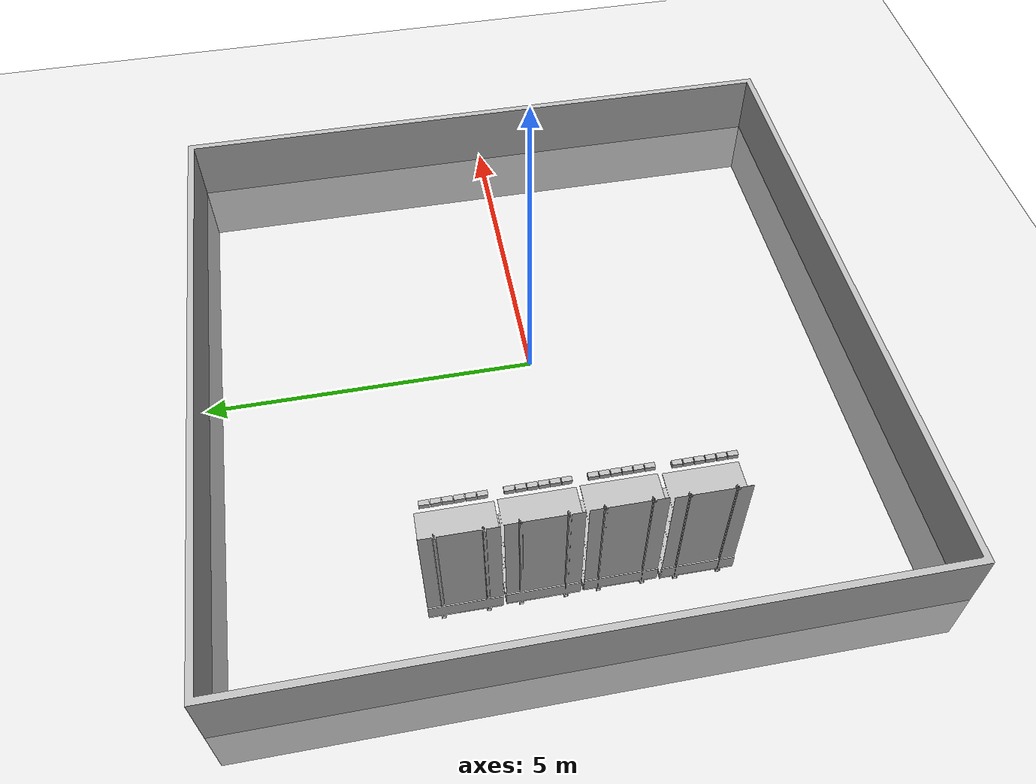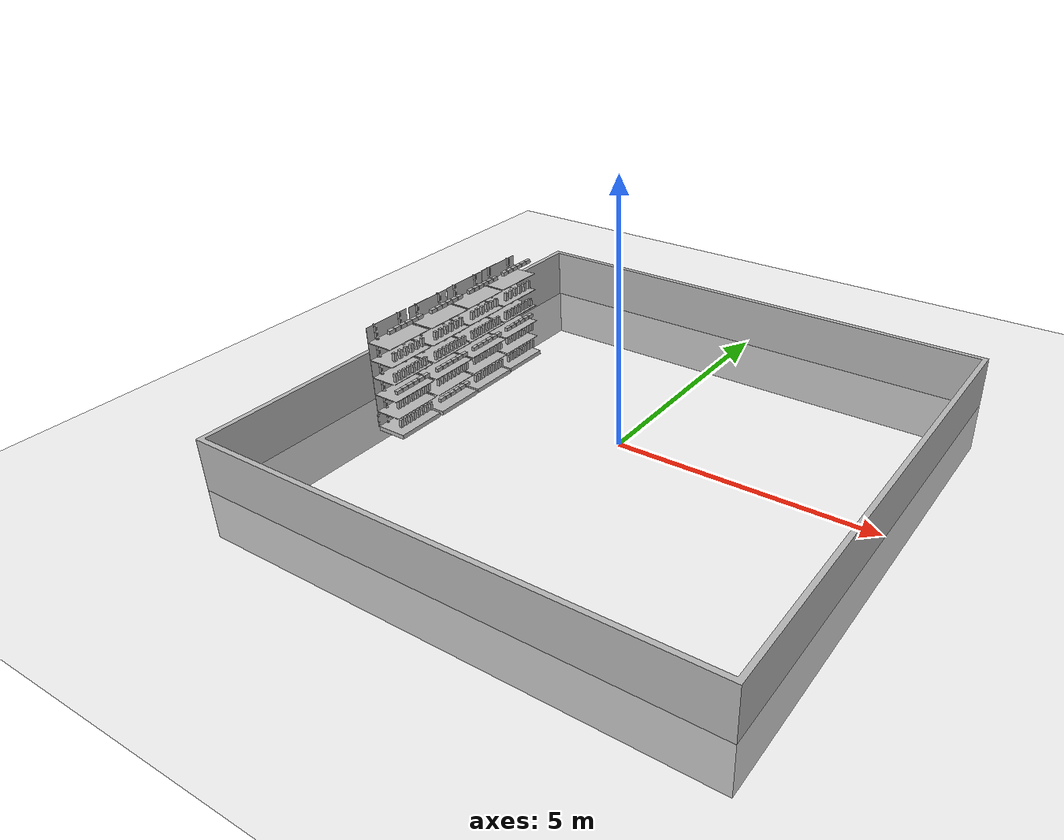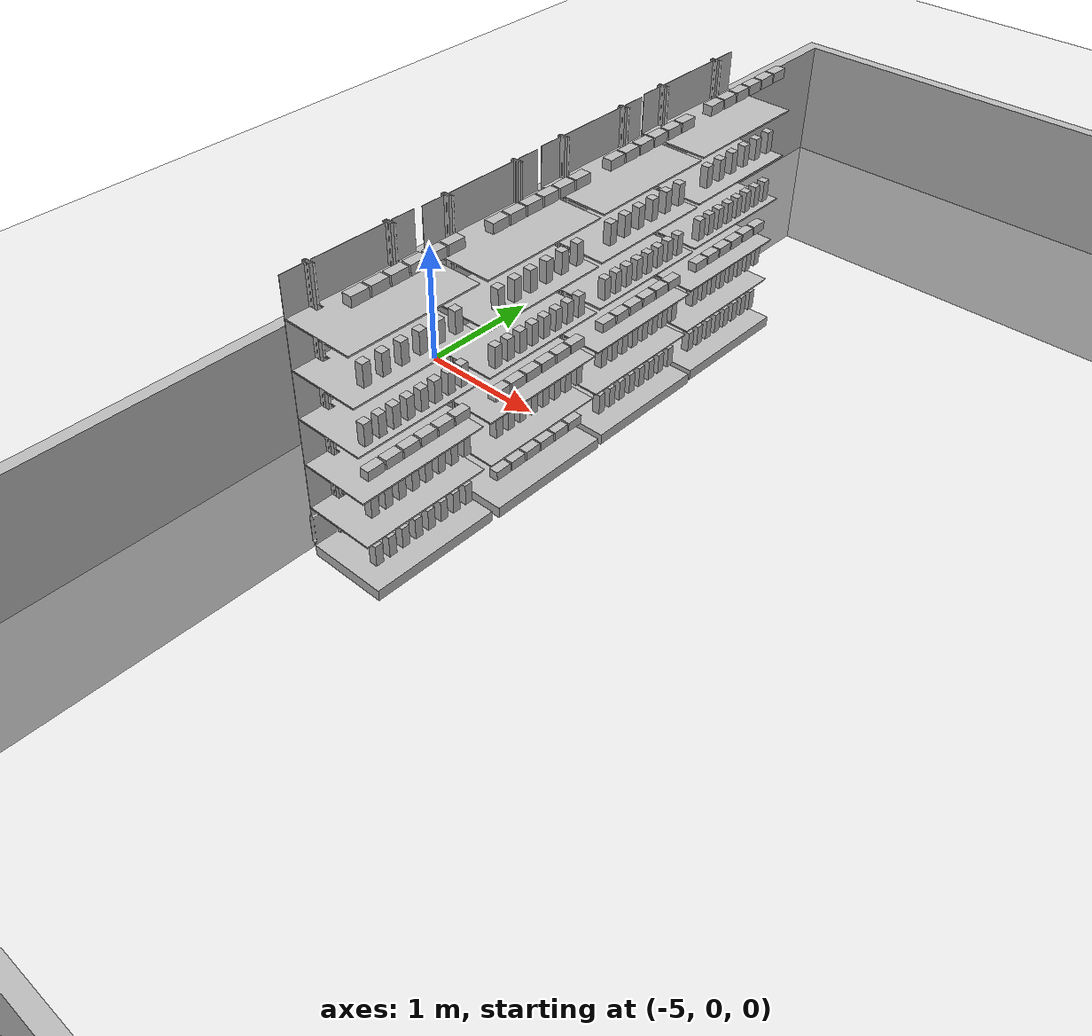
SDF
<sdf version="1.7">
 <world name="default">
  <light name="sun" type="directional">
   <pose>0 0 10 0 -0 0</pose>
   <diffuse>0.8 0.8 0.8 1</diffuse>
   <specular>0.2 0.2 0.2 1</specular>
   <attenuation>
    <range>1000</range>
    <constant>0.9</constant>
    <linear>0.01</linear>
    <quadratic>0.001</quadratic>
   </attenuation>
   <direction>-0.5 0.1 -0.9</direction>
   <spot><inner_angle>0</inner_angle><outer_angle>0</outer_angle><falloff>0</falloff></spot>
  </light>
  <model name="ground_plane">
   <static>1</static>
   <link name="link">
    <collision name="collision">
     <geometry><plane><normal>0 0 1</normal><size>100 100</size></plane></geometry>
     <surface>
      <contact><collide_bitmask>65535</collide_bitmask></contact>
      <friction><ode><mu>100</mu><mu2>50</mu2></ode></friction>
     </surface>
    </collision>
    <visual name="visual">
     <cast_shadows>0</cast_shadows>
     <geometry><plane><normal>0 0 1</normal><size>100 100</size></plane></geometry>
     <material>
      <script><uri>file://media/materials/scripts/gazebo.material</uri><name>Gazebo/Grey</name></script>
     </material>
    </visual>
   </link>
  </model>
  <gravity>0 0 -9.8</gravity>
  <magnetic_field>6e-06 2.3e-05 -4.2e-05</magnetic_field>
  <atmosphere type="adiabatic"/>
  <physics name="default_physics" default="0" type="ode">
   <max_step_size>0.001</max_step_size>
   <real_time_factor>1</real_time_factor>
   <real_time_update_rate>1000</real_time_update_rate>
   <ode>
    <solver><thread_position_correction>1</thread_position_correction><island_threads>8</island_threads></solver>
   </ode>
  </physics>
  <scene><ambient>0.4 0.4 0.4 1</ambient><background>0.7 0.7 0.7 1</background><shadows>1</shadows></scene>
  <audio><device>default</device></audio>
  <spherical_coordinates>
   <surface_model>EARTH_WGS84</surface_model>
   <latitude_deg>0</latitude_deg>
   <longitude_deg>0</longitude_deg>
   <elevation>0</elevation>
   <heading_deg>0</heading_deg>
  </spherical_coordinates>
  <model name="room_square">
   <link name="link_0">
    <inertial>
     <mass>1</mass>
     <inertia>
      <ixx>0.166667</ixx>
      <ixy>0</ixy>
      <ixz>0</ixz>
      <iyy>0.166667</iyy>
      <iyz>0</iyz>
      <izz>0.166667</izz>
     </inertia>
    </inertial>
    <visual name="visual">
     <geometry><mesh><uri>model://0-blender/room_square.dae</uri><scale>1 1 1</scale></mesh></geometry>
    </visual>
    <collision name="collision">
     <geometry><mesh><uri>model://0-blender/room_square.dae</uri><scale>1 1 1</scale></mesh></geometry>
     <surface>
      <friction>
       <ode><mu>1</mu><mu2>1</mu2><fdir1>0 0 0</fdir1><slip1>0</slip1><slip2>0</slip2></ode>
       <torsional>
        <coefficient>1</coefficient>
        <patch_radius>0</patch_radius>
        <surface_radius>0</surface_radius>
        <use_patch_radius>1</use_patch_radius>
        <ode><slip>0</slip></ode>
       </torsional>
      </friction>
      <bounce><restitution_coefficient>0</restitution_coefficient><threshold>1e+06</threshold></bounce>
      <contact>
       <collide_without_contact>0</collide_without_contact>
       <collide_without_contact_bitmask>1</collide_without_contact_bitmask>
       <collide_bitmask>1</collide_bitmask>
       <ode>
        <soft_cfm>0</soft_cfm>
        <soft_erp>0.2</soft_erp>
        <kp>1e+13</kp>
        <kd>1</kd>
        <max_vel>0.01</max_vel>
        <min_depth>0</min_depth>
       </ode>
       <bullet>
        <split_impulse>1</split_impulse>
        <split_impulse_penetration_threshold>-0.01</split_impulse_penetration_threshold>
        <soft_cfm>0</soft_cfm>
        <soft_erp>0.2</soft_erp>
        <kp>1e+13</kp>
        <kd>1</kd>
       </bullet>
      </contact>
     </surface>
    </collision>
   </link>
   <static>1</static>
  </model>
  <model name="AH_shelf_filled_april">
   <static>1</static>
   <link name="link">
    <inertial>
     <mass>1</mass>
     <inertia><ixx>1</ixx><ixy>0</ixy><ixz>0</ixz><iyy>1</iyy><iyz>0</iyz><izz>1</izz></inertia>
    </inertial>
    <visual name="visual">
     <geometry><mesh><uri>model://AH_shelf/AH_shelf.dae</uri><scale>1 1 1</scale></mesh></geometry>
    </visual>
    <collision name="collision">
     <geometry><mesh><uri>model://AH_shelf/AH_shelf.dae</uri><scale>1 1 1</scale></mesh></geometry>
     <surface>
      <friction>
       <ode><mu>1</mu><mu2>1</mu2><fdir1>0 0 0</fdir1><slip1>0</slip1><slip2>0</slip2></ode>
       <torsional>
        <coefficient>1</coefficient>
        <patch_radius>0</patch_radius>
        <surface_radius>0</surface_radius>
        <use_patch_radius>1</use_patch_radius>
        <ode><slip>0</slip></ode>
       </torsional>
      </friction>
      <bounce><restitution_coefficient>0</restitution_coefficient><threshold>1e+06</threshold></bounce>
      <contact>
       <collide_without_contact>0</collide_without_contact>
       <collide_without_contact_bitmask>1</collide_without_contact_bitmask>
       <collide_bitmask>1</collide_bitmask>
       <ode>
        <soft_cfm>0</soft_cfm>
        <soft_erp>0.2</soft_erp>
        <kp>1e+13</kp>
        <kd>1</kd>
        <max_vel>0.01</max_vel>
        <min_depth>0</min_depth>
       </ode>
       <bullet>
        <split_impulse>1</split_impulse>
        <split_impulse_penetration_threshold>-0.01</split_impulse_penetration_threshold>
        <soft_cfm>0</soft_cfm>
        <soft_erp>0.2</soft_erp>
        <kp>1e+13</kp>
        <kd>1</kd>
       </bullet>
      </contact>
     </surface>
    </collision>
   </link>
   <model name="board0">
    <pose>0 0.5 2.1 0 -0 0</pose>
    <static>0</static>
    <link name="AH_thee_mango_tag36_11_00030::link_0">
     <inertial>
      <mass>0.1</mass>
      <inertia><ixx>0.0014</ixx><ixy>0</ixy><ixz>0</ixz><iyy>0.0014</iyy><iyz>0</iyz><izz>0.0028</izz></inertia>
     </inertial>
     <pose>0.142857 0 0 0 -0 1.57</pose>
     <visual name="visual">
      <geometry>
       <mesh>
        <uri>model://AH_thee_mango/AH_thee_mango_tag36_11_00030/AH_thee_mango_tag36_11_00030.dae</uri>
        <scale>1 1 1</scale>
       </mesh>
      </geometry>
     </visual>
     <collision name="collision">
      <geometry>
       <mesh>
        <uri>model://AH_thee_mango/AH_thee_mango_tag36_11_00030/AH_thee_mango_tag36_11_00030.dae</uri>
        <scale>1 1 1</scale>
       </mesh>
      </geometry>
      <surface>
       <friction>
        <ode><mu>1</mu><mu2>1</mu2><fdir1>0 0 0</fdir1><slip1>0</slip1><slip2>0</slip2></ode>
        <torsional>
         <coefficient>1</coefficient>
         <patch_radius>0</patch_radius>
         <surface_radius>0</surface_radius>
         <use_patch_radius>1</use_patch_radius>
         <ode><slip>0</slip></ode>
        </torsional>
       </friction>
       <bounce><restitution_coefficient>0</restitution_coefficient><threshold>1e+06</threshold></bounce>
       <contact>
        <collide_without_contact>0</collide_without_contact>
        <collide_without_contact_bitmask>1</collide_without_contact_bitmask>
        <collide_bitmask>1</collide_bitmask>
        <ode>
         <soft_cfm>0</soft_cfm>
         <soft_erp>0.2</soft_erp>
         <kp>1e+13</kp>
         <kd>1</kd>
         <max_vel>0.01</max_vel>
         <min_depth>0</min_depth>
        </ode>
        <bullet>
         <split_impulse>1</split_impulse>
         <split_impulse_penetration_threshold>-0.01</split_impulse_penetration_threshold>
         <soft_cfm>0</soft_cfm>
         <soft_erp>0.2</soft_erp>
         <kp>1e+13</kp>
         <kd>1</kd>
        </bullet>
       </contact>
      </surface>
     </collision>
    </link>
    <static>0</static>
    <link name="AH_thee_mango_tag36_11_00031::link_0">
     <inertial>
      <mass>0.1</mass>
      <inertia><ixx>0.0014</ixx><ixy>0</ixy><ixz>0</ixz><iyy>0.0014</iyy><iyz>0</iyz><izz>0.0028</izz></inertia>
     </inertial>
     <pose>0.285714 0 0 0 -0 1.57</pose>
     <visual name="visual">
      <geometry>
       <mesh>
        <uri>model://AH_thee_mango/AH_thee_mango_tag36_11_00031/AH_thee_mango_tag36_11_00031.dae</uri>
        <scale>1 1 1</scale>
       </mesh>
      </geometry>
     </visual>
     <collision name="collision">
      <geometry>
       <mesh>
        <uri>model://AH_thee_mango/AH_thee_mango_tag36_11_00031/AH_thee_mango_tag36_11_00031.dae</uri>
        <scale>1 1 1</scale>
       </mesh>
      </geometry>
      <surface>
       <friction>
        <ode><mu>1</mu><mu2>1</mu2><fdir1>0 0 0</fdir1><slip1>0</slip1><slip2>0</slip2></ode>
        <torsional>
         <coefficient>1</coefficient>
         <patch_radius>0</patch_radius>
         <surface_radius>0</surface_radius>
         <use_patch_radius>1</use_patch_radius>
         <ode><slip>0</slip></ode>
        </torsional>
       </friction>
       <bounce><restitution_coefficient>0</restitution_coefficient><threshold>1e+06</threshold></bounce>
       <contact>
        <collide_without_contact>0</collide_without_contact>
        <collide_without_contact_bitmask>1</collide_without_contact_bitmask>
        <collide_bitmask>1</collide_bitmask>
        <ode>
         <soft_cfm>0</soft_cfm>
         <soft_erp>0.2</soft_erp>
         <kp>1e+13</kp>
         <kd>1</kd>
         <max_vel>0.01</max_vel>
         <min_depth>0</min_depth>
        </ode>
        <bullet>
         <split_impulse>1</split_impulse>
         <split_impulse_penetration_threshold>-0.01</split_impulse_penetration_threshold>
         <soft_cfm>0</soft_cfm>
         <soft_erp>0.2</soft_erp>
         <kp>1e+13</kp>
         <kd>1</kd>
        </bullet>
       </contact>
      </surface>
     </collision>
    </link>
    <static>0</static>
    <link name="AH_thee_mango_tag36_11_00032::link_0">
     <inertial>
      <mass>0.1</mass>
      <inertia><ixx>0.0014</ixx><ixy>0</ixy><ixz>0</ixz><iyy>0.0014</iyy><iyz>0</iyz><izz>0.0028</izz></inertia>
     </inertial>
     <pose>0.428571 0 0 0 -0 1.57</pose>
     <visual name="visual">
      <geometry>
       <mesh>
        <uri>model://AH_thee_mango/AH_thee_mango_tag36_11_00032/AH_thee_mango_tag36_11_00032.dae</uri>
        <scale>1 1 1</scale>
       </mesh>
      </geometry>
     </visual>
     <collision name="collision">
      <geometry>
       <mesh>
        <uri>model://AH_thee_mango/AH_thee_mango_tag36_11_00032/AH_thee_mango_tag36_11_00032.dae</uri>
        <scale>1 1 1</scale>
       </mesh>
      </geometry>
      <surface>
       <friction>
        <ode><mu>1</mu><mu2>1</mu2><fdir1>0 0 0</fdir1><slip1>0</slip1><slip2>0</slip2></ode>
        <torsional>
         <coefficient>1</coefficient>
         <patch_radius>0</patch_radius>
         <surface_radius>0</surface_radius>
         <use_patch_radius>1</use_patch_radius>
         <ode><slip>0</slip></ode>
        </torsional>
       </friction>
       <bounce><restitution_coefficient>0</restitution_coefficient><threshold>1e+06</threshold></bounce>
       <contact>
        <collide_without_contact>0</collide_without_contact>
        <collide_without_contact_bitmask>1</collide_without_contact_bitmask>
        <collide_bitmask>1</collide_bitmask>
        <ode>
         <soft_cfm>0</soft_cfm>
         <soft_erp>0.2</soft_erp>
         <kp>1e+13</kp>
         <kd>1</kd>
         <max_vel>0.01</max_vel>
         <min_depth>0</min_depth>
        </ode>
        <bullet>
         <split_impulse>1</split_impulse>
         <split_impulse_penetration_threshold>-0.01</split_impulse_penetration_threshold>
         <soft_cfm>0</soft_cfm>
         <soft_erp>0.2</soft_erp>
         <kp>1e+13</kp>
         <kd>1</kd>
        </bullet>
       </contact>
      </surface>
     </collision>
    </link>
    <static>0</static>
    <link name="AH_thee_mango_tag36_11_00033::link_0">
     <inertial>
      <mass>0.1</mass>
      <inertia><ixx>0.0014</ixx><ixy>0</ixy><ixz>0</ixz><iyy>0.0014</iyy><iyz>0</iyz><izz>0.0028</izz></inertia>
     </inertial>
     <pose>0.571429 0 0 0 -0 1.57</pose>
     <visual name="visual">
      <geometry>
       <mesh>
        <uri>model://AH_thee_mango/AH_thee_mango_tag36_11_00033/AH_thee_mango_tag36_11_00033.dae</uri>
        <scale>1 1 1</scale>
       </mesh>
      </geometry>
     </visual>
     <collision name="collision">
      <geometry>
       <mesh>
        <uri>model://AH_thee_mango/AH_thee_mango_tag36_11_00033/AH_thee_mango_tag36_11_00033.dae</uri>
        <scale>1 1 1</scale>
       </mesh>
      </geometry>
      <surface>
       <friction>
        <ode><mu>1</mu><mu2>1</mu2><fdir1>0 0 0</fdir1><slip1>0</slip1><slip2>0</slip2></ode>
        <torsional>
         <coefficient>1</coefficient>
         <patch_radius>0</patch_radius>
         <surface_radius>0</surface_radius>
         <use_patch_radius>1</use_patch_radius>
         <ode><slip>0</slip></ode>
        </torsional>
       </friction>
       <bounce><restitution_coefficient>0</restitution_coefficient><threshold>1e+06</threshold></bounce>
       <contact>
        <collide_without_contact>0</collide_without_contact>
        <collide_without_contact_bitmask>1</collide_without_contact_bitmask>
        <collide_bitmask>1</collide_bitmask>
        <ode>
         <soft_cfm>0</soft_cfm>
         <soft_erp>0.2</soft_erp>
         <kp>1e+13</kp>
         <kd>1</kd>
         <max_vel>0.01</max_vel>
         <min_depth>0</min_depth>
        </ode>
        <bullet>
         <split_impulse>1</split_impulse>
         <split_impulse_penetration_threshold>-0.01</split_impulse_penetration_threshold>
         <soft_cfm>0</soft_cfm>
         <soft_erp>0.2</soft_erp>
         <kp>1e+13</kp>
         <kd>1</kd>
        </bullet>
       </contact>
      </surface>
     </collision>
    </link>
    <static>0</static>
    <link name="AH_thee_mango_tag36_11_00034::link_0">
     <inertial>
      <mass>0.1</mass>
      <inertia><ixx>0.0014</ixx><ixy>0</ixy><ixz>0</ixz><iyy>0.0014</iyy><iyz>0</iyz><izz>0.0028</izz></inertia>
     </inertial>
     <pose>0.714286 0 0 0 -0 1.57</pose>
     <visual name="visual">
      <geometry>
       <mesh>
        <uri>model://AH_thee_mango/AH_thee_mango_tag36_11_00034/AH_thee_mango_tag36_11_00034.dae</uri>
        <scale>1 1 1</scale>
       </mesh>
      </geometry>
     </visual>
     <collision name="collision">
      <geometry>
       <mesh>
        <uri>model://AH_thee_mango/AH_thee_mango_tag36_11_00034/AH_thee_mango_tag36_11_00034.dae</uri>
        <scale>1 1 1</scale>
       </mesh>
      </geometry>
      <surface>
       <friction>
        <ode><mu>1</mu><mu2>1</mu2><fdir1>0 0 0</fdir1><slip1>0</slip1><slip2>0</slip2></ode>
        <torsional>
         <coefficient>1</coefficient>
         <patch_radius>0</patch_radius>
         <surface_radius>0</surface_radius>
         <use_patch_radius>1</use_patch_radius>
         <ode><slip>0</slip></ode>
        </torsional>
       </friction>
       <bounce><restitution_coefficient>0</restitution_coefficient><threshold>1e+06</threshold></bounce>
       <contact>
        <collide_without_contact>0</collide_without_contact>
        <collide_without_contact_bitmask>1</collide_without_contact_bitmask>
        <collide_bitmask>1</collide_bitmask>
        <ode>
         <soft_cfm>0</soft_cfm>
         <soft_erp>0.2</soft_erp>
         <kp>1e+13</kp>
         <kd>1</kd>
         <max_vel>0.01</max_vel>
         <min_depth>0</min_depth>
        </ode>
        <bullet>
         <split_impulse>1</split_impulse>
         <split_impulse_penetration_threshold>-0.01</split_impulse_penetration_threshold>
         <soft_cfm>0</soft_cfm>
         <soft_erp>0.2</soft_erp>
         <kp>1e+13</kp>
         <kd>1</kd>
        </bullet>
       </contact>
      </surface>
     </collision>
    </link>
    <static>0</static>
    <link name="AH_thee_mango_tag36_11_00035::link_0">
     <inertial>
      <mass>0.1</mass>
      <inertia><ixx>0.0014</ixx><ixy>0</ixy><ixz>0</ixz><iyy>0.0014</iyy><iyz>0</iyz><izz>0.0028</izz></inertia>
     </inertial>
     <pose>0.857143 0 0 0 -0 1.57</pose>
     <visual name="visual">
      <geometry>
       <mesh>
        <uri>model://AH_thee_mango/AH_thee_mango_tag36_11_00035/AH_thee_mango_tag36_11_00035.dae</uri>
        <scale>1 1 1</scale>
       </mesh>
      </geometry>
     </visual>
     <collision name="collision">
      <geometry>
       <mesh>
        <uri>model://AH_thee_mango/AH_thee_mango_tag36_11_00035/AH_thee_mango_tag36_11_00035.dae</uri>
        <scale>1 1 1</scale>
       </mesh>
      </geometry>
      <surface>
       <friction>
        <ode><mu>1</mu><mu2>1</mu2><fdir1>0 0 0</fdir1><slip1>0</slip1><slip2>0</slip2></ode>
        <torsional>
         <coefficient>1</coefficient>
         <patch_radius>0</patch_radius>
         <surface_radius>0</surface_radius>
         <use_patch_radius>1</use_patch_radius>
         <ode><slip>0</slip></ode>
        </torsional>
       </friction>
       <bounce><restitution_coefficient>0</restitution_coefficient><threshold>1e+06</threshold></bounce>
       <contact>
        <collide_without_contact>0</collide_without_contact>
        <collide_without_contact_bitmask>1</collide_without_contact_bitmask>
        <collide_bitmask>1</collide_bitmask>
        <ode>
         <soft_cfm>0</soft_cfm>
         <soft_erp>0.2</soft_erp>
         <kp>1e+13</kp>
         <kd>1</kd>
         <max_vel>0.01</max_vel>
         <min_depth>0</min_depth>
        </ode>
        <bullet>
         <split_impulse>1</split_impulse>
         <split_impulse_penetration_threshold>-0.01</split_impulse_penetration_threshold>
         <soft_cfm>0</soft_cfm>
         <soft_erp>0.2</soft_erp>
         <kp>1e+13</kp>
         <kd>1</kd>
        </bullet>
       </contact>
      </surface>
     </collision>
    </link>
   </model>
   <model name="board1">
    <pose>0 0.5 1.6 0 -0 0</pose>
    <static>0</static>
    <link name="AH_hagelslag_melk_tag36_11_00000::link_0">
     <inertial>
      <mass>0.1</mass>
      <inertia><ixx>0.0014</ixx><ixy>0</ixy><ixz>0</ixz><iyy>0.0014</iyy><iyz>0</iyz><izz>0.0028</izz></inertia>
     </inertial>
     <pose>0.142857 0 0 0 -0 1.57</pose>
     <visual name="visual">
      <geometry>
       <mesh>
        <uri>model://AH_hagelslag_melk/AH_hagelslag_melk_tag36_11_00000/AH_hagelslag_melk_tag36_11_00000.dae</uri>
        <scale>1 1 1</scale>
       </mesh>
      </geometry>
     </visual>
     <collision name="collision">
      <geometry>
       <mesh>
        <uri>model://AH_hagelslag_melk/AH_hagelslag_melk_tag36_11_00000/AH_hagelslag_melk_tag36_11_00000.dae</uri>
        <scale>1 1 1</scale>
       </mesh>
      </geometry>
      <surface>
       <friction>
        <ode><mu>1</mu><mu2>1</mu2><fdir1>0 0 0</fdir1><slip1>0</slip1><slip2>0</slip2></ode>
        <torsional>
         <coefficient>1</coefficient>
         <patch_radius>0</patch_radius>
         <surface_radius>0</surface_radius>
         <use_patch_radius>1</use_patch_radius>
         <ode><slip>0</slip></ode>
        </torsional>
       </friction>
       <bounce><restitution_coefficient>0</restitution_coefficient><threshold>1e+06</threshold></bounce>
       <contact>
        <collide_without_contact>0</collide_without_contact>
        <collide_without_contact_bitmask>1</collide_without_contact_bitmask>
        <collide_bitmask>1</collide_bitmask>
        <ode>
         <soft_cfm>0</soft_cfm>
         <soft_erp>0.2</soft_erp>
         <kp>1e+13</kp>
         <kd>1</kd>
         <max_vel>0.01</max_vel>
         <min_depth>0</min_depth>
        </ode>
        <bullet>
         <split_impulse>1</split_impulse>
         <split_impulse_penetration_threshold>-0.01</split_impulse_penetration_threshold>
         <soft_cfm>0</soft_cfm>
         <soft_erp>0.2</soft_erp>
         <kp>1e+13</kp>
         <kd>1</kd>
        </bullet>
       </contact>
      </surface>
     </collision>
    </link>
    <static>0</static>
    <link name="AH_hagelslag_melk_tag36_11_00001::link_0">
     <inertial>
      <mass>0.1</mass>
      <inertia><ixx>0.0014</ixx><ixy>0</ixy><ixz>0</ixz><iyy>0.0014</iyy><iyz>0</iyz><izz>0.0028</izz></inertia>
     </inertial>
     <pose>0.285714 0 0 0 -0 1.57</pose>
     <visual name="visual">
      <geometry>
       <mesh>
        <uri>model://AH_hagelslag_melk/AH_hagelslag_melk_tag36_11_00001/AH_hagelslag_melk_tag36_11_00001.dae</uri>
        <scale>1 1 1</scale>
       </mesh>
      </geometry>
     </visual>
     <collision name="collision">
      <geometry>
       <mesh>
        <uri>model://AH_hagelslag_melk/AH_hagelslag_melk_tag36_11_00001/AH_hagelslag_melk_tag36_11_00001.dae</uri>
        <scale>1 1 1</scale>
       </mesh>
      </geometry>
      <surface>
       <friction>
        <ode><mu>1</mu><mu2>1</mu2><fdir1>0 0 0</fdir1><slip1>0</slip1><slip2>0</slip2></ode>
        <torsional>
         <coefficient>1</coefficient>
         <patch_radius>0</patch_radius>
         <surface_radius>0</surface_radius>
         <use_patch_radius>1</use_patch_radius>
         <ode><slip>0</slip></ode>
        </torsional>
       </friction>
       <bounce><restitution_coefficient>0</restitution_coefficient><threshold>1e+06</threshold></bounce>
       <contact>
        <collide_without_contact>0</collide_without_contact>
        <collide_without_contact_bitmask>1</collide_without_contact_bitmask>
        <collide_bitmask>1</collide_bitmask>
        <ode>
         <soft_cfm>0</soft_cfm>
         <soft_erp>0.2</soft_erp>
         <kp>1e+13</kp>
         <kd>1</kd>
         <max_vel>0.01</max_vel>
         <min_depth>0</min_depth>
        </ode>
        <bullet>
         <split_impulse>1</split_impulse>
         <split_impulse_penetration_threshold>-0.01</split_impulse_penetration_threshold>
         <soft_cfm>0</soft_cfm>
         <soft_erp>0.2</soft_erp>
         <kp>1e+13</kp>
         <kd>1</kd>
        </bullet>
       </contact>
      </surface>
     </collision>
    </link>
    <static>0</static>
    <link name="AH_hagelslag_melk_tag36_11_00002::link_0">
     <inertial>
      <mass>0.1</mass>
      <inertia><ixx>0.0014</ixx><ixy>0</ixy><ixz>0</ixz><iyy>0.0014</iyy><iyz>0</iyz><izz>0.0028</izz></inertia>
     </inertial>
     <pose>0.428571 0 0 0 -0 1.57</pose>
     <visual name="visual">
      <geometry>
       <mesh>
        <uri>model://AH_hagelslag_melk/AH_hagelslag_melk_tag36_11_00002/AH_hagelslag_melk_tag36_11_00002.dae</uri>
        <scale>1 1 1</scale>
       </mesh>
      </geometry>
     </visual>
     <collision name="collision">
      <geometry>
       <mesh>
        <uri>model://AH_hagelslag_melk/AH_hagelslag_melk_tag36_11_00002/AH_hagelslag_melk_tag36_11_00002.dae</uri>
        <scale>1 1 1</scale>
       </mesh>
      </geometry>
      <surface>
       <friction>
        <ode><mu>1</mu><mu2>1</mu2><fdir1>0 0 0</fdir1><slip1>0</slip1><slip2>0</slip2></ode>
        <torsional>
         <coefficient>1</coefficient>
         <patch_radius>0</patch_radius>
         <surface_radius>0</surface_radius>
         <use_patch_radius>1</use_patch_radius>
         <ode><slip>0</slip></ode>
        </torsional>
       </friction>
       <bounce><restitution_coefficient>0</restitution_coefficient><threshold>1e+06</threshold></bounce>
       <contact>
        <collide_without_contact>0</collide_without_contact>
        <collide_without_contact_bitmask>1</collide_without_contact_bitmask>
        <collide_bitmask>1</collide_bitmask>
        <ode>
         <soft_cfm>0</soft_cfm>
         <soft_erp>0.2</soft_erp>
         <kp>1e+13</kp>
         <kd>1</kd>
         <max_vel>0.01</max_vel>
         <min_depth>0</min_depth>
        </ode>
        <bullet>
         <split_impulse>1</split_impulse>
         <split_impulse_penetration_threshold>-0.01</split_impulse_penetration_threshold>
         <soft_cfm>0</soft_cfm>
         <soft_erp>0.2</soft_erp>
         <kp>1e+13</kp>
         <kd>1</kd>
        </bullet>
       </contact>
      </surface>
     </collision>
    </link>
    <static>0</static>
    <link name="AH_hagelslag_melk_tag36_11_00003::link_0">
     <inertial>
      <mass>0.1</mass>
      <inertia><ixx>0.0014</ixx><ixy>0</ixy><ixz>0</ixz><iyy>0.0014</iyy><iyz>0</iyz><izz>0.0028</izz></inertia>
     </inertial>
     <pose>0.571429 0 0 0 -0 1.57</pose>
     <visual name="visual">
      <geometry>
       <mesh>
        <uri>model://AH_hagelslag_melk/AH_hagelslag_melk_tag36_11_00003/AH_hagelslag_melk_tag36_11_00003.dae</uri>
        <scale>1 1 1</scale>
       </mesh>
      </geometry>
     </visual>
     <collision name="collision">
      <geometry>
       <mesh>
        <uri>model://AH_hagelslag_melk/AH_hagelslag_melk_tag36_11_00003/AH_hagelslag_melk_tag36_11_00003.dae</uri>
        <scale>1 1 1</scale>
       </mesh>
      </geometry>
      <surface>
       <friction>
        <ode><mu>1</mu><mu2>1</mu2><fdir1>0 0 0</fdir1><slip1>0</slip1><slip2>0</slip2></ode>
        <torsional>
         <coefficient>1</coefficient>
         <patch_radius>0</patch_radius>
         <surface_radius>0</surface_radius>
         <use_patch_radius>1</use_patch_radius>
         <ode><slip>0</slip></ode>
        </torsional>
       </friction>
       <bounce><restitution_coefficient>0</restitution_coefficient><threshold>1e+06</threshold></bounce>
       <contact>
        <collide_without_contact>0</collide_without_contact>
        <collide_without_contact_bitmask>1</collide_without_contact_bitmask>
        <collide_bitmask>1</collide_bitmask>
        <ode>
         <soft_cfm>0</soft_cfm>
         <soft_erp>0.2</soft_erp>
         <kp>1e+13</kp>
         <kd>1</kd>
         <max_vel>0.01</max_vel>
         <min_depth>0</min_depth>
        </ode>
        <bullet>
         <split_impulse>1</split_impulse>
         <split_impulse_penetration_threshold>-0.01</split_impulse_penetration_threshold>
         <soft_cfm>0</soft_cfm>
         <soft_erp>0.2</soft_erp>
         <kp>1e+13</kp>
         <kd>1</kd>
        </bullet>
       </contact>
      </surface>
     </collision>
    </link>
    <static>0</static>
    <link name="AH_hagelslag_melk_tag36_11_00004::link_0">
     <inertial>
      <mass>0.1</mass>
      <inertia><ixx>0.0014</ixx><ixy>0</ixy><ixz>0</ixz><iyy>0.0014</iyy><iyz>0</iyz><izz>0.0028</izz></inertia>
     </inertial>
     <pose>0.714286 0 0 0 -0 1.57</pose>
     <visual name="visual">
      <geometry>
       <mesh>
        <uri>model://AH_hagelslag_melk/AH_hagelslag_melk_tag36_11_00004/AH_hagelslag_melk_tag36_11_00004.dae</uri>
        <scale>1 1 1</scale>
       </mesh>
      </geometry>
     </visual>
     <collision name="collision">
      <geometry>
       <mesh>
        <uri>model://AH_hagelslag_melk/AH_hagelslag_melk_tag36_11_00004/AH_hagelslag_melk_tag36_11_00004.dae</uri>
        <scale>1 1 1</scale>
       </mesh>
      </geometry>
      <surface>
       <friction>
        <ode><mu>1</mu><mu2>1</mu2><fdir1>0 0 0</fdir1><slip1>0</slip1><slip2>0</slip2></ode>
        <torsional>
         <coefficient>1</coefficient>
         <patch_radius>0</patch_radius>
         <surface_radius>0</surface_radius>
         <use_patch_radius>1</use_patch_radius>
         <ode><slip>0</slip></ode>
        </torsional>
       </friction>
       <bounce><restitution_coefficient>0</restitution_coefficient><threshold>1e+06</threshold></bounce>
       <contact>
        <collide_without_contact>0</collide_without_contact>
        <collide_without_contact_bitmask>1</collide_without_contact_bitmask>
        <collide_bitmask>1</collide_bitmask>
        <ode>
         <soft_cfm>0</soft_cfm>
         <soft_erp>0.2</soft_erp>
         <kp>1e+13</kp>
         <kd>1</kd>
         <max_vel>0.01</max_vel>
         <min_depth>0</min_depth>
        </ode>
        <bullet>
         <split_impulse>1</split_impulse>
         <split_impulse_penetration_threshold>-0.01</split_impulse_penetration_threshold>
         <soft_cfm>0</soft_cfm>
         <soft_erp>0.2</soft_erp>
         <kp>1e+13</kp>
         <kd>1</kd>
        </bullet>
       </contact>
      </surface>
     </collision>
    </link>
    <static>0</static>
    <link name="AH_hagelslag_melk_tag36_11_00005::link_0">
     <inertial>
      <mass>0.1</mass>
      <inertia><ixx>0.0014</ixx><ixy>0</ixy><ixz>0</ixz><iyy>0.0014</iyy><iyz>0</iyz><izz>0.0028</izz></inertia>
     </inertial>
     <pose>0.857143 0 0 0 -0 1.57</pose>
     <visual name="visual">
      <geometry>
       <mesh>
        <uri>model://AH_hagelslag_melk/AH_hagelslag_melk_tag36_11_00005/AH_hagelslag_melk_tag36_11_00005.dae</uri>
        <scale>1 1 1</scale>
       </mesh>
      </geometry>
     </visual>
     <collision name="collision">
      <geometry>
       <mesh>
        <uri>model://AH_hagelslag_melk/AH_hagelslag_melk_tag36_11_00005/AH_hagelslag_melk_tag36_11_00005.dae</uri>
        <scale>1 1 1</scale>
       </mesh>
      </geometry>
      <surface>
       <friction>
        <ode><mu>1</mu><mu2>1</mu2><fdir1>0 0 0</fdir1><slip1>0</slip1><slip2>0</slip2></ode>
        <torsional>
         <coefficient>1</coefficient>
         <patch_radius>0</patch_radius>
         <surface_radius>0</surface_radius>
         <use_patch_radius>1</use_patch_radius>
         <ode><slip>0</slip></ode>
        </torsional>
       </friction>
       <bounce><restitution_coefficient>0</restitution_coefficient><threshold>1e+06</threshold></bounce>
       <contact>
        <collide_without_contact>0</collide_without_contact>
        <collide_without_contact_bitmask>1</collide_without_contact_bitmask>
        <collide_bitmask>1</collide_bitmask>
        <ode>
         <soft_cfm>0</soft_cfm>
         <soft_erp>0.2</soft_erp>
         <kp>1e+13</kp>
         <kd>1</kd>
         <max_vel>0.01</max_vel>
         <min_depth>0</min_depth>
        </ode>
        <bullet>
         <split_impulse>1</split_impulse>
         <split_impulse_penetration_threshold>-0.01</split_impulse_penetration_threshold>
         <soft_cfm>0</soft_cfm>
         <soft_erp>0.2</soft_erp>
         <kp>1e+13</kp>
         <kd>1</kd>
        </bullet>
       </contact>
      </surface>
     </collision>
    </link>
   </model>
   <model name="board2">
    <pose>0 0.5 1.2 0 -0 0</pose>
    <static>0</static>
    <link name="AH_hagelslag_puur_tag36_11_00015::link_0">
     <inertial>
      <mass>0.1</mass>
      <inertia><ixx>0.0014</ixx><ixy>0</ixy><ixz>0</ixz><iyy>0.0014</iyy><iyz>0</iyz><izz>0.0028</izz></inertia>
     </inertial>
     <pose>0.111111 0 0 0 -0 1.57</pose>
     <visual name="visual">
      <geometry>
       <mesh>
        <uri>model://AH_hagelslag_puur/AH_hagelslag_puur_tag36_11_00015/AH_hagelslag_puur_tag36_11_00015.dae</uri>
        <scale>1 1 1</scale>
       </mesh>
      </geometry>
     </visual>
     <collision name="collision">
      <geometry>
       <mesh>
        <uri>model://AH_hagelslag_puur/AH_hagelslag_puur_tag36_11_00015/AH_hagelslag_puur_tag36_11_00015.dae</uri>
        <scale>1 1 1</scale>
       </mesh>
      </geometry>
      <surface>
       <friction>
        <ode><mu>1</mu><mu2>1</mu2><fdir1>0 0 0</fdir1><slip1>0</slip1><slip2>0</slip2></ode>
        <torsional>
         <coefficient>1</coefficient>
         <patch_radius>0</patch_radius>
         <surface_radius>0</surface_radius>
         <use_patch_radius>1</use_patch_radius>
         <ode><slip>0</slip></ode>
        </torsional>
       </friction>
       <bounce><restitution_coefficient>0</restitution_coefficient><threshold>1e+06</threshold></bounce>
       <contact>
        <collide_without_contact>0</collide_without_contact>
        <collide_without_contact_bitmask>1</collide_without_contact_bitmask>
        <collide_bitmask>1</collide_bitmask>
        <ode>
         <soft_cfm>0</soft_cfm>
         <soft_erp>0.2</soft_erp>
         <kp>1e+13</kp>
         <kd>1</kd>
         <max_vel>0.01</max_vel>
         <min_depth>0</min_depth>
        </ode>
        <bullet>
         <split_impulse>1</split_impulse>
         <split_impulse_penetration_threshold>-0.01</split_impulse_penetration_threshold>
         <soft_cfm>0</soft_cfm>
         <soft_erp>0.2</soft_erp>
         <kp>1e+13</kp>
         <kd>1</kd>
        </bullet>
       </contact>
      </surface>
     </collision>
    </link>
    <static>0</static>
    <link name="AH_hagelslag_puur_tag36_11_00016::link_0">
     <inertial>
      <mass>0.1</mass>
      <inertia><ixx>0.0014</ixx><ixy>0</ixy><ixz>0</ixz><iyy>0.0014</iyy><iyz>0</iyz><izz>0.0028</izz></inertia>
     </inertial>
     <pose>0.222222 0 0 0 -0 1.57</pose>
     <visual name="visual">
      <geometry>
       <mesh>
        <uri>model://AH_hagelslag_puur/AH_hagelslag_puur_tag36_11_00016/AH_hagelslag_puur_tag36_11_00016.dae</uri>
        <scale>1 1 1</scale>
       </mesh>
      </geometry>
     </visual>
     <collision name="collision">
      <geometry>
       <mesh>
        <uri>model://AH_hagelslag_puur/AH_hagelslag_puur_tag36_11_00016/AH_hagelslag_puur_tag36_11_00016.dae</uri>
        <scale>1 1 1</scale>
       </mesh>
      </geometry>
      <surface>
       <friction>
        <ode><mu>1</mu><mu2>1</mu2><fdir1>0 0 0</fdir1><slip1>0</slip1><slip2>0</slip2></ode>
        <torsional>
         <coefficient>1</coefficient>
         <patch_radius>0</patch_radius>
         <surface_radius>0</surface_radius>
         <use_patch_radius>1</use_patch_radius>
         <ode><slip>0</slip></ode>
        </torsional>
       </friction>
       <bounce><restitution_coefficient>0</restitution_coefficient><threshold>1e+06</threshold></bounce>
       <contact>
        <collide_without_contact>0</collide_without_contact>
        <collide_without_contact_bitmask>1</collide_without_contact_bitmask>
        <collide_bitmask>1</collide_bitmask>
        <ode>
         <soft_cfm>0</soft_cfm>
         <soft_erp>0.2</soft_erp>
         <kp>1e+13</kp>
         <kd>1</kd>
         <max_vel>0.01</max_vel>
         <min_depth>0</min_depth>
        </ode>
        <bullet>
         <split_impulse>1</split_impulse>
         <split_impulse_penetration_threshold>-0.01</split_impulse_penetration_threshold>
         <soft_cfm>0</soft_cfm>
         <soft_erp>0.2</soft_erp>
         <kp>1e+13</kp>
         <kd>1</kd>
        </bullet>
       </contact>
      </surface>
     </collision>
    </link>
    <static>0</static>
    <link name="AH_hagelslag_puur_tag36_11_00017::link_0">
     <inertial>
      <mass>0.1</mass>
      <inertia><ixx>0.0014</ixx><ixy>0</ixy><ixz>0</ixz><iyy>0.0014</iyy><iyz>0</iyz><izz>0.0028</izz></inertia>
     </inertial>
     <pose>0.333333 0 0 0 -0 1.57</pose>
     <visual name="visual">
      <geometry>
       <mesh>
        <uri>model://AH_hagelslag_puur/AH_hagelslag_puur_tag36_11_00017/AH_hagelslag_puur_tag36_11_00017.dae</uri>
        <scale>1 1 1</scale>
       </mesh>
      </geometry>
     </visual>
     <collision name="collision">
      <geometry>
       <mesh>
        <uri>model://AH_hagelslag_puur/AH_hagelslag_puur_tag36_11_00017/AH_hagelslag_puur_tag36_11_00017.dae</uri>
        <scale>1 1 1</scale>
       </mesh>
      </geometry>
      <surface>
       <friction>
        <ode><mu>1</mu><mu2>1</mu2><fdir1>0 0 0</fdir1><slip1>0</slip1><slip2>0</slip2></ode>
        <torsional>
         <coefficient>1</coefficient>
         <patch_radius>0</patch_radius>
         <surface_radius>0</surface_radius>
         <use_patch_radius>1</use_patch_radius>
         <ode><slip>0</slip></ode>
        </torsional>
       </friction>
       <bounce><restitution_coefficient>0</restitution_coefficient><threshold>1e+06</threshold></bounce>
       <contact>
        <collide_without_contact>0</collide_without_contact>
        <collide_without_contact_bitmask>1</collide_without_contact_bitmask>
        <collide_bitmask>1</collide_bitmask>
        <ode>
         <soft_cfm>0</soft_cfm>
         <soft_erp>0.2</soft_erp>
         <kp>1e+13</kp>
         <kd>1</kd>
         <max_vel>0.01</max_vel>
         <min_depth>0</min_depth>
        </ode>
        <bullet>
         <split_impulse>1</split_impulse>
         <split_impulse_penetration_threshold>-0.01</split_impulse_penetration_threshold>
         <soft_cfm>0</soft_cfm>
         <soft_erp>0.2</soft_erp>
         <kp>1e+13</kp>
         <kd>1</kd>
        </bullet>
       </contact>
      </surface>
     </collision>
    </link>
    <static>0</static>
    <link name="AH_hagelslag_puur_tag36_11_00018::link_0">
     <inertial>
      <mass>0.1</mass>
      <inertia><ixx>0.0014</ixx><ixy>0</ixy><ixz>0</ixz><iyy>0.0014</iyy><iyz>0</iyz><izz>0.0028</izz></inertia>
     </inertial>
     <pose>0.444444 0 0 0 -0 1.57</pose>
     <visual name="visual">
      <geometry>
       <mesh>
        <uri>model://AH_hagelslag_puur/AH_hagelslag_puur_tag36_11_00018/AH_hagelslag_puur_tag36_11_00018.dae</uri>
        <scale>1 1 1</scale>
       </mesh>
      </geometry>
     </visual>
     <collision name="collision">
      <geometry>
       <mesh>
        <uri>model://AH_hagelslag_puur/AH_hagelslag_puur_tag36_11_00018/AH_hagelslag_puur_tag36_11_00018.dae</uri>
        <scale>1 1 1</scale>
       </mesh>
      </geometry>
      <surface>
       <friction>
        <ode><mu>1</mu><mu2>1</mu2><fdir1>0 0 0</fdir1><slip1>0</slip1><slip2>0</slip2></ode>
        <torsional>
         <coefficient>1</coefficient>
         <patch_radius>0</patch_radius>
         <surface_radius>0</surface_radius>
         <use_patch_radius>1</use_patch_radius>
         <ode><slip>0</slip></ode>
        </torsional>
       </friction>
       <bounce><restitution_coefficient>0</restitution_coefficient><threshold>1e+06</threshold></bounce>
       <contact>
        <collide_without_contact>0</collide_without_contact>
        <collide_without_contact_bitmask>1</collide_without_contact_bitmask>
        <collide_bitmask>1</collide_bitmask>
        <ode>
         <soft_cfm>0</soft_cfm>
         <soft_erp>0.2</soft_erp>
         <kp>1e+13</kp>
         <kd>1</kd>
         <max_vel>0.01</max_vel>
         <min_depth>0</min_depth>
        </ode>
        <bullet>
         <split_impulse>1</split_impulse>
         <split_impulse_penetration_threshold>-0.01</split_impulse_penetration_threshold>
         <soft_cfm>0</soft_cfm>
         <soft_erp>0.2</soft_erp>
         <kp>1e+13</kp>
         <kd>1</kd>
        </bullet>
       </contact>
      </surface>
     </collision>
    </link>
    <static>0</static>
    <link name="AH_hagelslag_puur_tag36_11_00019::link_0">
     <inertial>
      <mass>0.1</mass>
      <inertia><ixx>0.0014</ixx><ixy>0</ixy><ixz>0</ixz><iyy>0.0014</iyy><iyz>0</iyz><izz>0.0028</izz></inertia>
     </inertial>
     <pose>0.555556 0 0 0 -0 1.57</pose>
     <visual name="visual">
      <geometry>
       <mesh>
        <uri>model://AH_hagelslag_puur/AH_hagelslag_puur_tag36_11_00019/AH_hagelslag_puur_tag36_11_00019.dae</uri>
        <scale>1 1 1</scale>
       </mesh>
      </geometry>
     </visual>
     <collision name="collision">
      <geometry>
       <mesh>
        <uri>model://AH_hagelslag_puur/AH_hagelslag_puur_tag36_11_00019/AH_hagelslag_puur_tag36_11_00019.dae</uri>
        <scale>1 1 1</scale>
       </mesh>
      </geometry>
      <surface>
       <friction>
        <ode><mu>1</mu><mu2>1</mu2><fdir1>0 0 0</fdir1><slip1>0</slip1><slip2>0</slip2></ode>
        <torsional>
         <coefficient>1</coefficient>
         <patch_radius>0</patch_radius>
         <surface_radius>0</surface_radius>
         <use_patch_radius>1</use_patch_radius>
         <ode><slip>0</slip></ode>
        </torsional>
       </friction>
       <bounce><restitution_coefficient>0</restitution_coefficient><threshold>1e+06</threshold></bounce>
       <contact>
        <collide_without_contact>0</collide_without_contact>
        <collide_without_contact_bitmask>1</collide_without_contact_bitmask>
        <collide_bitmask>1</collide_bitmask>
        <ode>
         <soft_cfm>0</soft_cfm>
         <soft_erp>0.2</soft_erp>
         <kp>1e+13</kp>
         <kd>1</kd>
         <max_vel>0.01</max_vel>
         <min_depth>0</min_depth>
        </ode>
        <bullet>
         <split_impulse>1</split_impulse>
         <split_impulse_penetration_threshold>-0.01</split_impulse_penetration_threshold>
         <soft_cfm>0</soft_cfm>
         <soft_erp>0.2</soft_erp>
         <kp>1e+13</kp>
         <kd>1</kd>
        </bullet>
       </contact>
      </surface>
     </collision>
    </link>
    <static>0</static>
    <link name="AH_hagelslag_puur_tag36_11_00020::link_0">
     <inertial>
      <mass>0.1</mass>
      <inertia><ixx>0.0014</ixx><ixy>0</ixy><ixz>0</ixz><iyy>0.0014</iyy><iyz>0</iyz><izz>0.0028</izz></inertia>
     </inertial>
     <pose>0.666667 0 0 0 -0 1.57</pose>
     <visual name="visual">
      <geometry>
       <mesh>
        <uri>model://AH_hagelslag_puur/AH_hagelslag_puur_tag36_11_00020/AH_hagelslag_puur_tag36_11_00020.dae</uri>
        <scale>1 1 1</scale>
       </mesh>
      </geometry>
     </visual>
     <collision name="collision">
      <geometry>
       <mesh>
        <uri>model://AH_hagelslag_puur/AH_hagelslag_puur_tag36_11_00020/AH_hagelslag_puur_tag36_11_00020.dae</uri>
        <scale>1 1 1</scale>
       </mesh>
      </geometry>
      <surface>
       <friction>
        <ode><mu>1</mu><mu2>1</mu2><fdir1>0 0 0</fdir1><slip1>0</slip1><slip2>0</slip2></ode>
        <torsional>
         <coefficient>1</coefficient>
         <patch_radius>0</patch_radius>
         <surface_radius>0</surface_radius>
         <use_patch_radius>1</use_patch_radius>
         <ode><slip>0</slip></ode>
        </torsional>
       </friction>
       <bounce><restitution_coefficient>0</restitution_coefficient><threshold>1e+06</threshold></bounce>
       <contact>
        <collide_without_contact>0</collide_without_contact>
        <collide_without_contact_bitmask>1</collide_without_contact_bitmask>
        <collide_bitmask>1</collide_bitmask>
        <ode>
         <soft_cfm>0</soft_cfm>
         <soft_erp>0.2</soft_erp>
         <kp>1e+13</kp>
         <kd>1</kd>
         <max_vel>0.01</max_vel>
         <min_depth>0</min_depth>
        </ode>
        <bullet>
         <split_impulse>1</split_impulse>
         <split_impulse_penetration_threshold>-0.01</split_impulse_penetration_threshold>
         <soft_cfm>0</soft_cfm>
         <soft_erp>0.2</soft_erp>
         <kp>1e+13</kp>
         <kd>1</kd>
        </bullet>
       </contact>
      </surface>
     </collision>
    </link>
    <static>0</static>
    <link name="AH_hagelslag_puur_tag36_11_00021::link_0">
     <inertial>
      <mass>0.1</mass>
      <inertia><ixx>0.0014</ixx><ixy>0</ixy><ixz>0</ixz><iyy>0.0014</iyy><iyz>0</iyz><izz>0.0028</izz></inertia>
     </inertial>
     <pose>0.777778 0 0 0 -0 1.57</pose>
     <visual name="visual">
      <geometry>
       <mesh>
        <uri>model://AH_hagelslag_puur/AH_hagelslag_puur_tag36_11_00021/AH_hagelslag_puur_tag36_11_00021.dae</uri>
        <scale>1 1 1</scale>
       </mesh>
      </geometry>
     </visual>
     <collision name="collision">
      <geometry>
       <mesh>
        <uri>model://AH_hagelslag_puur/AH_hagelslag_puur_tag36_11_00021/AH_hagelslag_puur_tag36_11_00021.dae</uri>
        <scale>1 1 1</scale>
       </mesh>
      </geometry>
      <surface>
       <friction>
        <ode><mu>1</mu><mu2>1</mu2><fdir1>0 0 0</fdir1><slip1>0</slip1><slip2>0</slip2></ode>
        <torsional>
         <coefficient>1</coefficient>
         <patch_radius>0</patch_radius>
         <surface_radius>0</surface_radius>
         <use_patch_radius>1</use_patch_radius>
         <ode><slip>0</slip></ode>
        </torsional>
       </friction>
       <bounce><restitution_coefficient>0</restitution_coefficient><threshold>1e+06</threshold></bounce>
       <contact>
        <collide_without_contact>0</collide_without_contact>
        <collide_without_contact_bitmask>1</collide_without_contact_bitmask>
        <collide_bitmask>1</collide_bitmask>
        <ode>
         <soft_cfm>0</soft_cfm>
         <soft_erp>0.2</soft_erp>
         <kp>1e+13</kp>
         <kd>1</kd>
         <max_vel>0.01</max_vel>
         <min_depth>0</min_depth>
        </ode>
        <bullet>
         <split_impulse>1</split_impulse>
         <split_impulse_penetration_threshold>-0.01</split_impulse_penetration_threshold>
         <soft_cfm>0</soft_cfm>
         <soft_erp>0.2</soft_erp>
         <kp>1e+13</kp>
         <kd>1</kd>
        </bullet>
       </contact>
      </surface>
     </collision>
    </link>
    <static>0</static>
    <link name="AH_hagelslag_puur_tag36_11_00022::link_0">
     <inertial>
      <mass>0.1</mass>
      <inertia><ixx>0.0014</ixx><ixy>0</ixy><ixz>0</ixz><iyy>0.0014</iyy><iyz>0</iyz><izz>0.0028</izz></inertia>
     </inertial>
     <pose>0.888889 0 0 0 -0 1.57</pose>
     <visual name="visual">
      <geometry>
       <mesh>
        <uri>model://AH_hagelslag_puur/AH_hagelslag_puur_tag36_11_00022/AH_hagelslag_puur_tag36_11_00022.dae</uri>
        <scale>1 1 1</scale>
       </mesh>
      </geometry>
     </visual>
     <collision name="collision">
      <geometry>
       <mesh>
        <uri>model://AH_hagelslag_puur/AH_hagelslag_puur_tag36_11_00022/AH_hagelslag_puur_tag36_11_00022.dae</uri>
        <scale>1 1 1</scale>
       </mesh>
      </geometry>
      <surface>
       <friction>
        <ode><mu>1</mu><mu2>1</mu2><fdir1>0 0 0</fdir1><slip1>0</slip1><slip2>0</slip2></ode>
        <torsional>
         <coefficient>1</coefficient>
         <patch_radius>0</patch_radius>
         <surface_radius>0</surface_radius>
         <use_patch_radius>1</use_patch_radius>
         <ode><slip>0</slip></ode>
        </torsional>
       </friction>
       <bounce><restitution_coefficient>0</restitution_coefficient><threshold>1e+06</threshold></bounce>
       <contact>
        <collide_without_contact>0</collide_without_contact>
        <collide_without_contact_bitmask>1</collide_without_contact_bitmask>
        <collide_bitmask>1</collide_bitmask>
        <ode>
         <soft_cfm>0</soft_cfm>
         <soft_erp>0.2</soft_erp>
         <kp>1e+13</kp>
         <kd>1</kd>
         <max_vel>0.01</max_vel>
         <min_depth>0</min_depth>
        </ode>
        <bullet>
         <split_impulse>1</split_impulse>
         <split_impulse_penetration_threshold>-0.01</split_impulse_penetration_threshold>
         <soft_cfm>0</soft_cfm>
         <soft_erp>0.2</soft_erp>
         <kp>1e+13</kp>
         <kd>1</kd>
        </bullet>
       </contact>
      </surface>
     </collision>
    </link>
   </model>
   <model name="board3">
    <pose>0 0.5 0.9 0 -0 0</pose>
    <static>0</static>
    <link name="AH_thee_mango_tag36_11_00030::link_0">
     <inertial>
      <mass>0.1</mass>
      <inertia><ixx>0.0014</ixx><ixy>0</ixy><ixz>0</ixz><iyy>0.0014</iyy><iyz>0</iyz><izz>0.0028</izz></inertia>
     </inertial>
     <pose>0.142857 0 0 0 -0 1.57</pose>
     <visual name="visual">
      <geometry>
       <mesh>
        <uri>model://AH_thee_mango/AH_thee_mango_tag36_11_00030/AH_thee_mango_tag36_11_00030.dae</uri>
        <scale>1 1 1</scale>
       </mesh>
      </geometry>
     </visual>
     <collision name="collision">
      <geometry>
       <mesh>
        <uri>model://AH_thee_mango/AH_thee_mango_tag36_11_00030/AH_thee_mango_tag36_11_00030.dae</uri>
        <scale>1 1 1</scale>
       </mesh>
      </geometry>
      <surface>
       <friction>
        <ode><mu>1</mu><mu2>1</mu2><fdir1>0 0 0</fdir1><slip1>0</slip1><slip2>0</slip2></ode>
        <torsional>
         <coefficient>1</coefficient>
         <patch_radius>0</patch_radius>
         <surface_radius>0</surface_radius>
         <use_patch_radius>1</use_patch_radius>
         <ode><slip>0</slip></ode>
        </torsional>
       </friction>
       <bounce><restitution_coefficient>0</restitution_coefficient><threshold>1e+06</threshold></bounce>
       <contact>
        <collide_without_contact>0</collide_without_contact>
        <collide_without_contact_bitmask>1</collide_without_contact_bitmask>
        <collide_bitmask>1</collide_bitmask>
        <ode>
         <soft_cfm>0</soft_cfm>
         <soft_erp>0.2</soft_erp>
         <kp>1e+13</kp>
         <kd>1</kd>
         <max_vel>0.01</max_vel>
         <min_depth>0</min_depth>
        </ode>
        <bullet>
         <split_impulse>1</split_impulse>
         <split_impulse_penetration_threshold>-0.01</split_impulse_penetration_threshold>
         <soft_cfm>0</soft_cfm>
         <soft_erp>0.2</soft_erp>
         <kp>1e+13</kp>
         <kd>1</kd>
        </bullet>
       </contact>
      </surface>
     </collision>
    </link>
    <static>0</static>
    <link name="AH_thee_mango_tag36_11_00031::link_0">
     <inertial>
      <mass>0.1</mass>
      <inertia><ixx>0.0014</ixx><ixy>0</ixy><ixz>0</ixz><iyy>0.0014</iyy><iyz>0</iyz><izz>0.0028</izz></inertia>
     </inertial>
     <pose>0.285714 0 0 0 -0 1.57</pose>
     <visual name="visual">
      <geometry>
       <mesh>
        <uri>model://AH_thee_mango/AH_thee_mango_tag36_11_00031/AH_thee_mango_tag36_11_00031.dae</uri>
        <scale>1 1 1</scale>
       </mesh>
      </geometry>
     </visual>
     <collision name="collision">
      <geometry>
       <mesh>
        <uri>model://AH_thee_mango/AH_thee_mango_tag36_11_00031/AH_thee_mango_tag36_11_00031.dae</uri>
        <scale>1 1 1</scale>
       </mesh>
      </geometry>
      <surface>
       <friction>
        <ode><mu>1</mu><mu2>1</mu2><fdir1>0 0 0</fdir1><slip1>0</slip1><slip2>0</slip2></ode>
        <torsional>
         <coefficient>1</coefficient>
         <patch_radius>0</patch_radius>
         <surface_radius>0</surface_radius>
         <use_patch_radius>1</use_patch_radius>
         <ode><slip>0</slip></ode>
        </torsional>
       </friction>
       <bounce><restitution_coefficient>0</restitution_coefficient><threshold>1e+06</threshold></bounce>
       <contact>
        <collide_without_contact>0</collide_without_contact>
        <collide_without_contact_bitmask>1</collide_without_contact_bitmask>
        <collide_bitmask>1</collide_bitmask>
        <ode>
         <soft_cfm>0</soft_cfm>
         <soft_erp>0.2</soft_erp>
         <kp>1e+13</kp>
         <kd>1</kd>
         <max_vel>0.01</max_vel>
         <min_depth>0</min_depth>
        </ode>
        <bullet>
         <split_impulse>1</split_impulse>
         <split_impulse_penetration_threshold>-0.01</split_impulse_penetration_threshold>
         <soft_cfm>0</soft_cfm>
         <soft_erp>0.2</soft_erp>
         <kp>1e+13</kp>
         <kd>1</kd>
        </bullet>
       </contact>
      </surface>
     </collision>
    </link>
    <static>0</static>
    <link name="AH_thee_mango_tag36_11_00032::link_0">
     <inertial>
      <mass>0.1</mass>
      <inertia><ixx>0.0014</ixx><ixy>0</ixy><ixz>0</ixz><iyy>0.0014</iyy><iyz>0</iyz><izz>0.0028</izz></inertia>
     </inertial>
     <pose>0.428571 0 0 0 -0 1.57</pose>
     <visual name="visual">
      <geometry>
       <mesh>
        <uri>model://AH_thee_mango/AH_thee_mango_tag36_11_00032/AH_thee_mango_tag36_11_00032.dae</uri>
        <scale>1 1 1</scale>
       </mesh>
      </geometry>
     </visual>
     <collision name="collision">
      <geometry>
       <mesh>
        <uri>model://AH_thee_mango/AH_thee_mango_tag36_11_00032/AH_thee_mango_tag36_11_00032.dae</uri>
        <scale>1 1 1</scale>
       </mesh>
      </geometry>
      <surface>
       <friction>
        <ode><mu>1</mu><mu2>1</mu2><fdir1>0 0 0</fdir1><slip1>0</slip1><slip2>0</slip2></ode>
        <torsional>
         <coefficient>1</coefficient>
         <patch_radius>0</patch_radius>
         <surface_radius>0</surface_radius>
         <use_patch_radius>1</use_patch_radius>
         <ode><slip>0</slip></ode>
        </torsional>
       </friction>
       <bounce><restitution_coefficient>0</restitution_coefficient><threshold>1e+06</threshold></bounce>
       <contact>
        <collide_without_contact>0</collide_without_contact>
        <collide_without_contact_bitmask>1</collide_without_contact_bitmask>
        <collide_bitmask>1</collide_bitmask>
        <ode>
         <soft_cfm>0</soft_cfm>
         <soft_erp>0.2</soft_erp>
         <kp>1e+13</kp>
         <kd>1</kd>
         <max_vel>0.01</max_vel>
         <min_depth>0</min_depth>
        </ode>
        <bullet>
         <split_impulse>1</split_impulse>
         <split_impulse_penetration_threshold>-0.01</split_impulse_penetration_threshold>
         <soft_cfm>0</soft_cfm>
         <soft_erp>0.2</soft_erp>
         <kp>1e+13</kp>
         <kd>1</kd>
        </bullet>
       </contact>
      </surface>
     </collision>
    </link>
    <static>0</static>
    <link name="AH_thee_mango_tag36_11_00033::link_0">
     <inertial>
      <mass>0.1</mass>
      <inertia><ixx>0.0014</ixx><ixy>0</ixy><ixz>0</ixz><iyy>0.0014</iyy><iyz>0</iyz><izz>0.0028</izz></inertia>
     </inertial>
     <pose>0.571429 0 0 0 -0 1.57</pose>
     <visual name="visual">
      <geometry>
       <mesh>
        <uri>model://AH_thee_mango/AH_thee_mango_tag36_11_00033/AH_thee_mango_tag36_11_00033.dae</uri>
        <scale>1 1 1</scale>
       </mesh>
      </geometry>
     </visual>
     <collision name="collision">
      <geometry>
       <mesh>
        <uri>model://AH_thee_mango/AH_thee_mango_tag36_11_00033/AH_thee_mango_tag36_11_00033.dae</uri>
        <scale>1 1 1</scale>
       </mesh>
      </geometry>
      <surface>
       <friction>
        <ode><mu>1</mu><mu2>1</mu2><fdir1>0 0 0</fdir1><slip1>0</slip1><slip2>0</slip2></ode>
        <torsional>
         <coefficient>1</coefficient>
         <patch_radius>0</patch_radius>
         <surface_radius>0</surface_radius>
         <use_patch_radius>1</use_patch_radius>
         <ode><slip>0</slip></ode>
        </torsional>
       </friction>
       <bounce><restitution_coefficient>0</restitution_coefficient><threshold>1e+06</threshold></bounce>
       <contact>
        <collide_without_contact>0</collide_without_contact>
        <collide_without_contact_bitmask>1</collide_without_contact_bitmask>
        <collide_bitmask>1</collide_bitmask>
        <ode>
         <soft_cfm>0</soft_cfm>
         <soft_erp>0.2</soft_erp>
         <kp>1e+13</kp>
         <kd>1</kd>
         <max_vel>0.01</max_vel>
         <min_depth>0</min_depth>
        </ode>
        <bullet>
         <split_impulse>1</split_impulse>
         <split_impulse_penetration_threshold>-0.01</split_impulse_penetration_threshold>
         <soft_cfm>0</soft_cfm>
         <soft_erp>0.2</soft_erp>
         <kp>1e+13</kp>
         <kd>1</kd>
        </bullet>
       </contact>
      </surface>
     </collision>
    </link>
    <static>0</static>
    <link name="AH_thee_mango_tag36_11_00034::link_0">
     <inertial>
      <mass>0.1</mass>
      <inertia><ixx>0.0014</ixx><ixy>0</ixy><ixz>0</ixz><iyy>0.0014</iyy><iyz>0</iyz><izz>0.0028</izz></inertia>
     </inertial>
     <pose>0.714286 0 0 0 -0 1.57</pose>
     <visual name="visual">
      <geometry>
       <mesh>
        <uri>model://AH_thee_mango/AH_thee_mango_tag36_11_00034/AH_thee_mango_tag36_11_00034.dae</uri>
        <scale>1 1 1</scale>
       </mesh>
      </geometry>
     </visual>
     <collision name="collision">
      <geometry>
       <mesh>
        <uri>model://AH_thee_mango/AH_thee_mango_tag36_11_00034/AH_thee_mango_tag36_11_00034.dae</uri>
        <scale>1 1 1</scale>
       </mesh>
      </geometry>
      <surface>
       <friction>
        <ode><mu>1</mu><mu2>1</mu2><fdir1>0 0 0</fdir1><slip1>0</slip1><slip2>0</slip2></ode>
        <torsional>
         <coefficient>1</coefficient>
         <patch_radius>0</patch_radius>
         <surface_radius>0</surface_radius>
         <use_patch_radius>1</use_patch_radius>
         <ode><slip>0</slip></ode>
        </torsional>
       </friction>
       <bounce><restitution_coefficient>0</restitution_coefficient><threshold>1e+06</threshold></bounce>
       <contact>
        <collide_without_contact>0</collide_without_contact>
        <collide_without_contact_bitmask>1</collide_without_contact_bitmask>
        <collide_bitmask>1</collide_bitmask>
        <ode>
         <soft_cfm>0</soft_cfm>
         <soft_erp>0.2</soft_erp>
         <kp>1e+13</kp>
         <kd>1</kd>
         <max_vel>0.01</max_vel>
         <min_depth>0</min_depth>
        </ode>
        <bullet>
         <split_impulse>1</split_impulse>
         <split_impulse_penetration_threshold>-0.01</split_impulse_penetration_threshold>
         <soft_cfm>0</soft_cfm>
         <soft_erp>0.2</soft_erp>
         <kp>1e+13</kp>
         <kd>1</kd>
        </bullet>
       </contact>
      </surface>
     </collision>
    </link>
    <static>0</static>
    <link name="AH_thee_mango_tag36_11_00035::link_0">
     <inertial>
      <mass>0.1</mass>
      <inertia><ixx>0.0014</ixx><ixy>0</ixy><ixz>0</ixz><iyy>0.0014</iyy><iyz>0</iyz><izz>0.0028</izz></inertia>
     </inertial>
     <pose>0.857143 0 0 0 -0 1.57</pose>
     <visual name="visual">
      <geometry>
       <mesh>
        <uri>model://AH_thee_mango/AH_thee_mango_tag36_11_00035/AH_thee_mango_tag36_11_00035.dae</uri>
        <scale>1 1 1</scale>
       </mesh>
      </geometry>
     </visual>
     <collision name="collision">
      <geometry>
       <mesh>
        <uri>model://AH_thee_mango/AH_thee_mango_tag36_11_00035/AH_thee_mango_tag36_11_00035.dae</uri>
        <scale>1 1 1</scale>
       </mesh>
      </geometry>
      <surface>
       <friction>
        <ode><mu>1</mu><mu2>1</mu2><fdir1>0 0 0</fdir1><slip1>0</slip1><slip2>0</slip2></ode>
        <torsional>
         <coefficient>1</coefficient>
         <patch_radius>0</patch_radius>
         <surface_radius>0</surface_radius>
         <use_patch_radius>1</use_patch_radius>
         <ode><slip>0</slip></ode>
        </torsional>
       </friction>
       <bounce><restitution_coefficient>0</restitution_coefficient><threshold>1e+06</threshold></bounce>
       <contact>
        <collide_without_contact>0</collide_without_contact>
        <collide_without_contact_bitmask>1</collide_without_contact_bitmask>
        <collide_bitmask>1</collide_bitmask>
        <ode>
         <soft_cfm>0</soft_cfm>
         <soft_erp>0.2</soft_erp>
         <kp>1e+13</kp>
         <kd>1</kd>
         <max_vel>0.01</max_vel>
         <min_depth>0</min_depth>
        </ode>
        <bullet>
         <split_impulse>1</split_impulse>
         <split_impulse_penetration_threshold>-0.01</split_impulse_penetration_threshold>
         <soft_cfm>0</soft_cfm>
         <soft_erp>0.2</soft_erp>
         <kp>1e+13</kp>
         <kd>1</kd>
        </bullet>
       </contact>
      </surface>
     </collision>
    </link>
   </model>
   <model name="board4">
    <pose>0 0.5 0.65 0 -0 0</pose>
    <static>0</static>
    <link name="AH_hagelslag_melk_tag36_11_00000::link_0">
     <inertial>
      <mass>0.1</mass>
      <inertia><ixx>0.0014</ixx><ixy>0</ixy><ixz>0</ixz><iyy>0.0014</iyy><iyz>0</iyz><izz>0.0028</izz></inertia>
     </inertial>
     <pose>0.111111 0 0 0 -0 1.57</pose>
     <visual name="visual">
      <geometry>
       <mesh>
        <uri>model://AH_hagelslag_melk/AH_hagelslag_melk_tag36_11_00000/AH_hagelslag_melk_tag36_11_00000.dae</uri>
        <scale>1 1 1</scale>
       </mesh>
      </geometry>
     </visual>
     <collision name="collision">
      <geometry>
       <mesh>
        <uri>model://AH_hagelslag_melk/AH_hagelslag_melk_tag36_11_00000/AH_hagelslag_melk_tag36_11_00000.dae</uri>
        <scale>1 1 1</scale>
       </mesh>
      </geometry>
      <surface>
       <friction>
        <ode><mu>1</mu><mu2>1</mu2><fdir1>0 0 0</fdir1><slip1>0</slip1><slip2>0</slip2></ode>
        <torsional>
         <coefficient>1</coefficient>
         <patch_radius>0</patch_radius>
         <surface_radius>0</surface_radius>
         <use_patch_radius>1</use_patch_radius>
         <ode><slip>0</slip></ode>
        </torsional>
       </friction>
       <bounce><restitution_coefficient>0</restitution_coefficient><threshold>1e+06</threshold></bounce>
       <contact>
        <collide_without_contact>0</collide_without_contact>
        <collide_without_contact_bitmask>1</collide_without_contact_bitmask>
        <collide_bitmask>1</collide_bitmask>
        <ode>
         <soft_cfm>0</soft_cfm>
         <soft_erp>0.2</soft_erp>
         <kp>1e+13</kp>
         <kd>1</kd>
         <max_vel>0.01</max_vel>
         <min_depth>0</min_depth>
        </ode>
        <bullet>
         <split_impulse>1</split_impulse>
         <split_impulse_penetration_threshold>-0.01</split_impulse_penetration_threshold>
         <soft_cfm>0</soft_cfm>
         <soft_erp>0.2</soft_erp>
         <kp>1e+13</kp>
         <kd>1</kd>
        </bullet>
       </contact>
      </surface>
     </collision>
    </link>
    <static>0</static>
    <link name="AH_hagelslag_melk_tag36_11_00001::link_0">
     <inertial>
      <mass>0.1</mass>
      <inertia><ixx>0.0014</ixx><ixy>0</ixy><ixz>0</ixz><iyy>0.0014</iyy><iyz>0</iyz><izz>0.0028</izz></inertia>
     </inertial>
     <pose>0.222222 0 0 0 -0 1.57</pose>
     <visual name="visual">
      <geometry>
       <mesh>
        <uri>model://AH_hagelslag_melk/AH_hagelslag_melk_tag36_11_00001/AH_hagelslag_melk_tag36_11_00001.dae</uri>
        <scale>1 1 1</scale>
       </mesh>
      </geometry>
     </visual>
     <collision name="collision">
      <geometry>
       <mesh>
        <uri>model://AH_hagelslag_melk/AH_hagelslag_melk_tag36_11_00001/AH_hagelslag_melk_tag36_11_00001.dae</uri>
        <scale>1 1 1</scale>
       </mesh>
      </geometry>
      <surface>
       <friction>
        <ode><mu>1</mu><mu2>1</mu2><fdir1>0 0 0</fdir1><slip1>0</slip1><slip2>0</slip2></ode>
        <torsional>
         <coefficient>1</coefficient>
         <patch_radius>0</patch_radius>
         <surface_radius>0</surface_radius>
         <use_patch_radius>1</use_patch_radius>
         <ode><slip>0</slip></ode>
        </torsional>
       </friction>
       <bounce><restitution_coefficient>0</restitution_coefficient><threshold>1e+06</threshold></bounce>
       <contact>
        <collide_without_contact>0</collide_without_contact>
        <collide_without_contact_bitmask>1</collide_without_contact_bitmask>
        <collide_bitmask>1</collide_bitmask>
        <ode>
         <soft_cfm>0</soft_cfm>
         <soft_erp>0.2</soft_erp>
         <kp>1e+13</kp>
         <kd>1</kd>
         <max_vel>0.01</max_vel>
         <min_depth>0</min_depth>
        </ode>
        <bullet>
         <split_impulse>1</split_impulse>
         <split_impulse_penetration_threshold>-0.01</split_impulse_penetration_threshold>
         <soft_cfm>0</soft_cfm>
         <soft_erp>0.2</soft_erp>
         <kp>1e+13</kp>
         <kd>1</kd>
        </bullet>
       </contact>
      </surface>
     </collision>
    </link>
    <static>0</static>
    <link name="AH_hagelslag_melk_tag36_11_00002::link_0">
     <inertial>
      <mass>0.1</mass>
      <inertia><ixx>0.0014</ixx><ixy>0</ixy><ixz>0</ixz><iyy>0.0014</iyy><iyz>0</iyz><izz>0.0028</izz></inertia>
     </inertial>
     <pose>0.333333 0 0 0 -0 1.57</pose>
     <visual name="visual">
      <geometry>
       <mesh>
        <uri>model://AH_hagelslag_melk/AH_hagelslag_melk_tag36_11_00002/AH_hagelslag_melk_tag36_11_00002.dae</uri>
        <scale>1 1 1</scale>
       </mesh>
      </geometry>
     </visual>
     <collision name="collision">
      <geometry>
       <mesh>
        <uri>model://AH_hagelslag_melk/AH_hagelslag_melk_tag36_11_00002/AH_hagelslag_melk_tag36_11_00002.dae</uri>
        <scale>1 1 1</scale>
       </mesh>
      </geometry>
      <surface>
       <friction>
        <ode><mu>1</mu><mu2>1</mu2><fdir1>0 0 0</fdir1><slip1>0</slip1><slip2>0</slip2></ode>
        <torsional>
         <coefficient>1</coefficient>
         <patch_radius>0</patch_radius>
         <surface_radius>0</surface_radius>
         <use_patch_radius>1</use_patch_radius>
         <ode><slip>0</slip></ode>
        </torsional>
       </friction>
       <bounce><restitution_coefficient>0</restitution_coefficient><threshold>1e+06</threshold></bounce>
       <contact>
        <collide_without_contact>0</collide_without_contact>
        <collide_without_contact_bitmask>1</collide_without_contact_bitmask>
        <collide_bitmask>1</collide_bitmask>
        <ode>
         <soft_cfm>0</soft_cfm>
         <soft_erp>0.2</soft_erp>
         <kp>1e+13</kp>
         <kd>1</kd>
         <max_vel>0.01</max_vel>
         <min_depth>0</min_depth>
        </ode>
        <bullet>
         <split_impulse>1</split_impulse>
         <split_impulse_penetration_threshold>-0.01</split_impulse_penetration_threshold>
         <soft_cfm>0</soft_cfm>
         <soft_erp>0.2</soft_erp>
         <kp>1e+13</kp>
         <kd>1</kd>
        </bullet>
       </contact>
      </surface>
     </collision>
    </link>
    <static>0</static>
    <link name="AH_hagelslag_melk_tag36_11_00003::link_0">
     <inertial>
      <mass>0.1</mass>
      <inertia><ixx>0.0014</ixx><ixy>0</ixy><ixz>0</ixz><iyy>0.0014</iyy><iyz>0</iyz><izz>0.0028</izz></inertia>
     </inertial>
     <pose>0.444444 0 0 0 -0 1.57</pose>
     <visual name="visual">
      <geometry>
       <mesh>
        <uri>model://AH_hagelslag_melk/AH_hagelslag_melk_tag36_11_00003/AH_hagelslag_melk_tag36_11_00003.dae</uri>
        <scale>1 1 1</scale>
       </mesh>
      </geometry>
     </visual>
     <collision name="collision">
      <geometry>
       <mesh>
        <uri>model://AH_hagelslag_melk/AH_hagelslag_melk_tag36_11_00003/AH_hagelslag_melk_tag36_11_00003.dae</uri>
        <scale>1 1 1</scale>
       </mesh>
      </geometry>
      <surface>
       <friction>
        <ode><mu>1</mu><mu2>1</mu2><fdir1>0 0 0</fdir1><slip1>0</slip1><slip2>0</slip2></ode>
        <torsional>
         <coefficient>1</coefficient>
         <patch_radius>0</patch_radius>
         <surface_radius>0</surface_radius>
         <use_patch_radius>1</use_patch_radius>
         <ode><slip>0</slip></ode>
        </torsional>
       </friction>
       <bounce><restitution_coefficient>0</restitution_coefficient><threshold>1e+06</threshold></bounce>
       <contact>
        <collide_without_contact>0</collide_without_contact>
        <collide_without_contact_bitmask>1</collide_without_contact_bitmask>
        <collide_bitmask>1</collide_bitmask>
        <ode>
         <soft_cfm>0</soft_cfm>
         <soft_erp>0.2</soft_erp>
         <kp>1e+13</kp>
         <kd>1</kd>
         <max_vel>0.01</max_vel>
         <min_depth>0</min_depth>
        </ode>
        <bullet>
         <split_impulse>1</split_impulse>
         <split_impulse_penetration_threshold>-0.01</split_impulse_penetration_threshold>
         <soft_cfm>0</soft_cfm>
         <soft_erp>0.2</soft_erp>
         <kp>1e+13</kp>
         <kd>1</kd>
        </bullet>
       </contact>
      </surface>
     </collision>
    </link>
    <static>0</static>
    <link name="AH_hagelslag_melk_tag36_11_00004::link_0">
     <inertial>
      <mass>0.1</mass>
      <inertia><ixx>0.0014</ixx><ixy>0</ixy><ixz>0</ixz><iyy>0.0014</iyy><iyz>0</iyz><izz>0.0028</izz></inertia>
     </inertial>
     <pose>0.555556 0 0 0 -0 1.57</pose>
     <visual name="visual">
      <geometry>
       <mesh>
        <uri>model://AH_hagelslag_melk/AH_hagelslag_melk_tag36_11_00004/AH_hagelslag_melk_tag36_11_00004.dae</uri>
        <scale>1 1 1</scale>
       </mesh>
      </geometry>
     </visual>
     <collision name="collision">
      <geometry>
       <mesh>
        <uri>model://AH_hagelslag_melk/AH_hagelslag_melk_tag36_11_00004/AH_hagelslag_melk_tag36_11_00004.dae</uri>
        <scale>1 1 1</scale>
       </mesh>
      </geometry>
      <surface>
       <friction>
        <ode><mu>1</mu><mu2>1</mu2><fdir1>0 0 0</fdir1><slip1>0</slip1><slip2>0</slip2></ode>
        <torsional>
         <coefficient>1</coefficient>
         <patch_radius>0</patch_radius>
         <surface_radius>0</surface_radius>
         <use_patch_radius>1</use_patch_radius>
         <ode><slip>0</slip></ode>
        </torsional>
       </friction>
       <bounce><restitution_coefficient>0</restitution_coefficient><threshold>1e+06</threshold></bounce>
       <contact>
        <collide_without_contact>0</collide_without_contact>
        <collide_without_contact_bitmask>1</collide_without_contact_bitmask>
        <collide_bitmask>1</collide_bitmask>
        <ode>
         <soft_cfm>0</soft_cfm>
         <soft_erp>0.2</soft_erp>
         <kp>1e+13</kp>
         <kd>1</kd>
         <max_vel>0.01</max_vel>
         <min_depth>0</min_depth>
        </ode>
        <bullet>
         <split_impulse>1</split_impulse>
         <split_impulse_penetration_threshold>-0.01</split_impulse_penetration_threshold>
         <soft_cfm>0</soft_cfm>
         <soft_erp>0.2</soft_erp>
         <kp>1e+13</kp>
         <kd>1</kd>
        </bullet>
       </contact>
      </surface>
     </collision>
    </link>
    <static>0</static>
    <link name="AH_hagelslag_melk_tag36_11_00005::link_0">
     <inertial>
      <mass>0.1</mass>
      <inertia><ixx>0.0014</ixx><ixy>0</ixy><ixz>0</ixz><iyy>0.0014</iyy><iyz>0</iyz><izz>0.0028</izz></inertia>
     </inertial>
     <pose>0.666667 0 0 0 -0 1.57</pose>
     <visual name="visual">
      <geometry>
       <mesh>
        <uri>model://AH_hagelslag_melk/AH_hagelslag_melk_tag36_11_00005/AH_hagelslag_melk_tag36_11_00005.dae</uri>
        <scale>1 1 1</scale>
       </mesh>
      </geometry>
     </visual>
     <collision name="collision">
      <geometry>
       <mesh>
        <uri>model://AH_hagelslag_melk/AH_hagelslag_melk_tag36_11_00005/AH_hagelslag_melk_tag36_11_00005.dae</uri>
        <scale>1 1 1</scale>
       </mesh>
      </geometry>
      <surface>
       <friction>
        <ode><mu>1</mu><mu2>1</mu2><fdir1>0 0 0</fdir1><slip1>0</slip1><slip2>0</slip2></ode>
        <torsional>
         <coefficient>1</coefficient>
         <patch_radius>0</patch_radius>
         <surface_radius>0</surface_radius>
         <use_patch_radius>1</use_patch_radius>
         <ode><slip>0</slip></ode>
        </torsional>
       </friction>
       <bounce><restitution_coefficient>0</restitution_coefficient><threshold>1e+06</threshold></bounce>
       <contact>
        <collide_without_contact>0</collide_without_contact>
        <collide_without_contact_bitmask>1</collide_without_contact_bitmask>
        <collide_bitmask>1</collide_bitmask>
        <ode>
         <soft_cfm>0</soft_cfm>
         <soft_erp>0.2</soft_erp>
         <kp>1e+13</kp>
         <kd>1</kd>
         <max_vel>0.01</max_vel>
         <min_depth>0</min_depth>
        </ode>
        <bullet>
         <split_impulse>1</split_impulse>
         <split_impulse_penetration_threshold>-0.01</split_impulse_penetration_threshold>
         <soft_cfm>0</soft_cfm>
         <soft_erp>0.2</soft_erp>
         <kp>1e+13</kp>
         <kd>1</kd>
        </bullet>
       </contact>
      </surface>
     </collision>
    </link>
    <static>0</static>
    <link name="AH_hagelslag_melk_tag36_11_00006::link_0">
     <inertial>
      <mass>0.1</mass>
      <inertia><ixx>0.0014</ixx><ixy>0</ixy><ixz>0</ixz><iyy>0.0014</iyy><iyz>0</iyz><izz>0.0028</izz></inertia>
     </inertial>
     <pose>0.777778 0 0 0 -0 1.57</pose>
     <visual name="visual">
      <geometry>
       <mesh>
        <uri>model://AH_hagelslag_melk/AH_hagelslag_melk_tag36_11_00006/AH_hagelslag_melk_tag36_11_00006.dae</uri>
        <scale>1 1 1</scale>
       </mesh>
      </geometry>
     </visual>
     <collision name="collision">
      <geometry>
       <mesh>
        <uri>model://AH_hagelslag_melk/AH_hagelslag_melk_tag36_11_00006/AH_hagelslag_melk_tag36_11_00006.dae</uri>
        <scale>1 1 1</scale>
       </mesh>
      </geometry>
      <surface>
       <friction>
        <ode><mu>1</mu><mu2>1</mu2><fdir1>0 0 0</fdir1><slip1>0</slip1><slip2>0</slip2></ode>
        <torsional>
         <coefficient>1</coefficient>
         <patch_radius>0</patch_radius>
         <surface_radius>0</surface_radius>
         <use_patch_radius>1</use_patch_radius>
         <ode><slip>0</slip></ode>
        </torsional>
       </friction>
       <bounce><restitution_coefficient>0</restitution_coefficient><threshold>1e+06</threshold></bounce>
       <contact>
        <collide_without_contact>0</collide_without_contact>
        <collide_without_contact_bitmask>1</collide_without_contact_bitmask>
        <collide_bitmask>1</collide_bitmask>
        <ode>
         <soft_cfm>0</soft_cfm>
         <soft_erp>0.2</soft_erp>
         <kp>1e+13</kp>
         <kd>1</kd>
         <max_vel>0.01</max_vel>
         <min_depth>0</min_depth>
        </ode>
        <bullet>
         <split_impulse>1</split_impulse>
         <split_impulse_penetration_threshold>-0.01</split_impulse_penetration_threshold>
         <soft_cfm>0</soft_cfm>
         <soft_erp>0.2</soft_erp>
         <kp>1e+13</kp>
         <kd>1</kd>
        </bullet>
       </contact>
      </surface>
     </collision>
    </link>
    <static>0</static>
    <link name="AH_hagelslag_melk_tag36_11_00007::link_0">
     <inertial>
      <mass>0.1</mass>
      <inertia><ixx>0.0014</ixx><ixy>0</ixy><ixz>0</ixz><iyy>0.0014</iyy><iyz>0</iyz><izz>0.0028</izz></inertia>
     </inertial>
     <pose>0.888889 0 0 0 -0 1.57</pose>
     <visual name="visual">
      <geometry>
       <mesh>
        <uri>model://AH_hagelslag_melk/AH_hagelslag_melk_tag36_11_00007/AH_hagelslag_melk_tag36_11_00007.dae</uri>
        <scale>1 1 1</scale>
       </mesh>
      </geometry>
     </visual>
     <collision name="collision">
      <geometry>
       <mesh>
        <uri>model://AH_hagelslag_melk/AH_hagelslag_melk_tag36_11_00007/AH_hagelslag_melk_tag36_11_00007.dae</uri>
        <scale>1 1 1</scale>
       </mesh>
      </geometry>
      <surface>
       <friction>
        <ode><mu>1</mu><mu2>1</mu2><fdir1>0 0 0</fdir1><slip1>0</slip1><slip2>0</slip2></ode>
        <torsional>
         <coefficient>1</coefficient>
         <patch_radius>0</patch_radius>
         <surface_radius>0</surface_radius>
         <use_patch_radius>1</use_patch_radius>
         <ode><slip>0</slip></ode>
        </torsional>
       </friction>
       <bounce><restitution_coefficient>0</restitution_coefficient><threshold>1e+06</threshold></bounce>
       <contact>
        <collide_without_contact>0</collide_without_contact>
        <collide_without_contact_bitmask>1</collide_without_contact_bitmask>
        <collide_bitmask>1</collide_bitmask>
        <ode>
         <soft_cfm>0</soft_cfm>
         <soft_erp>0.2</soft_erp>
         <kp>1e+13</kp>
         <kd>1</kd>
         <max_vel>0.01</max_vel>
         <min_depth>0</min_depth>
        </ode>
        <bullet>
         <split_impulse>1</split_impulse>
         <split_impulse_penetration_threshold>-0.01</split_impulse_penetration_threshold>
         <soft_cfm>0</soft_cfm>
         <soft_erp>0.2</soft_erp>
         <kp>1e+13</kp>
         <kd>1</kd>
        </bullet>
       </contact>
      </surface>
     </collision>
    </link>
   </model>
   <model name="board5">
    <pose>0 0.5 0.25 0 -0 0</pose>
    <static>0</static>
    <link name="AH_thee_bosvruchten_tag36_11_00045::link_0">
     <inertial>
      <mass>0.1</mass>
      <inertia><ixx>0.0014</ixx><ixy>0</ixy><ixz>0</ixz><iyy>0.0014</iyy><iyz>0</iyz><izz>0.0028</izz></inertia>
     </inertial>
     <pose>0.142857 0 0 0 -0 1.57</pose>
     <visual name="visual">
      <geometry>
       <mesh>
        <uri>model://AH_thee_bosvruchten/AH_thee_bosvruchten_tag36_11_00045/AH_thee_bosvruchten_tag36_11_00045.dae</uri>
        <scale>1 1 1</scale>
       </mesh>
      </geometry>
     </visual>
     <collision name="collision">
      <geometry>
       <mesh>
        <uri>model://AH_thee_bosvruchten/AH_thee_bosvruchten_tag36_11_00045/AH_thee_bosvruchten_tag36_11_00045.dae</uri>
        <scale>1 1 1</scale>
       </mesh>
      </geometry>
      <surface>
       <friction>
        <ode><mu>1</mu><mu2>1</mu2><fdir1>0 0 0</fdir1><slip1>0</slip1><slip2>0</slip2></ode>
        <torsional>
         <coefficient>1</coefficient>
         <patch_radius>0</patch_radius>
         <surface_radius>0</surface_radius>
         <use_patch_radius>1</use_patch_radius>
         <ode><slip>0</slip></ode>
        </torsional>
       </friction>
       <bounce><restitution_coefficient>0</restitution_coefficient><threshold>1e+06</threshold></bounce>
       <contact>
        <collide_without_contact>0</collide_without_contact>
        <collide_without_contact_bitmask>1</collide_without_contact_bitmask>
        <collide_bitmask>1</collide_bitmask>
        <ode>
         <soft_cfm>0</soft_cfm>
         <soft_erp>0.2</soft_erp>
         <kp>1e+13</kp>
         <kd>1</kd>
         <max_vel>0.01</max_vel>
         <min_depth>0</min_depth>
        </ode>
        <bullet>
         <split_impulse>1</split_impulse>
         <split_impulse_penetration_threshold>-0.01</split_impulse_penetration_threshold>
         <soft_cfm>0</soft_cfm>
         <soft_erp>0.2</soft_erp>
         <kp>1e+13</kp>
         <kd>1</kd>
        </bullet>
       </contact>
      </surface>
     </collision>
    </link>
    <static>0</static>
    <link name="AH_thee_bosvruchten_tag36_11_00046::link_0">
     <inertial>
      <mass>0.1</mass>
      <inertia><ixx>0.0014</ixx><ixy>0</ixy><ixz>0</ixz><iyy>0.0014</iyy><iyz>0</iyz><izz>0.0028</izz></inertia>
     </inertial>
     <pose>0.285714 0 0 0 -0 1.57</pose>
     <visual name="visual">
      <geometry>
       <mesh>
        <uri>model://AH_thee_bosvruchten/AH_thee_bosvruchten_tag36_11_00046/AH_thee_bosvruchten_tag36_11_00046.dae</uri>
        <scale>1 1 1</scale>
       </mesh>
      </geometry>
     </visual>
     <collision name="collision">
      <geometry>
       <mesh>
        <uri>model://AH_thee_bosvruchten/AH_thee_bosvruchten_tag36_11_00046/AH_thee_bosvruchten_tag36_11_00046.dae</uri>
        <scale>1 1 1</scale>
       </mesh>
      </geometry>
      <surface>
       <friction>
        <ode><mu>1</mu><mu2>1</mu2><fdir1>0 0 0</fdir1><slip1>0</slip1><slip2>0</slip2></ode>
        <torsional>
         <coefficient>1</coefficient>
         <patch_radius>0</patch_radius>
         <surface_radius>0</surface_radius>
         <use_patch_radius>1</use_patch_radius>
         <ode><slip>0</slip></ode>
        </torsional>
       </friction>
       <bounce><restitution_coefficient>0</restitution_coefficient><threshold>1e+06</threshold></bounce>
       <contact>
        <collide_without_contact>0</collide_without_contact>
        <collide_without_contact_bitmask>1</collide_without_contact_bitmask>
        <collide_bitmask>1</collide_bitmask>
        <ode>
         <soft_cfm>0</soft_cfm>
         <soft_erp>0.2</soft_erp>
         <kp>1e+13</kp>
         <kd>1</kd>
         <max_vel>0.01</max_vel>
         <min_depth>0</min_depth>
        </ode>
        <bullet>
         <split_impulse>1</split_impulse>
         <split_impulse_penetration_threshold>-0.01</split_impulse_penetration_threshold>
         <soft_cfm>0</soft_cfm>
         <soft_erp>0.2</soft_erp>
         <kp>1e+13</kp>
         <kd>1</kd>
        </bullet>
       </contact>
      </surface>
     </collision>
    </link>
    <static>0</static>
    <link name="AH_thee_bosvruchten_tag36_11_00047::link_0">
     <inertial>
      <mass>0.1</mass>
      <inertia><ixx>0.0014</ixx><ixy>0</ixy><ixz>0</ixz><iyy>0.0014</iyy><iyz>0</iyz><izz>0.0028</izz></inertia>
     </inertial>
     <pose>0.428571 0 0 0 -0 1.57</pose>
     <visual name="visual">
      <geometry>
       <mesh>
        <uri>model://AH_thee_bosvruchten/AH_thee_bosvruchten_tag36_11_00047/AH_thee_bosvruchten_tag36_11_00047.dae</uri>
        <scale>1 1 1</scale>
       </mesh>
      </geometry>
     </visual>
     <collision name="collision">
      <geometry>
       <mesh>
        <uri>model://AH_thee_bosvruchten/AH_thee_bosvruchten_tag36_11_00047/AH_thee_bosvruchten_tag36_11_00047.dae</uri>
        <scale>1 1 1</scale>
       </mesh>
      </geometry>
      <surface>
       <friction>
        <ode><mu>1</mu><mu2>1</mu2><fdir1>0 0 0</fdir1><slip1>0</slip1><slip2>0</slip2></ode>
        <torsional>
         <coefficient>1</coefficient>
         <patch_radius>0</patch_radius>
         <surface_radius>0</surface_radius>
         <use_patch_radius>1</use_patch_radius>
         <ode><slip>0</slip></ode>
        </torsional>
       </friction>
       <bounce><restitution_coefficient>0</restitution_coefficient><threshold>1e+06</threshold></bounce>
       <contact>
        <collide_without_contact>0</collide_without_contact>
        <collide_without_contact_bitmask>1</collide_without_contact_bitmask>
        <collide_bitmask>1</collide_bitmask>
        <ode>
         <soft_cfm>0</soft_cfm>
         <soft_erp>0.2</soft_erp>
         <kp>1e+13</kp>
         <kd>1</kd>
         <max_vel>0.01</max_vel>
         <min_depth>0</min_depth>
        </ode>
        <bullet>
         <split_impulse>1</split_impulse>
         <split_impulse_penetration_threshold>-0.01</split_impulse_penetration_threshold>
         <soft_cfm>0</soft_cfm>
         <soft_erp>0.2</soft_erp>
         <kp>1e+13</kp>
         <kd>1</kd>
        </bullet>
       </contact>
      </surface>
     </collision>
    </link>
    <static>0</static>
    <link name="AH_thee_bosvruchten_tag36_11_00048::link_0">
     <inertial>
      <mass>0.1</mass>
      <inertia><ixx>0.0014</ixx><ixy>0</ixy><ixz>0</ixz><iyy>0.0014</iyy><iyz>0</iyz><izz>0.0028</izz></inertia>
     </inertial>
     <pose>0.571429 0 0 0 -0 1.57</pose>
     <visual name="visual">
      <geometry>
       <mesh>
        <uri>model://AH_thee_bosvruchten/AH_thee_bosvruchten_tag36_11_00048/AH_thee_bosvruchten_tag36_11_00048.dae</uri>
        <scale>1 1 1</scale>
       </mesh>
      </geometry>
     </visual>
     <collision name="collision">
      <geometry>
       <mesh>
        <uri>model://AH_thee_bosvruchten/AH_thee_bosvruchten_tag36_11_00048/AH_thee_bosvruchten_tag36_11_00048.dae</uri>
        <scale>1 1 1</scale>
       </mesh>
      </geometry>
      <surface>
       <friction>
        <ode><mu>1</mu><mu2>1</mu2><fdir1>0 0 0</fdir1><slip1>0</slip1><slip2>0</slip2></ode>
        <torsional>
         <coefficient>1</coefficient>
         <patch_radius>0</patch_radius>
         <surface_radius>0</surface_radius>
         <use_patch_radius>1</use_patch_radius>
         <ode><slip>0</slip></ode>
        </torsional>
       </friction>
       <bounce><restitution_coefficient>0</restitution_coefficient><threshold>1e+06</threshold></bounce>
       <contact>
        <collide_without_contact>0</collide_without_contact>
        <collide_without_contact_bitmask>1</collide_without_contact_bitmask>
        <collide_bitmask>1</collide_bitmask>
        <ode>
         <soft_cfm>0</soft_cfm>
         <soft_erp>0.2</soft_erp>
         <kp>1e+13</kp>
         <kd>1</kd>
         <max_vel>0.01</max_vel>
         <min_depth>0</min_depth>
        </ode>
        <bullet>
         <split_impulse>1</split_impulse>
         <split_impulse_penetration_threshold>-0.01</split_impulse_penetration_threshold>
         <soft_cfm>0</soft_cfm>
         <soft_erp>0.2</soft_erp>
         <kp>1e+13</kp>
         <kd>1</kd>
        </bullet>
       </contact>
      </surface>
     </collision>
    </link>
    <static>0</static>
    <link name="AH_thee_bosvruchten_tag36_11_00049::link_0">
     <inertial>
      <mass>0.1</mass>
      <inertia><ixx>0.0014</ixx><ixy>0</ixy><ixz>0</ixz><iyy>0.0014</iyy><iyz>0</iyz><izz>0.0028</izz></inertia>
     </inertial>
     <pose>0.714286 0 0 0 -0 1.57</pose>
     <visual name="visual">
      <geometry>
       <mesh>
        <uri>model://AH_thee_bosvruchten/AH_thee_bosvruchten_tag36_11_00049/AH_thee_bosvruchten_tag36_11_00049.dae</uri>
        <scale>1 1 1</scale>
       </mesh>
      </geometry>
     </visual>
     <collision name="collision">
      <geometry>
       <mesh>
        <uri>model://AH_thee_bosvruchten/AH_thee_bosvruchten_tag36_11_00049/AH_thee_bosvruchten_tag36_11_00049.dae</uri>
        <scale>1 1 1</scale>
       </mesh>
      </geometry>
      <surface>
       <friction>
        <ode><mu>1</mu><mu2>1</mu2><fdir1>0 0 0</fdir1><slip1>0</slip1><slip2>0</slip2></ode>
        <torsional>
         <coefficient>1</coefficient>
         <patch_radius>0</patch_radius>
         <surface_radius>0</surface_radius>
         <use_patch_radius>1</use_patch_radius>
         <ode><slip>0</slip></ode>
        </torsional>
       </friction>
       <bounce><restitution_coefficient>0</restitution_coefficient><threshold>1e+06</threshold></bounce>
       <contact>
        <collide_without_contact>0</collide_without_contact>
        <collide_without_contact_bitmask>1</collide_without_contact_bitmask>
        <collide_bitmask>1</collide_bitmask>
        <ode>
         <soft_cfm>0</soft_cfm>
         <soft_erp>0.2</soft_erp>
         <kp>1e+13</kp>
         <kd>1</kd>
         <max_vel>0.01</max_vel>
         <min_depth>0</min_depth>
        </ode>
        <bullet>
         <split_impulse>1</split_impulse>
         <split_impulse_penetration_threshold>-0.01</split_impulse_penetration_threshold>
         <soft_cfm>0</soft_cfm>
         <soft_erp>0.2</soft_erp>
         <kp>1e+13</kp>
         <kd>1</kd>
        </bullet>
       </contact>
      </surface>
     </collision>
    </link>
    <static>0</static>
    <link name="AH_thee_bosvruchten_tag36_11_00050::link_0">
     <inertial>
      <mass>0.1</mass>
      <inertia><ixx>0.0014</ixx><ixy>0</ixy><ixz>0</ixz><iyy>0.0014</iyy><iyz>0</iyz><izz>0.0028</izz></inertia>
     </inertial>
     <pose>0.857143 0 0 0 -0 1.57</pose>
     <visual name="visual">
      <geometry>
       <mesh>
        <uri>model://AH_thee_bosvruchten/AH_thee_bosvruchten_tag36_11_00050/AH_thee_bosvruchten_tag36_11_00050.dae</uri>
        <scale>1 1 1</scale>
       </mesh>
      </geometry>
     </visual>
     <collision name="collision">
      <geometry>
       <mesh>
        <uri>model://AH_thee_bosvruchten/AH_thee_bosvruchten_tag36_11_00050/AH_thee_bosvruchten_tag36_11_00050.dae</uri>
        <scale>1 1 1</scale>
       </mesh>
      </geometry>
      <surface>
       <friction>
        <ode><mu>1</mu><mu2>1</mu2><fdir1>0 0 0</fdir1><slip1>0</slip1><slip2>0</slip2></ode>
        <torsional>
         <coefficient>1</coefficient>
         <patch_radius>0</patch_radius>
         <surface_radius>0</surface_radius>
         <use_patch_radius>1</use_patch_radius>
         <ode><slip>0</slip></ode>
        </torsional>
       </friction>
       <bounce><restitution_coefficient>0</restitution_coefficient><threshold>1e+06</threshold></bounce>
       <contact>
        <collide_without_contact>0</collide_without_contact>
        <collide_without_contact_bitmask>1</collide_without_contact_bitmask>
        <collide_bitmask>1</collide_bitmask>
        <ode>
         <soft_cfm>0</soft_cfm>
         <soft_erp>0.2</soft_erp>
         <kp>1e+13</kp>
         <kd>1</kd>
         <max_vel>0.01</max_vel>
         <min_depth>0</min_depth>
        </ode>
        <bullet>
         <split_impulse>1</split_impulse>
         <split_impulse_penetration_threshold>-0.01</split_impulse_penetration_threshold>
         <soft_cfm>0</soft_cfm>
         <soft_erp>0.2</soft_erp>
         <kp>1e+13</kp>
         <kd>1</kd>
        </bullet>
       </contact>
      </surface>
     </collision>
    </link>
   </model>
   <pose>-4.01107 0.02378 0 0 0 -1.5708</pose>
  </model>
  <model name="AH_shelf_filled">
   <static>1</static>
   <link name="link">
    <inertial>
     <mass>1</mass>
     <inertia><ixx>1</ixx><ixy>0</ixy><ixz>0</ixz><iyy>1</iyy><iyz>0</iyz><izz>1</izz></inertia>
    </inertial>
    <visual name="visual">
     <geometry><mesh><uri>model://AH_shelf/AH_shelf.dae</uri><scale>1 1 1</scale></mesh></geometry>
    </visual>
    <collision name="collision">
     <geometry><mesh><uri>model://AH_shelf/AH_shelf.dae</uri><scale>1 1 1</scale></mesh></geometry>
     <surface>
      <friction>
       <ode><mu>1</mu><mu2>1</mu2><fdir1>0 0 0</fdir1><slip1>0</slip1><slip2>0</slip2></ode>
       <torsional>
        <coefficient>1</coefficient>
        <patch_radius>0</patch_radius>
        <surface_radius>0</surface_radius>
        <use_patch_radius>1</use_patch_radius>
        <ode><slip>0</slip></ode>
       </torsional>
      </friction>
      <bounce><restitution_coefficient>0</restitution_coefficient><threshold>1e+06</threshold></bounce>
      <contact>
       <collide_without_contact>0</collide_without_contact>
       <collide_without_contact_bitmask>1</collide_without_contact_bitmask>
       <collide_bitmask>1</collide_bitmask>
       <ode>
        <soft_cfm>0</soft_cfm>
        <soft_erp>0.2</soft_erp>
        <kp>1e+13</kp>
        <kd>1</kd>
        <max_vel>0.01</max_vel>
        <min_depth>0</min_depth>
       </ode>
       <bullet>
        <split_impulse>1</split_impulse>
        <split_impulse_penetration_threshold>-0.01</split_impulse_penetration_threshold>
        <soft_cfm>0</soft_cfm>
        <soft_erp>0.2</soft_erp>
        <kp>1e+13</kp>
        <kd>1</kd>
       </bullet>
      </contact>
     </surface>
    </collision>
   </link>
   <model name="board1">
    <pose>0 0.5 0.25 0 -0 0</pose>
    <static>0</static>
    <link name="AH_hagelslag_puur::link_0">
     <inertial>
      <mass>0.1</mass>
      <inertia><ixx>0.0014</ixx><ixy>0</ixy><ixz>0</ixz><iyy>0.0014</iyy><iyz>0</iyz><izz>0.0028</izz></inertia>
     </inertial>
     <pose>0.111111 0 0 0 -0 1.57</pose>
     <visual name="visual">
      <geometry>
       <mesh><uri>model://AH_hagelslag_puur/AH_hagelslag_puur/AH_hagelslag_puur.dae</uri><scale>1 1 1</scale></mesh>
      </geometry>
     </visual>
     <collision name="collision">
      <geometry>
       <mesh><uri>model://AH_hagelslag_puur/AH_hagelslag_puur/AH_hagelslag_puur.dae</uri><scale>1 1 1</scale></mesh>
      </geometry>
      <surface>
       <friction>
        <ode><mu>1</mu><mu2>1</mu2><fdir1>0 0 0</fdir1><slip1>0</slip1><slip2>0</slip2></ode>
        <torsional>
         <coefficient>1</coefficient>
         <patch_radius>0</patch_radius>
         <surface_radius>0</surface_radius>
         <use_patch_radius>1</use_patch_radius>
         <ode><slip>0</slip></ode>
        </torsional>
       </friction>
       <bounce><restitution_coefficient>0</restitution_coefficient><threshold>1e+06</threshold></bounce>
       <contact>
        <collide_without_contact>0</collide_without_contact>
        <collide_without_contact_bitmask>1</collide_without_contact_bitmask>
        <collide_bitmask>1</collide_bitmask>
        <ode>
         <soft_cfm>0</soft_cfm>
         <soft_erp>0.2</soft_erp>
         <kp>1e+13</kp>
         <kd>1</kd>
         <max_vel>0.01</max_vel>
         <min_depth>0</min_depth>
        </ode>
        <bullet>
         <split_impulse>1</split_impulse>
         <split_impulse_penetration_threshold>-0.01</split_impulse_penetration_threshold>
         <soft_cfm>0</soft_cfm>
         <soft_erp>0.2</soft_erp>
         <kp>1e+13</kp>
         <kd>1</kd>
        </bullet>
       </contact>
      </surface>
     </collision>
    </link>
    <static>0</static>
    <link name="AH_hagelslag_puur::link_0">
     <inertial>
      <mass>0.1</mass>
      <inertia><ixx>0.0014</ixx><ixy>0</ixy><ixz>0</ixz><iyy>0.0014</iyy><iyz>0</iyz><izz>0.0028</izz></inertia>
     </inertial>
     <pose>0.222222 0 0 0 -0 1.57</pose>
     <visual name="visual">
      <geometry>
       <mesh><uri>model://AH_hagelslag_puur/AH_hagelslag_puur/AH_hagelslag_puur.dae</uri><scale>1 1 1</scale></mesh>
      </geometry>
     </visual>
     <collision name="collision">
      <geometry>
       <mesh><uri>model://AH_hagelslag_puur/AH_hagelslag_puur/AH_hagelslag_puur.dae</uri><scale>1 1 1</scale></mesh>
      </geometry>
      <surface>
       <friction>
        <ode><mu>1</mu><mu2>1</mu2><fdir1>0 0 0</fdir1><slip1>0</slip1><slip2>0</slip2></ode>
        <torsional>
         <coefficient>1</coefficient>
         <patch_radius>0</patch_radius>
         <surface_radius>0</surface_radius>
         <use_patch_radius>1</use_patch_radius>
         <ode><slip>0</slip></ode>
        </torsional>
       </friction>
       <bounce><restitution_coefficient>0</restitution_coefficient><threshold>1e+06</threshold></bounce>
       <contact>
        <collide_without_contact>0</collide_without_contact>
        <collide_without_contact_bitmask>1</collide_without_contact_bitmask>
        <collide_bitmask>1</collide_bitmask>
        <ode>
         <soft_cfm>0</soft_cfm>
         <soft_erp>0.2</soft_erp>
         <kp>1e+13</kp>
         <kd>1</kd>
         <max_vel>0.01</max_vel>
         <min_depth>0</min_depth>
        </ode>
        <bullet>
         <split_impulse>1</split_impulse>
         <split_impulse_penetration_threshold>-0.01</split_impulse_penetration_threshold>
         <soft_cfm>0</soft_cfm>
         <soft_erp>0.2</soft_erp>
         <kp>1e+13</kp>
         <kd>1</kd>
        </bullet>
       </contact>
      </surface>
     </collision>
    </link>
    <static>0</static>
    <link name="AH_hagelslag_puur::link_0">
     <inertial>
      <mass>0.1</mass>
      <inertia><ixx>0.0014</ixx><ixy>0</ixy><ixz>0</ixz><iyy>0.0014</iyy><iyz>0</iyz><izz>0.0028</izz></inertia>
     </inertial>
     <pose>0.333333 0 0 0 -0 1.57</pose>
     <visual name="visual">
      <geometry>
       <mesh><uri>model://AH_hagelslag_puur/AH_hagelslag_puur/AH_hagelslag_puur.dae</uri><scale>1 1 1</scale></mesh>
      </geometry>
     </visual>
     <collision name="collision">
      <geometry>
       <mesh><uri>model://AH_hagelslag_puur/AH_hagelslag_puur/AH_hagelslag_puur.dae</uri><scale>1 1 1</scale></mesh>
      </geometry>
      <surface>
       <friction>
        <ode><mu>1</mu><mu2>1</mu2><fdir1>0 0 0</fdir1><slip1>0</slip1><slip2>0</slip2></ode>
        <torsional>
         <coefficient>1</coefficient>
         <patch_radius>0</patch_radius>
         <surface_radius>0</surface_radius>
         <use_patch_radius>1</use_patch_radius>
         <ode><slip>0</slip></ode>
        </torsional>
       </friction>
       <bounce><restitution_coefficient>0</restitution_coefficient><threshold>1e+06</threshold></bounce>
       <contact>
        <collide_without_contact>0</collide_without_contact>
        <collide_without_contact_bitmask>1</collide_without_contact_bitmask>
        <collide_bitmask>1</collide_bitmask>
        <ode>
         <soft_cfm>0</soft_cfm>
         <soft_erp>0.2</soft_erp>
         <kp>1e+13</kp>
         <kd>1</kd>
         <max_vel>0.01</max_vel>
         <min_depth>0</min_depth>
        </ode>
        <bullet>
         <split_impulse>1</split_impulse>
         <split_impulse_penetration_threshold>-0.01</split_impulse_penetration_threshold>
         <soft_cfm>0</soft_cfm>
         <soft_erp>0.2</soft_erp>
         <kp>1e+13</kp>
         <kd>1</kd>
        </bullet>
       </contact>
      </surface>
     </collision>
    </link>
    <static>0</static>
    <link name="AH_hagelslag_puur::link_0">
     <inertial>
      <mass>0.1</mass>
      <inertia><ixx>0.0014</ixx><ixy>0</ixy><ixz>0</ixz><iyy>0.0014</iyy><iyz>0</iyz><izz>0.0028</izz></inertia>
     </inertial>
     <pose>0.444444 0 0 0 -0 1.57</pose>
     <visual name="visual">
      <geometry>
       <mesh><uri>model://AH_hagelslag_puur/AH_hagelslag_puur/AH_hagelslag_puur.dae</uri><scale>1 1 1</scale></mesh>
      </geometry>
     </visual>
     <collision name="collision">
      <geometry>
       <mesh><uri>model://AH_hagelslag_puur/AH_hagelslag_puur/AH_hagelslag_puur.dae</uri><scale>1 1 1</scale></mesh>
      </geometry>
      <surface>
       <friction>
        <ode><mu>1</mu><mu2>1</mu2><fdir1>0 0 0</fdir1><slip1>0</slip1><slip2>0</slip2></ode>
        <torsional>
         <coefficient>1</coefficient>
         <patch_radius>0</patch_radius>
         <surface_radius>0</surface_radius>
         <use_patch_radius>1</use_patch_radius>
         <ode><slip>0</slip></ode>
        </torsional>
       </friction>
       <bounce><restitution_coefficient>0</restitution_coefficient><threshold>1e+06</threshold></bounce>
       <contact>
        <collide_without_contact>0</collide_without_contact>
        <collide_without_contact_bitmask>1</collide_without_contact_bitmask>
        <collide_bitmask>1</collide_bitmask>
        <ode>
         <soft_cfm>0</soft_cfm>
         <soft_erp>0.2</soft_erp>
         <kp>1e+13</kp>
         <kd>1</kd>
         <max_vel>0.01</max_vel>
         <min_depth>0</min_depth>
        </ode>
        <bullet>
         <split_impulse>1</split_impulse>
         <split_impulse_penetration_threshold>-0.01</split_impulse_penetration_threshold>
         <soft_cfm>0</soft_cfm>
         <soft_erp>0.2</soft_erp>
         <kp>1e+13</kp>
         <kd>1</kd>
        </bullet>
       </contact>
      </surface>
     </collision>
    </link>
    <static>0</static>
    <link name="AH_hagelslag_puur::link_0">
     <inertial>
      <mass>0.1</mass>
      <inertia><ixx>0.0014</ixx><ixy>0</ixy><ixz>0</ixz><iyy>0.0014</iyy><iyz>0</iyz><izz>0.0028</izz></inertia>
     </inertial>
     <pose>0.555556 0 0 0 -0 1.57</pose>
     <visual name="visual">
      <geometry>
       <mesh><uri>model://AH_hagelslag_puur/AH_hagelslag_puur/AH_hagelslag_puur.dae</uri><scale>1 1 1</scale></mesh>
      </geometry>
     </visual>
     <collision name="collision">
      <geometry>
       <mesh><uri>model://AH_hagelslag_puur/AH_hagelslag_puur/AH_hagelslag_puur.dae</uri><scale>1 1 1</scale></mesh>
      </geometry>
      <surface>
       <friction>
        <ode><mu>1</mu><mu2>1</mu2><fdir1>0 0 0</fdir1><slip1>0</slip1><slip2>0</slip2></ode>
        <torsional>
         <coefficient>1</coefficient>
         <patch_radius>0</patch_radius>
         <surface_radius>0</surface_radius>
         <use_patch_radius>1</use_patch_radius>
         <ode><slip>0</slip></ode>
        </torsional>
       </friction>
       <bounce><restitution_coefficient>0</restitution_coefficient><threshold>1e+06</threshold></bounce>
       <contact>
        <collide_without_contact>0</collide_without_contact>
        <collide_without_contact_bitmask>1</collide_without_contact_bitmask>
        <collide_bitmask>1</collide_bitmask>
        <ode>
         <soft_cfm>0</soft_cfm>
         <soft_erp>0.2</soft_erp>
         <kp>1e+13</kp>
         <kd>1</kd>
         <max_vel>0.01</max_vel>
         <min_depth>0</min_depth>
        </ode>
        <bullet>
         <split_impulse>1</split_impulse>
         <split_impulse_penetration_threshold>-0.01</split_impulse_penetration_threshold>
         <soft_cfm>0</soft_cfm>
         <soft_erp>0.2</soft_erp>
         <kp>1e+13</kp>
         <kd>1</kd>
        </bullet>
       </contact>
      </surface>
     </collision>
    </link>
    <static>0</static>
    <link name="AH_hagelslag_puur::link_0">
     <inertial>
      <mass>0.1</mass>
      <inertia><ixx>0.0014</ixx><ixy>0</ixy><ixz>0</ixz><iyy>0.0014</iyy><iyz>0</iyz><izz>0.0028</izz></inertia>
     </inertial>
     <pose>0.666667 0 0 0 -0 1.57</pose>
     <visual name="visual">
      <geometry>
       <mesh><uri>model://AH_hagelslag_puur/AH_hagelslag_puur/AH_hagelslag_puur.dae</uri><scale>1 1 1</scale></mesh>
      </geometry>
     </visual>
     <collision name="collision">
      <geometry>
       <mesh><uri>model://AH_hagelslag_puur/AH_hagelslag_puur/AH_hagelslag_puur.dae</uri><scale>1 1 1</scale></mesh>
      </geometry>
      <surface>
       <friction>
        <ode><mu>1</mu><mu2>1</mu2><fdir1>0 0 0</fdir1><slip1>0</slip1><slip2>0</slip2></ode>
        <torsional>
         <coefficient>1</coefficient>
         <patch_radius>0</patch_radius>
         <surface_radius>0</surface_radius>
         <use_patch_radius>1</use_patch_radius>
         <ode><slip>0</slip></ode>
        </torsional>
       </friction>
       <bounce><restitution_coefficient>0</restitution_coefficient><threshold>1e+06</threshold></bounce>
       <contact>
        <collide_without_contact>0</collide_without_contact>
        <collide_without_contact_bitmask>1</collide_without_contact_bitmask>
        <collide_bitmask>1</collide_bitmask>
        <ode>
         <soft_cfm>0</soft_cfm>
         <soft_erp>0.2</soft_erp>
         <kp>1e+13</kp>
         <kd>1</kd>
         <max_vel>0.01</max_vel>
         <min_depth>0</min_depth>
        </ode>
        <bullet>
         <split_impulse>1</split_impulse>
         <split_impulse_penetration_threshold>-0.01</split_impulse_penetration_threshold>
         <soft_cfm>0</soft_cfm>
         <soft_erp>0.2</soft_erp>
         <kp>1e+13</kp>
         <kd>1</kd>
        </bullet>
       </contact>
      </surface>
     </collision>
    </link>
    <static>0</static>
    <link name="AH_hagelslag_puur::link_0">
     <inertial>
      <mass>0.1</mass>
      <inertia><ixx>0.0014</ixx><ixy>0</ixy><ixz>0</ixz><iyy>0.0014</iyy><iyz>0</iyz><izz>0.0028</izz></inertia>
     </inertial>
     <pose>0.777778 0 0 0 -0 1.57</pose>
     <visual name="visual">
      <geometry>
       <mesh><uri>model://AH_hagelslag_puur/AH_hagelslag_puur/AH_hagelslag_puur.dae</uri><scale>1 1 1</scale></mesh>
      </geometry>
     </visual>
     <collision name="collision">
      <geometry>
       <mesh><uri>model://AH_hagelslag_puur/AH_hagelslag_puur/AH_hagelslag_puur.dae</uri><scale>1 1 1</scale></mesh>
      </geometry>
      <surface>
       <friction>
        <ode><mu>1</mu><mu2>1</mu2><fdir1>0 0 0</fdir1><slip1>0</slip1><slip2>0</slip2></ode>
        <torsional>
         <coefficient>1</coefficient>
         <patch_radius>0</patch_radius>
         <surface_radius>0</surface_radius>
         <use_patch_radius>1</use_patch_radius>
         <ode><slip>0</slip></ode>
        </torsional>
       </friction>
       <bounce><restitution_coefficient>0</restitution_coefficient><threshold>1e+06</threshold></bounce>
       <contact>
        <collide_without_contact>0</collide_without_contact>
        <collide_without_contact_bitmask>1</collide_without_contact_bitmask>
        <collide_bitmask>1</collide_bitmask>
        <ode>
         <soft_cfm>0</soft_cfm>
         <soft_erp>0.2</soft_erp>
         <kp>1e+13</kp>
         <kd>1</kd>
         <max_vel>0.01</max_vel>
         <min_depth>0</min_depth>
        </ode>
        <bullet>
         <split_impulse>1</split_impulse>
         <split_impulse_penetration_threshold>-0.01</split_impulse_penetration_threshold>
         <soft_cfm>0</soft_cfm>
         <soft_erp>0.2</soft_erp>
         <kp>1e+13</kp>
         <kd>1</kd>
        </bullet>
       </contact>
      </surface>
     </collision>
    </link>
    <static>0</static>
    <link name="AH_hagelslag_puur::link_0">
     <inertial>
      <mass>0.1</mass>
      <inertia><ixx>0.0014</ixx><ixy>0</ixy><ixz>0</ixz><iyy>0.0014</iyy><iyz>0</iyz><izz>0.0028</izz></inertia>
     </inertial>
     <pose>0.888889 0 0 0 -0 1.57</pose>
     <visual name="visual">
      <geometry>
       <mesh><uri>model://AH_hagelslag_puur/AH_hagelslag_puur/AH_hagelslag_puur.dae</uri><scale>1 1 1</scale></mesh>
      </geometry>
     </visual>
     <collision name="collision">
      <geometry>
       <mesh><uri>model://AH_hagelslag_puur/AH_hagelslag_puur/AH_hagelslag_puur.dae</uri><scale>1 1 1</scale></mesh>
      </geometry>
      <surface>
       <friction>
        <ode><mu>1</mu><mu2>1</mu2><fdir1>0 0 0</fdir1><slip1>0</slip1><slip2>0</slip2></ode>
        <torsional>
         <coefficient>1</coefficient>
         <patch_radius>0</patch_radius>
         <surface_radius>0</surface_radius>
         <use_patch_radius>1</use_patch_radius>
         <ode><slip>0</slip></ode>
        </torsional>
       </friction>
       <bounce><restitution_coefficient>0</restitution_coefficient><threshold>1e+06</threshold></bounce>
       <contact>
        <collide_without_contact>0</collide_without_contact>
        <collide_without_contact_bitmask>1</collide_without_contact_bitmask>
        <collide_bitmask>1</collide_bitmask>
        <ode>
         <soft_cfm>0</soft_cfm>
         <soft_erp>0.2</soft_erp>
         <kp>1e+13</kp>
         <kd>1</kd>
         <max_vel>0.01</max_vel>
         <min_depth>0</min_depth>
        </ode>
        <bullet>
         <split_impulse>1</split_impulse>
         <split_impulse_penetration_threshold>-0.01</split_impulse_penetration_threshold>
         <soft_cfm>0</soft_cfm>
         <soft_erp>0.2</soft_erp>
         <kp>1e+13</kp>
         <kd>1</kd>
        </bullet>
       </contact>
      </surface>
     </collision>
    </link>
   </model>
   <model name="board2">
    <pose>0 0.5 0.65 0 -0 0</pose>
    <static>0</static>
    <link name="AH_hagelslag_melk::link_0">
     <inertial>
      <mass>0.1</mass>
      <inertia><ixx>0.0014</ixx><ixy>0</ixy><ixz>0</ixz><iyy>0.0014</iyy><iyz>0</iyz><izz>0.0028</izz></inertia>
     </inertial>
     <pose>0.111111 0 0 0 -0 1.57</pose>
     <visual name="visual">
      <geometry>
       <mesh><uri>model://AH_hagelslag_melk/AH_hagelslag_melk/AH_hagelslag_melk.dae</uri><scale>1 1 1</scale></mesh>
      </geometry>
     </visual>
     <collision name="collision">
      <geometry>
       <mesh><uri>model://AH_hagelslag_melk/AH_hagelslag_melk/AH_hagelslag_melk.dae</uri><scale>1 1 1</scale></mesh>
      </geometry>
      <surface>
       <friction>
        <ode><mu>1</mu><mu2>1</mu2><fdir1>0 0 0</fdir1><slip1>0</slip1><slip2>0</slip2></ode>
        <torsional>
         <coefficient>1</coefficient>
         <patch_radius>0</patch_radius>
         <surface_radius>0</surface_radius>
         <use_patch_radius>1</use_patch_radius>
         <ode><slip>0</slip></ode>
        </torsional>
       </friction>
       <bounce><restitution_coefficient>0</restitution_coefficient><threshold>1e+06</threshold></bounce>
       <contact>
        <collide_without_contact>0</collide_without_contact>
        <collide_without_contact_bitmask>1</collide_without_contact_bitmask>
        <collide_bitmask>1</collide_bitmask>
        <ode>
         <soft_cfm>0</soft_cfm>
         <soft_erp>0.2</soft_erp>
         <kp>1e+13</kp>
         <kd>1</kd>
         <max_vel>0.01</max_vel>
         <min_depth>0</min_depth>
        </ode>
        <bullet>
         <split_impulse>1</split_impulse>
         <split_impulse_penetration_threshold>-0.01</split_impulse_penetration_threshold>
         <soft_cfm>0</soft_cfm>
         <soft_erp>0.2</soft_erp>
         <kp>1e+13</kp>
         <kd>1</kd>
        </bullet>
       </contact>
      </surface>
     </collision>
    </link>
    <static>0</static>
    <link name="AH_hagelslag_melk::link_0">
     <inertial>
      <mass>0.1</mass>
      <inertia><ixx>0.0014</ixx><ixy>0</ixy><ixz>0</ixz><iyy>0.0014</iyy><iyz>0</iyz><izz>0.0028</izz></inertia>
     </inertial>
     <pose>0.222222 0 0 0 -0 1.57</pose>
     <visual name="visual">
      <geometry>
       <mesh><uri>model://AH_hagelslag_melk/AH_hagelslag_melk/AH_hagelslag_melk.dae</uri><scale>1 1 1</scale></mesh>
      </geometry>
     </visual>
     <collision name="collision">
      <geometry>
       <mesh><uri>model://AH_hagelslag_melk/AH_hagelslag_melk/AH_hagelslag_melk.dae</uri><scale>1 1 1</scale></mesh>
      </geometry>
      <surface>
       <friction>
        <ode><mu>1</mu><mu2>1</mu2><fdir1>0 0 0</fdir1><slip1>0</slip1><slip2>0</slip2></ode>
        <torsional>
         <coefficient>1</coefficient>
         <patch_radius>0</patch_radius>
         <surface_radius>0</surface_radius>
         <use_patch_radius>1</use_patch_radius>
         <ode><slip>0</slip></ode>
        </torsional>
       </friction>
       <bounce><restitution_coefficient>0</restitution_coefficient><threshold>1e+06</threshold></bounce>
       <contact>
        <collide_without_contact>0</collide_without_contact>
        <collide_without_contact_bitmask>1</collide_without_contact_bitmask>
        <collide_bitmask>1</collide_bitmask>
        <ode>
         <soft_cfm>0</soft_cfm>
         <soft_erp>0.2</soft_erp>
         <kp>1e+13</kp>
         <kd>1</kd>
         <max_vel>0.01</max_vel>
         <min_depth>0</min_depth>
        </ode>
        <bullet>
         <split_impulse>1</split_impulse>
         <split_impulse_penetration_threshold>-0.01</split_impulse_penetration_threshold>
         <soft_cfm>0</soft_cfm>
         <soft_erp>0.2</soft_erp>
         <kp>1e+13</kp>
         <kd>1</kd>
        </bullet>
       </contact>
      </surface>
     </collision>
    </link>
    <static>0</static>
    <link name="AH_hagelslag_melk::link_0">
     <inertial>
      <mass>0.1</mass>
      <inertia><ixx>0.0014</ixx><ixy>0</ixy><ixz>0</ixz><iyy>0.0014</iyy><iyz>0</iyz><izz>0.0028</izz></inertia>
     </inertial>
     <pose>0.333333 0 0 0 -0 1.57</pose>
     <visual name="visual">
      <geometry>
       <mesh><uri>model://AH_hagelslag_melk/AH_hagelslag_melk/AH_hagelslag_melk.dae</uri><scale>1 1 1</scale></mesh>
      </geometry>
     </visual>
     <collision name="collision">
      <geometry>
       <mesh><uri>model://AH_hagelslag_melk/AH_hagelslag_melk/AH_hagelslag_melk.dae</uri><scale>1 1 1</scale></mesh>
      </geometry>
      <surface>
       <friction>
        <ode><mu>1</mu><mu2>1</mu2><fdir1>0 0 0</fdir1><slip1>0</slip1><slip2>0</slip2></ode>
        <torsional>
         <coefficient>1</coefficient>
         <patch_radius>0</patch_radius>
         <surface_radius>0</surface_radius>
         <use_patch_radius>1</use_patch_radius>
         <ode><slip>0</slip></ode>
        </torsional>
       </friction>
       <bounce><restitution_coefficient>0</restitution_coefficient><threshold>1e+06</threshold></bounce>
       <contact>
        <collide_without_contact>0</collide_without_contact>
        <collide_without_contact_bitmask>1</collide_without_contact_bitmask>
        <collide_bitmask>1</collide_bitmask>
        <ode>
         <soft_cfm>0</soft_cfm>
         <soft_erp>0.2</soft_erp>
         <kp>1e+13</kp>
         <kd>1</kd>
         <max_vel>0.01</max_vel>
         <min_depth>0</min_depth>
        </ode>
        <bullet>
         <split_impulse>1</split_impulse>
         <split_impulse_penetration_threshold>-0.01</split_impulse_penetration_threshold>
         <soft_cfm>0</soft_cfm>
         <soft_erp>0.2</soft_erp>
         <kp>1e+13</kp>
         <kd>1</kd>
        </bullet>
       </contact>
      </surface>
     </collision>
    </link>
    <static>0</static>
    <link name="AH_hagelslag_melk::link_0">
     <inertial>
      <mass>0.1</mass>
      <inertia><ixx>0.0014</ixx><ixy>0</ixy><ixz>0</ixz><iyy>0.0014</iyy><iyz>0</iyz><izz>0.0028</izz></inertia>
     </inertial>
     <pose>0.444444 0 0 0 -0 1.57</pose>
     <visual name="visual">
      <geometry>
       <mesh><uri>model://AH_hagelslag_melk/AH_hagelslag_melk/AH_hagelslag_melk.dae</uri><scale>1 1 1</scale></mesh>
      </geometry>
     </visual>
     <collision name="collision">
      <geometry>
       <mesh><uri>model://AH_hagelslag_melk/AH_hagelslag_melk/AH_hagelslag_melk.dae</uri><scale>1 1 1</scale></mesh>
      </geometry>
      <surface>
       <friction>
        <ode><mu>1</mu><mu2>1</mu2><fdir1>0 0 0</fdir1><slip1>0</slip1><slip2>0</slip2></ode>
        <torsional>
         <coefficient>1</coefficient>
         <patch_radius>0</patch_radius>
         <surface_radius>0</surface_radius>
         <use_patch_radius>1</use_patch_radius>
         <ode><slip>0</slip></ode>
        </torsional>
       </friction>
       <bounce><restitution_coefficient>0</restitution_coefficient><threshold>1e+06</threshold></bounce>
       <contact>
        <collide_without_contact>0</collide_without_contact>
        <collide_without_contact_bitmask>1</collide_without_contact_bitmask>
        <collide_bitmask>1</collide_bitmask>
        <ode>
         <soft_cfm>0</soft_cfm>
         <soft_erp>0.2</soft_erp>
         <kp>1e+13</kp>
         <kd>1</kd>
         <max_vel>0.01</max_vel>
         <min_depth>0</min_depth>
        </ode>
        <bullet>
         <split_impulse>1</split_impulse>
         <split_impulse_penetration_threshold>-0.01</split_impulse_penetration_threshold>
         <soft_cfm>0</soft_cfm>
         <soft_erp>0.2</soft_erp>
         <kp>1e+13</kp>
         <kd>1</kd>
        </bullet>
       </contact>
      </surface>
     </collision>
    </link>
    <static>0</static>
    <link name="AH_hagelslag_melk::link_0">
     <inertial>
      <mass>0.1</mass>
      <inertia><ixx>0.0014</ixx><ixy>0</ixy><ixz>0</ixz><iyy>0.0014</iyy><iyz>0</iyz><izz>0.0028</izz></inertia>
     </inertial>
     <pose>0.555556 0 0 0 -0 1.57</pose>
     <visual name="visual">
      <geometry>
       <mesh><uri>model://AH_hagelslag_melk/AH_hagelslag_melk/AH_hagelslag_melk.dae</uri><scale>1 1 1</scale></mesh>
      </geometry>
     </visual>
     <collision name="collision">
      <geometry>
       <mesh><uri>model://AH_hagelslag_melk/AH_hagelslag_melk/AH_hagelslag_melk.dae</uri><scale>1 1 1</scale></mesh>
      </geometry>
      <surface>
       <friction>
        <ode><mu>1</mu><mu2>1</mu2><fdir1>0 0 0</fdir1><slip1>0</slip1><slip2>0</slip2></ode>
        <torsional>
         <coefficient>1</coefficient>
         <patch_radius>0</patch_radius>
         <surface_radius>0</surface_radius>
         <use_patch_radius>1</use_patch_radius>
         <ode><slip>0</slip></ode>
        </torsional>
       </friction>
       <bounce><restitution_coefficient>0</restitution_coefficient><threshold>1e+06</threshold></bounce>
       <contact>
        <collide_without_contact>0</collide_without_contact>
        <collide_without_contact_bitmask>1</collide_without_contact_bitmask>
        <collide_bitmask>1</collide_bitmask>
        <ode>
         <soft_cfm>0</soft_cfm>
         <soft_erp>0.2</soft_erp>
         <kp>1e+13</kp>
         <kd>1</kd>
         <max_vel>0.01</max_vel>
         <min_depth>0</min_depth>
        </ode>
        <bullet>
         <split_impulse>1</split_impulse>
         <split_impulse_penetration_threshold>-0.01</split_impulse_penetration_threshold>
         <soft_cfm>0</soft_cfm>
         <soft_erp>0.2</soft_erp>
         <kp>1e+13</kp>
         <kd>1</kd>
        </bullet>
       </contact>
      </surface>
     </collision>
    </link>
    <static>0</static>
    <link name="AH_hagelslag_melk::link_0">
     <inertial>
      <mass>0.1</mass>
      <inertia><ixx>0.0014</ixx><ixy>0</ixy><ixz>0</ixz><iyy>0.0014</iyy><iyz>0</iyz><izz>0.0028</izz></inertia>
     </inertial>
     <pose>0.666667 0 0 0 -0 1.57</pose>
     <visual name="visual">
      <geometry>
       <mesh><uri>model://AH_hagelslag_melk/AH_hagelslag_melk/AH_hagelslag_melk.dae</uri><scale>1 1 1</scale></mesh>
      </geometry>
     </visual>
     <collision name="collision">
      <geometry>
       <mesh><uri>model://AH_hagelslag_melk/AH_hagelslag_melk/AH_hagelslag_melk.dae</uri><scale>1 1 1</scale></mesh>
      </geometry>
      <surface>
       <friction>
        <ode><mu>1</mu><mu2>1</mu2><fdir1>0 0 0</fdir1><slip1>0</slip1><slip2>0</slip2></ode>
        <torsional>
         <coefficient>1</coefficient>
         <patch_radius>0</patch_radius>
         <surface_radius>0</surface_radius>
         <use_patch_radius>1</use_patch_radius>
         <ode><slip>0</slip></ode>
        </torsional>
       </friction>
       <bounce><restitution_coefficient>0</restitution_coefficient><threshold>1e+06</threshold></bounce>
       <contact>
        <collide_without_contact>0</collide_without_contact>
        <collide_without_contact_bitmask>1</collide_without_contact_bitmask>
        <collide_bitmask>1</collide_bitmask>
        <ode>
         <soft_cfm>0</soft_cfm>
         <soft_erp>0.2</soft_erp>
         <kp>1e+13</kp>
         <kd>1</kd>
         <max_vel>0.01</max_vel>
         <min_depth>0</min_depth>
        </ode>
        <bullet>
         <split_impulse>1</split_impulse>
         <split_impulse_penetration_threshold>-0.01</split_impulse_penetration_threshold>
         <soft_cfm>0</soft_cfm>
         <soft_erp>0.2</soft_erp>
         <kp>1e+13</kp>
         <kd>1</kd>
        </bullet>
       </contact>
      </surface>
     </collision>
    </link>
    <static>0</static>
    <link name="AH_hagelslag_melk::link_0">
     <inertial>
      <mass>0.1</mass>
      <inertia><ixx>0.0014</ixx><ixy>0</ixy><ixz>0</ixz><iyy>0.0014</iyy><iyz>0</iyz><izz>0.0028</izz></inertia>
     </inertial>
     <pose>0.777778 0 0 0 -0 1.57</pose>
     <visual name="visual">
      <geometry>
       <mesh><uri>model://AH_hagelslag_melk/AH_hagelslag_melk/AH_hagelslag_melk.dae</uri><scale>1 1 1</scale></mesh>
      </geometry>
     </visual>
     <collision name="collision">
      <geometry>
       <mesh><uri>model://AH_hagelslag_melk/AH_hagelslag_melk/AH_hagelslag_melk.dae</uri><scale>1 1 1</scale></mesh>
      </geometry>
      <surface>
       <friction>
        <ode><mu>1</mu><mu2>1</mu2><fdir1>0 0 0</fdir1><slip1>0</slip1><slip2>0</slip2></ode>
        <torsional>
         <coefficient>1</coefficient>
         <patch_radius>0</patch_radius>
         <surface_radius>0</surface_radius>
         <use_patch_radius>1</use_patch_radius>
         <ode><slip>0</slip></ode>
        </torsional>
       </friction>
       <bounce><restitution_coefficient>0</restitution_coefficient><threshold>1e+06</threshold></bounce>
       <contact>
        <collide_without_contact>0</collide_without_contact>
        <collide_without_contact_bitmask>1</collide_without_contact_bitmask>
        <collide_bitmask>1</collide_bitmask>
        <ode>
         <soft_cfm>0</soft_cfm>
         <soft_erp>0.2</soft_erp>
         <kp>1e+13</kp>
         <kd>1</kd>
         <max_vel>0.01</max_vel>
         <min_depth>0</min_depth>
        </ode>
        <bullet>
         <split_impulse>1</split_impulse>
         <split_impulse_penetration_threshold>-0.01</split_impulse_penetration_threshold>
         <soft_cfm>0</soft_cfm>
         <soft_erp>0.2</soft_erp>
         <kp>1e+13</kp>
         <kd>1</kd>
        </bullet>
       </contact>
      </surface>
     </collision>
    </link>
    <static>0</static>
    <link name="AH_hagelslag_melk::link_0">
     <inertial>
      <mass>0.1</mass>
      <inertia><ixx>0.0014</ixx><ixy>0</ixy><ixz>0</ixz><iyy>0.0014</iyy><iyz>0</iyz><izz>0.0028</izz></inertia>
     </inertial>
     <pose>0.888889 0 0 0 -0 1.57</pose>
     <visual name="visual">
      <geometry>
       <mesh><uri>model://AH_hagelslag_melk/AH_hagelslag_melk/AH_hagelslag_melk.dae</uri><scale>1 1 1</scale></mesh>
      </geometry>
     </visual>
     <collision name="collision">
      <geometry>
       <mesh><uri>model://AH_hagelslag_melk/AH_hagelslag_melk/AH_hagelslag_melk.dae</uri><scale>1 1 1</scale></mesh>
      </geometry>
      <surface>
       <friction>
        <ode><mu>1</mu><mu2>1</mu2><fdir1>0 0 0</fdir1><slip1>0</slip1><slip2>0</slip2></ode>
        <torsional>
         <coefficient>1</coefficient>
         <patch_radius>0</patch_radius>
         <surface_radius>0</surface_radius>
         <use_patch_radius>1</use_patch_radius>
         <ode><slip>0</slip></ode>
        </torsional>
       </friction>
       <bounce><restitution_coefficient>0</restitution_coefficient><threshold>1e+06</threshold></bounce>
       <contact>
        <collide_without_contact>0</collide_without_contact>
        <collide_without_contact_bitmask>1</collide_without_contact_bitmask>
        <collide_bitmask>1</collide_bitmask>
        <ode>
         <soft_cfm>0</soft_cfm>
         <soft_erp>0.2</soft_erp>
         <kp>1e+13</kp>
         <kd>1</kd>
         <max_vel>0.01</max_vel>
         <min_depth>0</min_depth>
        </ode>
        <bullet>
         <split_impulse>1</split_impulse>
         <split_impulse_penetration_threshold>-0.01</split_impulse_penetration_threshold>
         <soft_cfm>0</soft_cfm>
         <soft_erp>0.2</soft_erp>
         <kp>1e+13</kp>
         <kd>1</kd>
        </bullet>
       </contact>
      </surface>
     </collision>
    </link>
   </model>
   <model name="board3">
    <pose>0 0.5 0.9 0 -0 0</pose>
    <static>0</static>
    <link name="AH_thee_bosvruchten::link_0">
     <inertial>
      <mass>0.1</mass>
      <inertia><ixx>0.0014</ixx><ixy>0</ixy><ixz>0</ixz><iyy>0.0014</iyy><iyz>0</iyz><izz>0.0028</izz></inertia>
     </inertial>
     <pose>0.142857 0 0 0 -0 1.57</pose>
     <visual name="visual">
      <geometry>
       <mesh>
        <uri>model://AH_thee_bosvruchten/AH_thee_bosvruchten/AH_thee_bosvruchten.dae</uri>
        <scale>1 1 1</scale>
       </mesh>
      </geometry>
     </visual>
     <collision name="collision">
      <geometry>
       <mesh>
        <uri>model://AH_thee_bosvruchten/AH_thee_bosvruchten/AH_thee_bosvruchten.dae</uri>
        <scale>1 1 1</scale>
       </mesh>
      </geometry>
      <surface>
       <friction>
        <ode><mu>1</mu><mu2>1</mu2><fdir1>0 0 0</fdir1><slip1>0</slip1><slip2>0</slip2></ode>
        <torsional>
         <coefficient>1</coefficient>
         <patch_radius>0</patch_radius>
         <surface_radius>0</surface_radius>
         <use_patch_radius>1</use_patch_radius>
         <ode><slip>0</slip></ode>
        </torsional>
       </friction>
       <bounce><restitution_coefficient>0</restitution_coefficient><threshold>1e+06</threshold></bounce>
       <contact>
        <collide_without_contact>0</collide_without_contact>
        <collide_without_contact_bitmask>1</collide_without_contact_bitmask>
        <collide_bitmask>1</collide_bitmask>
        <ode>
         <soft_cfm>0</soft_cfm>
         <soft_erp>0.2</soft_erp>
         <kp>1e+13</kp>
         <kd>1</kd>
         <max_vel>0.01</max_vel>
         <min_depth>0</min_depth>
        </ode>
        <bullet>
         <split_impulse>1</split_impulse>
         <split_impulse_penetration_threshold>-0.01</split_impulse_penetration_threshold>
         <soft_cfm>0</soft_cfm>
         <soft_erp>0.2</soft_erp>
         <kp>1e+13</kp>
         <kd>1</kd>
        </bullet>
       </contact>
      </surface>
     </collision>
    </link>
    <static>0</static>
    <link name="AH_thee_bosvruchten::link_0">
     <inertial>
      <mass>0.1</mass>
      <inertia><ixx>0.0014</ixx><ixy>0</ixy><ixz>0</ixz><iyy>0.0014</iyy><iyz>0</iyz><izz>0.0028</izz></inertia>
     </inertial>
     <pose>0.285714 0 0 0 -0 1.57</pose>
     <visual name="visual">
      <geometry>
       <mesh>
        <uri>model://AH_thee_bosvruchten/AH_thee_bosvruchten/AH_thee_bosvruchten.dae</uri>
        <scale>1 1 1</scale>
       </mesh>
      </geometry>
     </visual>
     <collision name="collision">
      <geometry>
       <mesh>
        <uri>model://AH_thee_bosvruchten/AH_thee_bosvruchten/AH_thee_bosvruchten.dae</uri>
        <scale>1 1 1</scale>
       </mesh>
      </geometry>
      <surface>
       <friction>
        <ode><mu>1</mu><mu2>1</mu2><fdir1>0 0 0</fdir1><slip1>0</slip1><slip2>0</slip2></ode>
        <torsional>
         <coefficient>1</coefficient>
         <patch_radius>0</patch_radius>
         <surface_radius>0</surface_radius>
         <use_patch_radius>1</use_patch_radius>
         <ode><slip>0</slip></ode>
        </torsional>
       </friction>
       <bounce><restitution_coefficient>0</restitution_coefficient><threshold>1e+06</threshold></bounce>
       <contact>
        <collide_without_contact>0</collide_without_contact>
        <collide_without_contact_bitmask>1</collide_without_contact_bitmask>
        <collide_bitmask>1</collide_bitmask>
        <ode>
         <soft_cfm>0</soft_cfm>
         <soft_erp>0.2</soft_erp>
         <kp>1e+13</kp>
         <kd>1</kd>
         <max_vel>0.01</max_vel>
         <min_depth>0</min_depth>
        </ode>
        <bullet>
         <split_impulse>1</split_impulse>
         <split_impulse_penetration_threshold>-0.01</split_impulse_penetration_threshold>
         <soft_cfm>0</soft_cfm>
         <soft_erp>0.2</soft_erp>
         <kp>1e+13</kp>
         <kd>1</kd>
        </bullet>
       </contact>
      </surface>
     </collision>
    </link>
    <static>0</static>
    <link name="AH_thee_bosvruchten::link_0">
     <inertial>
      <mass>0.1</mass>
      <inertia><ixx>0.0014</ixx><ixy>0</ixy><ixz>0</ixz><iyy>0.0014</iyy><iyz>0</iyz><izz>0.0028</izz></inertia>
     </inertial>
     <pose>0.428571 0 0 0 -0 1.57</pose>
     <visual name="visual">
      <geometry>
       <mesh>
        <uri>model://AH_thee_bosvruchten/AH_thee_bosvruchten/AH_thee_bosvruchten.dae</uri>
        <scale>1 1 1</scale>
       </mesh>
      </geometry>
     </visual>
     <collision name="collision">
      <geometry>
       <mesh>
        <uri>model://AH_thee_bosvruchten/AH_thee_bosvruchten/AH_thee_bosvruchten.dae</uri>
        <scale>1 1 1</scale>
       </mesh>
      </geometry>
      <surface>
       <friction>
        <ode><mu>1</mu><mu2>1</mu2><fdir1>0 0 0</fdir1><slip1>0</slip1><slip2>0</slip2></ode>
        <torsional>
         <coefficient>1</coefficient>
         <patch_radius>0</patch_radius>
         <surface_radius>0</surface_radius>
         <use_patch_radius>1</use_patch_radius>
         <ode><slip>0</slip></ode>
        </torsional>
       </friction>
       <bounce><restitution_coefficient>0</restitution_coefficient><threshold>1e+06</threshold></bounce>
       <contact>
        <collide_without_contact>0</collide_without_contact>
        <collide_without_contact_bitmask>1</collide_without_contact_bitmask>
        <collide_bitmask>1</collide_bitmask>
        <ode>
         <soft_cfm>0</soft_cfm>
         <soft_erp>0.2</soft_erp>
         <kp>1e+13</kp>
         <kd>1</kd>
         <max_vel>0.01</max_vel>
         <min_depth>0</min_depth>
        </ode>
        <bullet>
         <split_impulse>1</split_impulse>
         <split_impulse_penetration_threshold>-0.01</split_impulse_penetration_threshold>
         <soft_cfm>0</soft_cfm>
         <soft_erp>0.2</soft_erp>
         <kp>1e+13</kp>
         <kd>1</kd>
        </bullet>
       </contact>
      </surface>
     </collision>
    </link>
    <static>0</static>
    <link name="AH_thee_bosvruchten::link_0">
     <inertial>
      <mass>0.1</mass>
      <inertia><ixx>0.0014</ixx><ixy>0</ixy><ixz>0</ixz><iyy>0.0014</iyy><iyz>0</iyz><izz>0.0028</izz></inertia>
     </inertial>
     <pose>0.571429 0 0 0 -0 1.57</pose>
     <visual name="visual">
      <geometry>
       <mesh>
        <uri>model://AH_thee_bosvruchten/AH_thee_bosvruchten/AH_thee_bosvruchten.dae</uri>
        <scale>1 1 1</scale>
       </mesh>
      </geometry>
     </visual>
     <collision name="collision">
      <geometry>
       <mesh>
        <uri>model://AH_thee_bosvruchten/AH_thee_bosvruchten/AH_thee_bosvruchten.dae</uri>
        <scale>1 1 1</scale>
       </mesh>
      </geometry>
      <surface>
       <friction>
        <ode><mu>1</mu><mu2>1</mu2><fdir1>0 0 0</fdir1><slip1>0</slip1><slip2>0</slip2></ode>
        <torsional>
         <coefficient>1</coefficient>
         <patch_radius>0</patch_radius>
         <surface_radius>0</surface_radius>
         <use_patch_radius>1</use_patch_radius>
         <ode><slip>0</slip></ode>
        </torsional>
       </friction>
       <bounce><restitution_coefficient>0</restitution_coefficient><threshold>1e+06</threshold></bounce>
       <contact>
        <collide_without_contact>0</collide_without_contact>
        <collide_without_contact_bitmask>1</collide_without_contact_bitmask>
        <collide_bitmask>1</collide_bitmask>
        <ode>
         <soft_cfm>0</soft_cfm>
         <soft_erp>0.2</soft_erp>
         <kp>1e+13</kp>
         <kd>1</kd>
         <max_vel>0.01</max_vel>
         <min_depth>0</min_depth>
        </ode>
        <bullet>
         <split_impulse>1</split_impulse>
         <split_impulse_penetration_threshold>-0.01</split_impulse_penetration_threshold>
         <soft_cfm>0</soft_cfm>
         <soft_erp>0.2</soft_erp>
         <kp>1e+13</kp>
         <kd>1</kd>
        </bullet>
       </contact>
      </surface>
     </collision>
    </link>
    <static>0</static>
    <link name="AH_thee_bosvruchten::link_0">
     <inertial>
      <mass>0.1</mass>
      <inertia><ixx>0.0014</ixx><ixy>0</ixy><ixz>0</ixz><iyy>0.0014</iyy><iyz>0</iyz><izz>0.0028</izz></inertia>
     </inertial>
     <pose>0.714286 0 0 0 -0 1.57</pose>
     <visual name="visual">
      <geometry>
       <mesh>
        <uri>model://AH_thee_bosvruchten/AH_thee_bosvruchten/AH_thee_bosvruchten.dae</uri>
        <scale>1 1 1</scale>
       </mesh>
      </geometry>
     </visual>
     <collision name="collision">
      <geometry>
       <mesh>
        <uri>model://AH_thee_bosvruchten/AH_thee_bosvruchten/AH_thee_bosvruchten.dae</uri>
        <scale>1 1 1</scale>
       </mesh>
      </geometry>
      <surface>
       <friction>
        <ode><mu>1</mu><mu2>1</mu2><fdir1>0 0 0</fdir1><slip1>0</slip1><slip2>0</slip2></ode>
        <torsional>
         <coefficient>1</coefficient>
         <patch_radius>0</patch_radius>
         <surface_radius>0</surface_radius>
         <use_patch_radius>1</use_patch_radius>
         <ode><slip>0</slip></ode>
        </torsional>
       </friction>
       <bounce><restitution_coefficient>0</restitution_coefficient><threshold>1e+06</threshold></bounce>
       <contact>
        <collide_without_contact>0</collide_without_contact>
        <collide_without_contact_bitmask>1</collide_without_contact_bitmask>
        <collide_bitmask>1</collide_bitmask>
        <ode>
         <soft_cfm>0</soft_cfm>
         <soft_erp>0.2</soft_erp>
         <kp>1e+13</kp>
         <kd>1</kd>
         <max_vel>0.01</max_vel>
         <min_depth>0</min_depth>
        </ode>
        <bullet>
         <split_impulse>1</split_impulse>
         <split_impulse_penetration_threshold>-0.01</split_impulse_penetration_threshold>
         <soft_cfm>0</soft_cfm>
         <soft_erp>0.2</soft_erp>
         <kp>1e+13</kp>
         <kd>1</kd>
        </bullet>
       </contact>
      </surface>
     </collision>
    </link>
    <static>0</static>
    <link name="AH_thee_bosvruchten::link_0">
     <inertial>
      <mass>0.1</mass>
      <inertia><ixx>0.0014</ixx><ixy>0</ixy><ixz>0</ixz><iyy>0.0014</iyy><iyz>0</iyz><izz>0.0028</izz></inertia>
     </inertial>
     <pose>0.857143 0 0 0 -0 1.57</pose>
     <visual name="visual">
      <geometry>
       <mesh>
        <uri>model://AH_thee_bosvruchten/AH_thee_bosvruchten/AH_thee_bosvruchten.dae</uri>
        <scale>1 1 1</scale>
       </mesh>
      </geometry>
     </visual>
     <collision name="collision">
      <geometry>
       <mesh>
        <uri>model://AH_thee_bosvruchten/AH_thee_bosvruchten/AH_thee_bosvruchten.dae</uri>
        <scale>1 1 1</scale>
       </mesh>
      </geometry>
      <surface>
       <friction>
        <ode><mu>1</mu><mu2>1</mu2><fdir1>0 0 0</fdir1><slip1>0</slip1><slip2>0</slip2></ode>
        <torsional>
         <coefficient>1</coefficient>
         <patch_radius>0</patch_radius>
         <surface_radius>0</surface_radius>
         <use_patch_radius>1</use_patch_radius>
         <ode><slip>0</slip></ode>
        </torsional>
       </friction>
       <bounce><restitution_coefficient>0</restitution_coefficient><threshold>1e+06</threshold></bounce>
       <contact>
        <collide_without_contact>0</collide_without_contact>
        <collide_without_contact_bitmask>1</collide_without_contact_bitmask>
        <collide_bitmask>1</collide_bitmask>
        <ode>
         <soft_cfm>0</soft_cfm>
         <soft_erp>0.2</soft_erp>
         <kp>1e+13</kp>
         <kd>1</kd>
         <max_vel>0.01</max_vel>
         <min_depth>0</min_depth>
        </ode>
        <bullet>
         <split_impulse>1</split_impulse>
         <split_impulse_penetration_threshold>-0.01</split_impulse_penetration_threshold>
         <soft_cfm>0</soft_cfm>
         <soft_erp>0.2</soft_erp>
         <kp>1e+13</kp>
         <kd>1</kd>
        </bullet>
       </contact>
      </surface>
     </collision>
    </link>
   </model>
   <model name="board4">
    <pose>0 0.5 1.2 0 -0 0</pose>
    <static>0</static>
    <link name="AH_hagelslag_puur::link_0">
     <inertial>
      <mass>0.1</mass>
      <inertia><ixx>0.0014</ixx><ixy>0</ixy><ixz>0</ixz><iyy>0.0014</iyy><iyz>0</iyz><izz>0.0028</izz></inertia>
     </inertial>
     <pose>0.111111 0 0 0 -0 1.57</pose>
     <visual name="visual">
      <geometry>
       <mesh><uri>model://AH_hagelslag_puur/AH_hagelslag_puur/AH_hagelslag_puur.dae</uri><scale>1 1 1</scale></mesh>
      </geometry>
     </visual>
     <collision name="collision">
      <geometry>
       <mesh><uri>model://AH_hagelslag_puur/AH_hagelslag_puur/AH_hagelslag_puur.dae</uri><scale>1 1 1</scale></mesh>
      </geometry>
      <surface>
       <friction>
        <ode><mu>1</mu><mu2>1</mu2><fdir1>0 0 0</fdir1><slip1>0</slip1><slip2>0</slip2></ode>
        <torsional>
         <coefficient>1</coefficient>
         <patch_radius>0</patch_radius>
         <surface_radius>0</surface_radius>
         <use_patch_radius>1</use_patch_radius>
         <ode><slip>0</slip></ode>
        </torsional>
       </friction>
       <bounce><restitution_coefficient>0</restitution_coefficient><threshold>1e+06</threshold></bounce>
       <contact>
        <collide_without_contact>0</collide_without_contact>
        <collide_without_contact_bitmask>1</collide_without_contact_bitmask>
        <collide_bitmask>1</collide_bitmask>
        <ode>
         <soft_cfm>0</soft_cfm>
         <soft_erp>0.2</soft_erp>
         <kp>1e+13</kp>
         <kd>1</kd>
         <max_vel>0.01</max_vel>
         <min_depth>0</min_depth>
        </ode>
        <bullet>
         <split_impulse>1</split_impulse>
         <split_impulse_penetration_threshold>-0.01</split_impulse_penetration_threshold>
         <soft_cfm>0</soft_cfm>
         <soft_erp>0.2</soft_erp>
         <kp>1e+13</kp>
         <kd>1</kd>
        </bullet>
       </contact>
      </surface>
     </collision>
    </link>
    <static>0</static>
    <link name="AH_hagelslag_puur::link_0">
     <inertial>
      <mass>0.1</mass>
      <inertia><ixx>0.0014</ixx><ixy>0</ixy><ixz>0</ixz><iyy>0.0014</iyy><iyz>0</iyz><izz>0.0028</izz></inertia>
     </inertial>
     <pose>0.222222 0 0 0 -0 1.57</pose>
     <visual name="visual">
      <geometry>
       <mesh><uri>model://AH_hagelslag_puur/AH_hagelslag_puur/AH_hagelslag_puur.dae</uri><scale>1 1 1</scale></mesh>
      </geometry>
     </visual>
     <collision name="collision">
      <geometry>
       <mesh><uri>model://AH_hagelslag_puur/AH_hagelslag_puur/AH_hagelslag_puur.dae</uri><scale>1 1 1</scale></mesh>
      </geometry>
      <surface>
       <friction>
        <ode><mu>1</mu><mu2>1</mu2><fdir1>0 0 0</fdir1><slip1>0</slip1><slip2>0</slip2></ode>
        <torsional>
         <coefficient>1</coefficient>
         <patch_radius>0</patch_radius>
         <surface_radius>0</surface_radius>
         <use_patch_radius>1</use_patch_radius>
         <ode><slip>0</slip></ode>
        </torsional>
       </friction>
       <bounce><restitution_coefficient>0</restitution_coefficient><threshold>1e+06</threshold></bounce>
       <contact>
        <collide_without_contact>0</collide_without_contact>
        <collide_without_contact_bitmask>1</collide_without_contact_bitmask>
        <collide_bitmask>1</collide_bitmask>
        <ode>
         <soft_cfm>0</soft_cfm>
         <soft_erp>0.2</soft_erp>
         <kp>1e+13</kp>
         <kd>1</kd>
         <max_vel>0.01</max_vel>
         <min_depth>0</min_depth>
        </ode>
        <bullet>
         <split_impulse>1</split_impulse>
         <split_impulse_penetration_threshold>-0.01</split_impulse_penetration_threshold>
         <soft_cfm>0</soft_cfm>
         <soft_erp>0.2</soft_erp>
         <kp>1e+13</kp>
         <kd>1</kd>
        </bullet>
       </contact>
      </surface>
     </collision>
    </link>
    <static>0</static>
    <link name="AH_hagelslag_puur::link_0">
     <inertial>
      <mass>0.1</mass>
      <inertia><ixx>0.0014</ixx><ixy>0</ixy><ixz>0</ixz><iyy>0.0014</iyy><iyz>0</iyz><izz>0.0028</izz></inertia>
     </inertial>
     <pose>0.333333 0 0 0 -0 1.57</pose>
     <visual name="visual">
      <geometry>
       <mesh><uri>model://AH_hagelslag_puur/AH_hagelslag_puur/AH_hagelslag_puur.dae</uri><scale>1 1 1</scale></mesh>
      </geometry>
     </visual>
     <collision name="collision">
      <geometry>
       <mesh><uri>model://AH_hagelslag_puur/AH_hagelslag_puur/AH_hagelslag_puur.dae</uri><scale>1 1 1</scale></mesh>
      </geometry>
      <surface>
       <friction>
        <ode><mu>1</mu><mu2>1</mu2><fdir1>0 0 0</fdir1><slip1>0</slip1><slip2>0</slip2></ode>
        <torsional>
         <coefficient>1</coefficient>
         <patch_radius>0</patch_radius>
         <surface_radius>0</surface_radius>
         <use_patch_radius>1</use_patch_radius>
         <ode><slip>0</slip></ode>
        </torsional>
       </friction>
       <bounce><restitution_coefficient>0</restitution_coefficient><threshold>1e+06</threshold></bounce>
       <contact>
        <collide_without_contact>0</collide_without_contact>
        <collide_without_contact_bitmask>1</collide_without_contact_bitmask>
        <collide_bitmask>1</collide_bitmask>
        <ode>
         <soft_cfm>0</soft_cfm>
         <soft_erp>0.2</soft_erp>
         <kp>1e+13</kp>
         <kd>1</kd>
         <max_vel>0.01</max_vel>
         <min_depth>0</min_depth>
        </ode>
        <bullet>
         <split_impulse>1</split_impulse>
         <split_impulse_penetration_threshold>-0.01</split_impulse_penetration_threshold>
         <soft_cfm>0</soft_cfm>
         <soft_erp>0.2</soft_erp>
         <kp>1e+13</kp>
         <kd>1</kd>
        </bullet>
       </contact>
      </surface>
     </collision>
    </link>
    <static>0</static>
    <link name="AH_hagelslag_puur::link_0">
     <inertial>
      <mass>0.1</mass>
      <inertia><ixx>0.0014</ixx><ixy>0</ixy><ixz>0</ixz><iyy>0.0014</iyy><iyz>0</iyz><izz>0.0028</izz></inertia>
     </inertial>
     <pose>0.444444 0 0 0 -0 1.57</pose>
     <visual name="visual">
      <geometry>
       <mesh><uri>model://AH_hagelslag_puur/AH_hagelslag_puur/AH_hagelslag_puur.dae</uri><scale>1 1 1</scale></mesh>
      </geometry>
     </visual>
     <collision name="collision">
      <geometry>
       <mesh><uri>model://AH_hagelslag_puur/AH_hagelslag_puur/AH_hagelslag_puur.dae</uri><scale>1 1 1</scale></mesh>
      </geometry>
      <surface>
       <friction>
        <ode><mu>1</mu><mu2>1</mu2><fdir1>0 0 0</fdir1><slip1>0</slip1><slip2>0</slip2></ode>
        <torsional>
         <coefficient>1</coefficient>
         <patch_radius>0</patch_radius>
         <surface_radius>0</surface_radius>
         <use_patch_radius>1</use_patch_radius>
         <ode><slip>0</slip></ode>
        </torsional>
       </friction>
       <bounce><restitution_coefficient>0</restitution_coefficient><threshold>1e+06</threshold></bounce>
       <contact>
        <collide_without_contact>0</collide_without_contact>
        <collide_without_contact_bitmask>1</collide_without_contact_bitmask>
        <collide_bitmask>1</collide_bitmask>
        <ode>
         <soft_cfm>0</soft_cfm>
         <soft_erp>0.2</soft_erp>
         <kp>1e+13</kp>
         <kd>1</kd>
         <max_vel>0.01</max_vel>
         <min_depth>0</min_depth>
        </ode>
        <bullet>
         <split_impulse>1</split_impulse>
         <split_impulse_penetration_threshold>-0.01</split_impulse_penetration_threshold>
         <soft_cfm>0</soft_cfm>
         <soft_erp>0.2</soft_erp>
         <kp>1e+13</kp>
         <kd>1</kd>
        </bullet>
       </contact>
      </surface>
     </collision>
    </link>
    <static>0</static>
    <link name="AH_hagelslag_puur::link_0">
     <inertial>
      <mass>0.1</mass>
      <inertia><ixx>0.0014</ixx><ixy>0</ixy><ixz>0</ixz><iyy>0.0014</iyy><iyz>0</iyz><izz>0.0028</izz></inertia>
     </inertial>
     <pose>0.555556 0 0 0 -0 1.57</pose>
     <visual name="visual">
      <geometry>
       <mesh><uri>model://AH_hagelslag_puur/AH_hagelslag_puur/AH_hagelslag_puur.dae</uri><scale>1 1 1</scale></mesh>
      </geometry>
     </visual>
     <collision name="collision">
      <geometry>
       <mesh><uri>model://AH_hagelslag_puur/AH_hagelslag_puur/AH_hagelslag_puur.dae</uri><scale>1 1 1</scale></mesh>
      </geometry>
      <surface>
       <friction>
        <ode><mu>1</mu><mu2>1</mu2><fdir1>0 0 0</fdir1><slip1>0</slip1><slip2>0</slip2></ode>
        <torsional>
         <coefficient>1</coefficient>
         <patch_radius>0</patch_radius>
         <surface_radius>0</surface_radius>
         <use_patch_radius>1</use_patch_radius>
         <ode><slip>0</slip></ode>
        </torsional>
       </friction>
       <bounce><restitution_coefficient>0</restitution_coefficient><threshold>1e+06</threshold></bounce>
       <contact>
        <collide_without_contact>0</collide_without_contact>
        <collide_without_contact_bitmask>1</collide_without_contact_bitmask>
        <collide_bitmask>1</collide_bitmask>
        <ode>
         <soft_cfm>0</soft_cfm>
         <soft_erp>0.2</soft_erp>
         <kp>1e+13</kp>
         <kd>1</kd>
         <max_vel>0.01</max_vel>
         <min_depth>0</min_depth>
        </ode>
        <bullet>
         <split_impulse>1</split_impulse>
         <split_impulse_penetration_threshold>-0.01</split_impulse_penetration_threshold>
         <soft_cfm>0</soft_cfm>
         <soft_erp>0.2</soft_erp>
         <kp>1e+13</kp>
         <kd>1</kd>
        </bullet>
       </contact>
      </surface>
     </collision>
    </link>
    <static>0</static>
    <link name="AH_hagelslag_puur::link_0">
     <inertial>
      <mass>0.1</mass>
      <inertia><ixx>0.0014</ixx><ixy>0</ixy><ixz>0</ixz><iyy>0.0014</iyy><iyz>0</iyz><izz>0.0028</izz></inertia>
     </inertial>
     <pose>0.666667 0 0 0 -0 1.57</pose>
     <visual name="visual">
      <geometry>
       <mesh><uri>model://AH_hagelslag_puur/AH_hagelslag_puur/AH_hagelslag_puur.dae</uri><scale>1 1 1</scale></mesh>
      </geometry>
     </visual>
     <collision name="collision">
      <geometry>
       <mesh><uri>model://AH_hagelslag_puur/AH_hagelslag_puur/AH_hagelslag_puur.dae</uri><scale>1 1 1</scale></mesh>
      </geometry>
      <surface>
       <friction>
        <ode><mu>1</mu><mu2>1</mu2><fdir1>0 0 0</fdir1><slip1>0</slip1><slip2>0</slip2></ode>
        <torsional>
         <coefficient>1</coefficient>
         <patch_radius>0</patch_radius>
         <surface_radius>0</surface_radius>
         <use_patch_radius>1</use_patch_radius>
         <ode><slip>0</slip></ode>
        </torsional>
       </friction>
       <bounce><restitution_coefficient>0</restitution_coefficient><threshold>1e+06</threshold></bounce>
       <contact>
        <collide_without_contact>0</collide_without_contact>
        <collide_without_contact_bitmask>1</collide_without_contact_bitmask>
        <collide_bitmask>1</collide_bitmask>
        <ode>
         <soft_cfm>0</soft_cfm>
         <soft_erp>0.2</soft_erp>
         <kp>1e+13</kp>
         <kd>1</kd>
         <max_vel>0.01</max_vel>
         <min_depth>0</min_depth>
        </ode>
        <bullet>
         <split_impulse>1</split_impulse>
         <split_impulse_penetration_threshold>-0.01</split_impulse_penetration_threshold>
         <soft_cfm>0</soft_cfm>
         <soft_erp>0.2</soft_erp>
         <kp>1e+13</kp>
         <kd>1</kd>
        </bullet>
       </contact>
      </surface>
     </collision>
    </link>
    <static>0</static>
    <link name="AH_hagelslag_puur::link_0">
     <inertial>
      <mass>0.1</mass>
      <inertia><ixx>0.0014</ixx><ixy>0</ixy><ixz>0</ixz><iyy>0.0014</iyy><iyz>0</iyz><izz>0.0028</izz></inertia>
     </inertial>
     <pose>0.777778 0 0 0 -0 1.57</pose>
     <visual name="visual">
      <geometry>
       <mesh><uri>model://AH_hagelslag_puur/AH_hagelslag_puur/AH_hagelslag_puur.dae</uri><scale>1 1 1</scale></mesh>
      </geometry>
     </visual>
     <collision name="collision">
      <geometry>
       <mesh><uri>model://AH_hagelslag_puur/AH_hagelslag_puur/AH_hagelslag_puur.dae</uri><scale>1 1 1</scale></mesh>
      </geometry>
      <surface>
       <friction>
        <ode><mu>1</mu><mu2>1</mu2><fdir1>0 0 0</fdir1><slip1>0</slip1><slip2>0</slip2></ode>
        <torsional>
         <coefficient>1</coefficient>
         <patch_radius>0</patch_radius>
         <surface_radius>0</surface_radius>
         <use_patch_radius>1</use_patch_radius>
         <ode><slip>0</slip></ode>
        </torsional>
       </friction>
       <bounce><restitution_coefficient>0</restitution_coefficient><threshold>1e+06</threshold></bounce>
       <contact>
        <collide_without_contact>0</collide_without_contact>
        <collide_without_contact_bitmask>1</collide_without_contact_bitmask>
        <collide_bitmask>1</collide_bitmask>
        <ode>
         <soft_cfm>0</soft_cfm>
         <soft_erp>0.2</soft_erp>
         <kp>1e+13</kp>
         <kd>1</kd>
         <max_vel>0.01</max_vel>
         <min_depth>0</min_depth>
        </ode>
        <bullet>
         <split_impulse>1</split_impulse>
         <split_impulse_penetration_threshold>-0.01</split_impulse_penetration_threshold>
         <soft_cfm>0</soft_cfm>
         <soft_erp>0.2</soft_erp>
         <kp>1e+13</kp>
         <kd>1</kd>
        </bullet>
       </contact>
      </surface>
     </collision>
    </link>
    <static>0</static>
    <link name="AH_hagelslag_puur::link_0">
     <inertial>
      <mass>0.1</mass>
      <inertia><ixx>0.0014</ixx><ixy>0</ixy><ixz>0</ixz><iyy>0.0014</iyy><iyz>0</iyz><izz>0.0028</izz></inertia>
     </inertial>
     <pose>0.888889 0 0 0 -0 1.57</pose>
     <visual name="visual">
      <geometry>
       <mesh><uri>model://AH_hagelslag_puur/AH_hagelslag_puur/AH_hagelslag_puur.dae</uri><scale>1 1 1</scale></mesh>
      </geometry>
     </visual>
     <collision name="collision">
      <geometry>
       <mesh><uri>model://AH_hagelslag_puur/AH_hagelslag_puur/AH_hagelslag_puur.dae</uri><scale>1 1 1</scale></mesh>
      </geometry>
      <surface>
       <friction>
        <ode><mu>1</mu><mu2>1</mu2><fdir1>0 0 0</fdir1><slip1>0</slip1><slip2>0</slip2></ode>
        <torsional>
         <coefficient>1</coefficient>
         <patch_radius>0</patch_radius>
         <surface_radius>0</surface_radius>
         <use_patch_radius>1</use_patch_radius>
         <ode><slip>0</slip></ode>
        </torsional>
       </friction>
       <bounce><restitution_coefficient>0</restitution_coefficient><threshold>1e+06</threshold></bounce>
       <contact>
        <collide_without_contact>0</collide_without_contact>
        <collide_without_contact_bitmask>1</collide_without_contact_bitmask>
        <collide_bitmask>1</collide_bitmask>
        <ode>
         <soft_cfm>0</soft_cfm>
         <soft_erp>0.2</soft_erp>
         <kp>1e+13</kp>
         <kd>1</kd>
         <max_vel>0.01</max_vel>
         <min_depth>0</min_depth>
        </ode>
        <bullet>
         <split_impulse>1</split_impulse>
         <split_impulse_penetration_threshold>-0.01</split_impulse_penetration_threshold>
         <soft_cfm>0</soft_cfm>
         <soft_erp>0.2</soft_erp>
         <kp>1e+13</kp>
         <kd>1</kd>
        </bullet>
       </contact>
      </surface>
     </collision>
    </link>
   </model>
   <model name="board5">
    <pose>0 0.5 1.6 0 -0 0</pose>
    <static>0</static>
    <link name="AH_hagelslag_melk::link_0">
     <inertial>
      <mass>0.1</mass>
      <inertia><ixx>0.0014</ixx><ixy>0</ixy><ixz>0</ixz><iyy>0.0014</iyy><iyz>0</iyz><izz>0.0028</izz></inertia>
     </inertial>
     <pose>0.142857 0 0 0 -0 1.57</pose>
     <visual name="visual">
      <geometry>
       <mesh><uri>model://AH_hagelslag_melk/AH_hagelslag_melk/AH_hagelslag_melk.dae</uri><scale>1 1 1</scale></mesh>
      </geometry>
     </visual>
     <collision name="collision">
      <geometry>
       <mesh><uri>model://AH_hagelslag_melk/AH_hagelslag_melk/AH_hagelslag_melk.dae</uri><scale>1 1 1</scale></mesh>
      </geometry>
      <surface>
       <friction>
        <ode><mu>1</mu><mu2>1</mu2><fdir1>0 0 0</fdir1><slip1>0</slip1><slip2>0</slip2></ode>
        <torsional>
         <coefficient>1</coefficient>
         <patch_radius>0</patch_radius>
         <surface_radius>0</surface_radius>
         <use_patch_radius>1</use_patch_radius>
         <ode><slip>0</slip></ode>
        </torsional>
       </friction>
       <bounce><restitution_coefficient>0</restitution_coefficient><threshold>1e+06</threshold></bounce>
       <contact>
        <collide_without_contact>0</collide_without_contact>
        <collide_without_contact_bitmask>1</collide_without_contact_bitmask>
        <collide_bitmask>1</collide_bitmask>
        <ode>
         <soft_cfm>0</soft_cfm>
         <soft_erp>0.2</soft_erp>
         <kp>1e+13</kp>
         <kd>1</kd>
         <max_vel>0.01</max_vel>
         <min_depth>0</min_depth>
        </ode>
        <bullet>
         <split_impulse>1</split_impulse>
         <split_impulse_penetration_threshold>-0.01</split_impulse_penetration_threshold>
         <soft_cfm>0</soft_cfm>
         <soft_erp>0.2</soft_erp>
         <kp>1e+13</kp>
         <kd>1</kd>
        </bullet>
       </contact>
      </surface>
     </collision>
    </link>
    <static>0</static>
    <link name="AH_hagelslag_melk::link_0">
     <inertial>
      <mass>0.1</mass>
      <inertia><ixx>0.0014</ixx><ixy>0</ixy><ixz>0</ixz><iyy>0.0014</iyy><iyz>0</iyz><izz>0.0028</izz></inertia>
     </inertial>
     <pose>0.285714 0 0 0 -0 1.57</pose>
     <visual name="visual">
      <geometry>
       <mesh><uri>model://AH_hagelslag_melk/AH_hagelslag_melk/AH_hagelslag_melk.dae</uri><scale>1 1 1</scale></mesh>
      </geometry>
     </visual>
     <collision name="collision">
      <geometry>
       <mesh><uri>model://AH_hagelslag_melk/AH_hagelslag_melk/AH_hagelslag_melk.dae</uri><scale>1 1 1</scale></mesh>
      </geometry>
      <surface>
       <friction>
        <ode><mu>1</mu><mu2>1</mu2><fdir1>0 0 0</fdir1><slip1>0</slip1><slip2>0</slip2></ode>
        <torsional>
         <coefficient>1</coefficient>
         <patch_radius>0</patch_radius>
         <surface_radius>0</surface_radius>
         <use_patch_radius>1</use_patch_radius>
         <ode><slip>0</slip></ode>
        </torsional>
       </friction>
       <bounce><restitution_coefficient>0</restitution_coefficient><threshold>1e+06</threshold></bounce>
       <contact>
        <collide_without_contact>0</collide_without_contact>
        <collide_without_contact_bitmask>1</collide_without_contact_bitmask>
        <collide_bitmask>1</collide_bitmask>
        <ode>
         <soft_cfm>0</soft_cfm>
         <soft_erp>0.2</soft_erp>
         <kp>1e+13</kp>
         <kd>1</kd>
         <max_vel>0.01</max_vel>
         <min_depth>0</min_depth>
        </ode>
        <bullet>
         <split_impulse>1</split_impulse>
         <split_impulse_penetration_threshold>-0.01</split_impulse_penetration_threshold>
         <soft_cfm>0</soft_cfm>
         <soft_erp>0.2</soft_erp>
         <kp>1e+13</kp>
         <kd>1</kd>
        </bullet>
       </contact>
      </surface>
     </collision>
    </link>
    <static>0</static>
    <link name="AH_hagelslag_melk::link_0">
     <inertial>
      <mass>0.1</mass>
      <inertia><ixx>0.0014</ixx><ixy>0</ixy><ixz>0</ixz><iyy>0.0014</iyy><iyz>0</iyz><izz>0.0028</izz></inertia>
     </inertial>
     <pose>0.428571 0 0 0 -0 1.57</pose>
     <visual name="visual">
      <geometry>
       <mesh><uri>model://AH_hagelslag_melk/AH_hagelslag_melk/AH_hagelslag_melk.dae</uri><scale>1 1 1</scale></mesh>
      </geometry>
     </visual>
     <collision name="collision">
      <geometry>
       <mesh><uri>model://AH_hagelslag_melk/AH_hagelslag_melk/AH_hagelslag_melk.dae</uri><scale>1 1 1</scale></mesh>
      </geometry>
      <surface>
       <friction>
        <ode><mu>1</mu><mu2>1</mu2><fdir1>0 0 0</fdir1><slip1>0</slip1><slip2>0</slip2></ode>
        <torsional>
         <coefficient>1</coefficient>
         <patch_radius>0</patch_radius>
         <surface_radius>0</surface_radius>
         <use_patch_radius>1</use_patch_radius>
         <ode><slip>0</slip></ode>
        </torsional>
       </friction>
       <bounce><restitution_coefficient>0</restitution_coefficient><threshold>1e+06</threshold></bounce>
       <contact>
        <collide_without_contact>0</collide_without_contact>
        <collide_without_contact_bitmask>1</collide_without_contact_bitmask>
        <collide_bitmask>1</collide_bitmask>
        <ode>
         <soft_cfm>0</soft_cfm>
         <soft_erp>0.2</soft_erp>
         <kp>1e+13</kp>
         <kd>1</kd>
         <max_vel>0.01</max_vel>
         <min_depth>0</min_depth>
        </ode>
        <bullet>
         <split_impulse>1</split_impulse>
         <split_impulse_penetration_threshold>-0.01</split_impulse_penetration_threshold>
         <soft_cfm>0</soft_cfm>
         <soft_erp>0.2</soft_erp>
         <kp>1e+13</kp>
         <kd>1</kd>
        </bullet>
       </contact>
      </surface>
     </collision>
    </link>
    <static>0</static>
    <link name="AH_hagelslag_melk::link_0">
     <inertial>
      <mass>0.1</mass>
      <inertia><ixx>0.0014</ixx><ixy>0</ixy><ixz>0</ixz><iyy>0.0014</iyy><iyz>0</iyz><izz>0.0028</izz></inertia>
     </inertial>
     <pose>0.571429 0 0 0 -0 1.57</pose>
     <visual name="visual">
      <geometry>
       <mesh><uri>model://AH_hagelslag_melk/AH_hagelslag_melk/AH_hagelslag_melk.dae</uri><scale>1 1 1</scale></mesh>
      </geometry>
     </visual>
     <collision name="collision">
      <geometry>
       <mesh><uri>model://AH_hagelslag_melk/AH_hagelslag_melk/AH_hagelslag_melk.dae</uri><scale>1 1 1</scale></mesh>
      </geometry>
      <surface>
       <friction>
        <ode><mu>1</mu><mu2>1</mu2><fdir1>0 0 0</fdir1><slip1>0</slip1><slip2>0</slip2></ode>
        <torsional>
         <coefficient>1</coefficient>
         <patch_radius>0</patch_radius>
         <surface_radius>0</surface_radius>
         <use_patch_radius>1</use_patch_radius>
         <ode><slip>0</slip></ode>
        </torsional>
       </friction>
       <bounce><restitution_coefficient>0</restitution_coefficient><threshold>1e+06</threshold></bounce>
       <contact>
        <collide_without_contact>0</collide_without_contact>
        <collide_without_contact_bitmask>1</collide_without_contact_bitmask>
        <collide_bitmask>1</collide_bitmask>
        <ode>
         <soft_cfm>0</soft_cfm>
         <soft_erp>0.2</soft_erp>
         <kp>1e+13</kp>
         <kd>1</kd>
         <max_vel>0.01</max_vel>
         <min_depth>0</min_depth>
        </ode>
        <bullet>
         <split_impulse>1</split_impulse>
         <split_impulse_penetration_threshold>-0.01</split_impulse_penetration_threshold>
         <soft_cfm>0</soft_cfm>
         <soft_erp>0.2</soft_erp>
         <kp>1e+13</kp>
         <kd>1</kd>
        </bullet>
       </contact>
      </surface>
     </collision>
    </link>
    <static>0</static>
    <link name="AH_hagelslag_melk::link_0">
     <inertial>
      <mass>0.1</mass>
      <inertia><ixx>0.0014</ixx><ixy>0</ixy><ixz>0</ixz><iyy>0.0014</iyy><iyz>0</iyz><izz>0.0028</izz></inertia>
     </inertial>
     <pose>0.714286 0 0 0 -0 1.57</pose>
     <visual name="visual">
      <geometry>
       <mesh><uri>model://AH_hagelslag_melk/AH_hagelslag_melk/AH_hagelslag_melk.dae</uri><scale>1 1 1</scale></mesh>
      </geometry>
     </visual>
     <collision name="collision">
      <geometry>
       <mesh><uri>model://AH_hagelslag_melk/AH_hagelslag_melk/AH_hagelslag_melk.dae</uri><scale>1 1 1</scale></mesh>
      </geometry>
      <surface>
       <friction>
        <ode><mu>1</mu><mu2>1</mu2><fdir1>0 0 0</fdir1><slip1>0</slip1><slip2>0</slip2></ode>
        <torsional>
         <coefficient>1</coefficient>
         <patch_radius>0</patch_radius>
         <surface_radius>0</surface_radius>
         <use_patch_radius>1</use_patch_radius>
         <ode><slip>0</slip></ode>
        </torsional>
       </friction>
       <bounce><restitution_coefficient>0</restitution_coefficient><threshold>1e+06</threshold></bounce>
       <contact>
        <collide_without_contact>0</collide_without_contact>
        <collide_without_contact_bitmask>1</collide_without_contact_bitmask>
        <collide_bitmask>1</collide_bitmask>
        <ode>
         <soft_cfm>0</soft_cfm>
         <soft_erp>0.2</soft_erp>
         <kp>1e+13</kp>
         <kd>1</kd>
         <max_vel>0.01</max_vel>
         <min_depth>0</min_depth>
        </ode>
        <bullet>
         <split_impulse>1</split_impulse>
         <split_impulse_penetration_threshold>-0.01</split_impulse_penetration_threshold>
         <soft_cfm>0</soft_cfm>
         <soft_erp>0.2</soft_erp>
         <kp>1e+13</kp>
         <kd>1</kd>
        </bullet>
       </contact>
      </surface>
     </collision>
    </link>
    <static>0</static>
    <link name="AH_hagelslag_melk::link_0">
     <inertial>
      <mass>0.1</mass>
      <inertia><ixx>0.0014</ixx><ixy>0</ixy><ixz>0</ixz><iyy>0.0014</iyy><iyz>0</iyz><izz>0.0028</izz></inertia>
     </inertial>
     <pose>0.857143 0 0 0 -0 1.57</pose>
     <visual name="visual">
      <geometry>
       <mesh><uri>model://AH_hagelslag_melk/AH_hagelslag_melk/AH_hagelslag_melk.dae</uri><scale>1 1 1</scale></mesh>
      </geometry>
     </visual>
     <collision name="collision">
      <geometry>
       <mesh><uri>model://AH_hagelslag_melk/AH_hagelslag_melk/AH_hagelslag_melk.dae</uri><scale>1 1 1</scale></mesh>
      </geometry>
      <surface>
       <friction>
        <ode><mu>1</mu><mu2>1</mu2><fdir1>0 0 0</fdir1><slip1>0</slip1><slip2>0</slip2></ode>
        <torsional>
         <coefficient>1</coefficient>
         <patch_radius>0</patch_radius>
         <surface_radius>0</surface_radius>
         <use_patch_radius>1</use_patch_radius>
         <ode><slip>0</slip></ode>
        </torsional>
       </friction>
       <bounce><restitution_coefficient>0</restitution_coefficient><threshold>1e+06</threshold></bounce>
       <contact>
        <collide_without_contact>0</collide_without_contact>
        <collide_without_contact_bitmask>1</collide_without_contact_bitmask>
        <collide_bitmask>1</collide_bitmask>
        <ode>
         <soft_cfm>0</soft_cfm>
         <soft_erp>0.2</soft_erp>
         <kp>1e+13</kp>
         <kd>1</kd>
         <max_vel>0.01</max_vel>
         <min_depth>0</min_depth>
        </ode>
        <bullet>
         <split_impulse>1</split_impulse>
         <split_impulse_penetration_threshold>-0.01</split_impulse_penetration_threshold>
         <soft_cfm>0</soft_cfm>
         <soft_erp>0.2</soft_erp>
         <kp>1e+13</kp>
         <kd>1</kd>
        </bullet>
       </contact>
      </surface>
     </collision>
    </link>
   </model>
   <model name="board6">
    <pose>0 0.5 2.1 0 -0 0</pose>
    <static>0</static>
    <link name="AH_thee_mango::link_0">
     <inertial>
      <mass>0.1</mass>
      <inertia><ixx>0.0014</ixx><ixy>0</ixy><ixz>0</ixz><iyy>0.0014</iyy><iyz>0</iyz><izz>0.0028</izz></inertia>
     </inertial>
     <pose>0.142857 0 0 0 -0 1.57</pose>
     <visual name="visual">
      <geometry>
       <mesh><uri>model://AH_thee_mango/AH_thee_mango/AH_thee_mango.dae</uri><scale>1 1 1</scale></mesh>
      </geometry>
     </visual>
     <collision name="collision">
      <geometry>
       <mesh><uri>model://AH_thee_mango/AH_thee_mango/AH_thee_mango.dae</uri><scale>1 1 1</scale></mesh>
      </geometry>
      <surface>
       <friction>
        <ode><mu>1</mu><mu2>1</mu2><fdir1>0 0 0</fdir1><slip1>0</slip1><slip2>0</slip2></ode>
        <torsional>
         <coefficient>1</coefficient>
         <patch_radius>0</patch_radius>
         <surface_radius>0</surface_radius>
         <use_patch_radius>1</use_patch_radius>
         <ode><slip>0</slip></ode>
        </torsional>
       </friction>
       <bounce><restitution_coefficient>0</restitution_coefficient><threshold>1e+06</threshold></bounce>
       <contact>
        <collide_without_contact>0</collide_without_contact>
        <collide_without_contact_bitmask>1</collide_without_contact_bitmask>
        <collide_bitmask>1</collide_bitmask>
        <ode>
         <soft_cfm>0</soft_cfm>
         <soft_erp>0.2</soft_erp>
         <kp>1e+13</kp>
         <kd>1</kd>
         <max_vel>0.01</max_vel>
         <min_depth>0</min_depth>
        </ode>
        <bullet>
         <split_impulse>1</split_impulse>
         <split_impulse_penetration_threshold>-0.01</split_impulse_penetration_threshold>
         <soft_cfm>0</soft_cfm>
         <soft_erp>0.2</soft_erp>
         <kp>1e+13</kp>
         <kd>1</kd>
        </bullet>
       </contact>
      </surface>
     </collision>
    </link>
    <static>0</static>
    <link name="AH_thee_mango::link_0">
     <inertial>
      <mass>0.1</mass>
      <inertia><ixx>0.0014</ixx><ixy>0</ixy><ixz>0</ixz><iyy>0.0014</iyy><iyz>0</iyz><izz>0.0028</izz></inertia>
     </inertial>
     <pose>0.285714 0 0 0 -0 1.57</pose>
     <visual name="visual">
      <geometry>
       <mesh><uri>model://AH_thee_mango/AH_thee_mango/AH_thee_mango.dae</uri><scale>1 1 1</scale></mesh>
      </geometry>
     </visual>
     <collision name="collision">
      <geometry>
       <mesh><uri>model://AH_thee_mango/AH_thee_mango/AH_thee_mango.dae</uri><scale>1 1 1</scale></mesh>
      </geometry>
      <surface>
       <friction>
        <ode><mu>1</mu><mu2>1</mu2><fdir1>0 0 0</fdir1><slip1>0</slip1><slip2>0</slip2></ode>
        <torsional>
         <coefficient>1</coefficient>
         <patch_radius>0</patch_radius>
         <surface_radius>0</surface_radius>
         <use_patch_radius>1</use_patch_radius>
         <ode><slip>0</slip></ode>
        </torsional>
       </friction>
       <bounce><restitution_coefficient>0</restitution_coefficient><threshold>1e+06</threshold></bounce>
       <contact>
        <collide_without_contact>0</collide_without_contact>
        <collide_without_contact_bitmask>1</collide_without_contact_bitmask>
        <collide_bitmask>1</collide_bitmask>
        <ode>
         <soft_cfm>0</soft_cfm>
         <soft_erp>0.2</soft_erp>
         <kp>1e+13</kp>
         <kd>1</kd>
         <max_vel>0.01</max_vel>
         <min_depth>0</min_depth>
        </ode>
        <bullet>
         <split_impulse>1</split_impulse>
         <split_impulse_penetration_threshold>-0.01</split_impulse_penetration_threshold>
         <soft_cfm>0</soft_cfm>
         <soft_erp>0.2</soft_erp>
         <kp>1e+13</kp>
         <kd>1</kd>
        </bullet>
       </contact>
      </surface>
     </collision>
    </link>
    <static>0</static>
    <link name="AH_thee_mango::link_0">
     <inertial>
      <mass>0.1</mass>
      <inertia><ixx>0.0014</ixx><ixy>0</ixy><ixz>0</ixz><iyy>0.0014</iyy><iyz>0</iyz><izz>0.0028</izz></inertia>
     </inertial>
     <pose>0.428571 0 0 0 -0 1.57</pose>
     <visual name="visual">
      <geometry>
       <mesh><uri>model://AH_thee_mango/AH_thee_mango/AH_thee_mango.dae</uri><scale>1 1 1</scale></mesh>
      </geometry>
     </visual>
     <collision name="collision">
      <geometry>
       <mesh><uri>model://AH_thee_mango/AH_thee_mango/AH_thee_mango.dae</uri><scale>1 1 1</scale></mesh>
      </geometry>
      <surface>
       <friction>
        <ode><mu>1</mu><mu2>1</mu2><fdir1>0 0 0</fdir1><slip1>0</slip1><slip2>0</slip2></ode>
        <torsional>
         <coefficient>1</coefficient>
         <patch_radius>0</patch_radius>
         <surface_radius>0</surface_radius>
         <use_patch_radius>1</use_patch_radius>
         <ode><slip>0</slip></ode>
        </torsional>
       </friction>
       <bounce><restitution_coefficient>0</restitution_coefficient><threshold>1e+06</threshold></bounce>
       <contact>
        <collide_without_contact>0</collide_without_contact>
        <collide_without_contact_bitmask>1</collide_without_contact_bitmask>
        <collide_bitmask>1</collide_bitmask>
        <ode>
         <soft_cfm>0</soft_cfm>
         <soft_erp>0.2</soft_erp>
         <kp>1e+13</kp>
         <kd>1</kd>
         <max_vel>0.01</max_vel>
         <min_depth>0</min_depth>
        </ode>
        <bullet>
         <split_impulse>1</split_impulse>
         <split_impulse_penetration_threshold>-0.01</split_impulse_penetration_threshold>
         <soft_cfm>0</soft_cfm>
         <soft_erp>0.2</soft_erp>
         <kp>1e+13</kp>
         <kd>1</kd>
        </bullet>
       </contact>
      </surface>
     </collision>
    </link>
    <static>0</static>
    <link name="AH_thee_mango::link_0">
     <inertial>
      <mass>0.1</mass>
      <inertia><ixx>0.0014</ixx><ixy>0</ixy><ixz>0</ixz><iyy>0.0014</iyy><iyz>0</iyz><izz>0.0028</izz></inertia>
     </inertial>
     <pose>0.571429 0 0 0 -0 1.57</pose>
     <visual name="visual">
      <geometry>
       <mesh><uri>model://AH_thee_mango/AH_thee_mango/AH_thee_mango.dae</uri><scale>1 1 1</scale></mesh>
      </geometry>
     </visual>
     <collision name="collision">
      <geometry>
       <mesh><uri>model://AH_thee_mango/AH_thee_mango/AH_thee_mango.dae</uri><scale>1 1 1</scale></mesh>
      </geometry>
      <surface>
       <friction>
        <ode><mu>1</mu><mu2>1</mu2><fdir1>0 0 0</fdir1><slip1>0</slip1><slip2>0</slip2></ode>
        <torsional>
         <coefficient>1</coefficient>
         <patch_radius>0</patch_radius>
         <surface_radius>0</surface_radius>
         <use_patch_radius>1</use_patch_radius>
         <ode><slip>0</slip></ode>
        </torsional>
       </friction>
       <bounce><restitution_coefficient>0</restitution_coefficient><threshold>1e+06</threshold></bounce>
       <contact>
        <collide_without_contact>0</collide_without_contact>
        <collide_without_contact_bitmask>1</collide_without_contact_bitmask>
        <collide_bitmask>1</collide_bitmask>
        <ode>
         <soft_cfm>0</soft_cfm>
         <soft_erp>0.2</soft_erp>
         <kp>1e+13</kp>
         <kd>1</kd>
         <max_vel>0.01</max_vel>
         <min_depth>0</min_depth>
        </ode>
        <bullet>
         <split_impulse>1</split_impulse>
         <split_impulse_penetration_threshold>-0.01</split_impulse_penetration_threshold>
         <soft_cfm>0</soft_cfm>
         <soft_erp>0.2</soft_erp>
         <kp>1e+13</kp>
         <kd>1</kd>
        </bullet>
       </contact>
      </surface>
     </collision>
    </link>
    <static>0</static>
    <link name="AH_thee_mango::link_0">
     <inertial>
      <mass>0.1</mass>
      <inertia><ixx>0.0014</ixx><ixy>0</ixy><ixz>0</ixz><iyy>0.0014</iyy><iyz>0</iyz><izz>0.0028</izz></inertia>
     </inertial>
     <pose>0.714286 0 0 0 -0 1.57</pose>
     <visual name="visual">
      <geometry>
       <mesh><uri>model://AH_thee_mango/AH_thee_mango/AH_thee_mango.dae</uri><scale>1 1 1</scale></mesh>
      </geometry>
     </visual>
     <collision name="collision">
      <geometry>
       <mesh><uri>model://AH_thee_mango/AH_thee_mango/AH_thee_mango.dae</uri><scale>1 1 1</scale></mesh>
      </geometry>
      <surface>
       <friction>
        <ode><mu>1</mu><mu2>1</mu2><fdir1>0 0 0</fdir1><slip1>0</slip1><slip2>0</slip2></ode>
        <torsional>
         <coefficient>1</coefficient>
         <patch_radius>0</patch_radius>
         <surface_radius>0</surface_radius>
         <use_patch_radius>1</use_patch_radius>
         <ode><slip>0</slip></ode>
        </torsional>
       </friction>
       <bounce><restitution_coefficient>0</restitution_coefficient><threshold>1e+06</threshold></bounce>
       <contact>
        <collide_without_contact>0</collide_without_contact>
        <collide_without_contact_bitmask>1</collide_without_contact_bitmask>
        <collide_bitmask>1</collide_bitmask>
        <ode>
         <soft_cfm>0</soft_cfm>
         <soft_erp>0.2</soft_erp>
         <kp>1e+13</kp>
         <kd>1</kd>
         <max_vel>0.01</max_vel>
         <min_depth>0</min_depth>
        </ode>
        <bullet>
         <split_impulse>1</split_impulse>
         <split_impulse_penetration_threshold>-0.01</split_impulse_penetration_threshold>
         <soft_cfm>0</soft_cfm>
         <soft_erp>0.2</soft_erp>
         <kp>1e+13</kp>
         <kd>1</kd>
        </bullet>
       </contact>
      </surface>
     </collision>
    </link>
    <static>0</static>
    <link name="AH_thee_mango::link_0">
     <inertial>
      <mass>0.1</mass>
      <inertia><ixx>0.0014</ixx><ixy>0</ixy><ixz>0</ixz><iyy>0.0014</iyy><iyz>0</iyz><izz>0.0028</izz></inertia>
     </inertial>
     <pose>0.857143 0 0 0 -0 1.57</pose>
     <visual name="visual">
      <geometry>
       <mesh><uri>model://AH_thee_mango/AH_thee_mango/AH_thee_mango.dae</uri><scale>1 1 1</scale></mesh>
      </geometry>
     </visual>
     <collision name="collision">
      <geometry>
       <mesh><uri>model://AH_thee_mango/AH_thee_mango/AH_thee_mango.dae</uri><scale>1 1 1</scale></mesh>
      </geometry>
      <surface>
       <friction>
        <ode><mu>1</mu><mu2>1</mu2><fdir1>0 0 0</fdir1><slip1>0</slip1><slip2>0</slip2></ode>
        <torsional>
         <coefficient>1</coefficient>
         <patch_radius>0</patch_radius>
         <surface_radius>0</surface_radius>
         <use_patch_radius>1</use_patch_radius>
         <ode><slip>0</slip></ode>
        </torsional>
       </friction>
       <bounce><restitution_coefficient>0</restitution_coefficient><threshold>1e+06</threshold></bounce>
       <contact>
        <collide_without_contact>0</collide_without_contact>
        <collide_without_contact_bitmask>1</collide_without_contact_bitmask>
        <collide_bitmask>1</collide_bitmask>
        <ode>
         <soft_cfm>0</soft_cfm>
         <soft_erp>0.2</soft_erp>
         <kp>1e+13</kp>
         <kd>1</kd>
         <max_vel>0.01</max_vel>
         <min_depth>0</min_depth>
        </ode>
        <bullet>
         <split_impulse>1</split_impulse>
         <split_impulse_penetration_threshold>-0.01</split_impulse_penetration_threshold>
         <soft_cfm>0</soft_cfm>
         <soft_erp>0.2</soft_erp>
         <kp>1e+13</kp>
         <kd>1</kd>
        </bullet>
       </contact>
      </surface>
     </collision>
    </link>
   </model>
   <pose>-4.02831 -1.03085 0 0 0 -1.5708</pose>
  </model>
  <model name="AH_shelf_filled_0">
   <static>1</static>
   <link name="link">
    <inertial>
     <mass>1</mass>
     <inertia><ixx>1</ixx><ixy>0</ixy><ixz>0</ixz><iyy>1</iyy><iyz>0</iyz><izz>1</izz></inertia>
    </inertial>
    <visual name="visual">
     <geometry><mesh><uri>model://AH_shelf/AH_shelf.dae</uri><scale>1 1 1</scale></mesh></geometry>
    </visual>
    <collision name="collision">
     <geometry><mesh><uri>model://AH_shelf/AH_shelf.dae</uri><scale>1 1 1</scale></mesh></geometry>
     <surface>
      <friction>
       <ode><mu>1</mu><mu2>1</mu2><fdir1>0 0 0</fdir1><slip1>0</slip1><slip2>0</slip2></ode>
       <torsional>
        <coefficient>1</coefficient>
        <patch_radius>0</patch_radius>
        <surface_radius>0</surface_radius>
        <use_patch_radius>1</use_patch_radius>
        <ode><slip>0</slip></ode>
       </torsional>
      </friction>
      <bounce><restitution_coefficient>0</restitution_coefficient><threshold>1e+06</threshold></bounce>
      <contact>
       <collide_without_contact>0</collide_without_contact>
       <collide_without_contact_bitmask>1</collide_without_contact_bitmask>
       <collide_bitmask>1</collide_bitmask>
       <ode>
        <soft_cfm>0</soft_cfm>
        <soft_erp>0.2</soft_erp>
        <kp>1e+13</kp>
        <kd>1</kd>
        <max_vel>0.01</max_vel>
        <min_depth>0</min_depth>
       </ode>
       <bullet>
        <split_impulse>1</split_impulse>
        <split_impulse_penetration_threshold>-0.01</split_impulse_penetration_threshold>
        <soft_cfm>0</soft_cfm>
        <soft_erp>0.2</soft_erp>
        <kp>1e+13</kp>
        <kd>1</kd>
       </bullet>
      </contact>
     </surface>
    </collision>
   </link>
   <model name="board1">
    <pose>0 0.5 0.25 0 -0 0</pose>
    <static>0</static>
    <link name="AH_hagelslag_puur::link_0">
     <inertial>
      <mass>0.1</mass>
      <inertia><ixx>0.0014</ixx><ixy>0</ixy><ixz>0</ixz><iyy>0.0014</iyy><iyz>0</iyz><izz>0.0028</izz></inertia>
     </inertial>
     <pose>0.111111 0 0 0 -0 1.57</pose>
     <visual name="visual">
      <geometry>
       <mesh><uri>model://AH_hagelslag_puur/AH_hagelslag_puur/AH_hagelslag_puur.dae</uri><scale>1 1 1</scale></mesh>
      </geometry>
     </visual>
     <collision name="collision">
      <geometry>
       <mesh><uri>model://AH_hagelslag_puur/AH_hagelslag_puur/AH_hagelslag_puur.dae</uri><scale>1 1 1</scale></mesh>
      </geometry>
      <surface>
       <friction>
        <ode><mu>1</mu><mu2>1</mu2><fdir1>0 0 0</fdir1><slip1>0</slip1><slip2>0</slip2></ode>
        <torsional>
         <coefficient>1</coefficient>
         <patch_radius>0</patch_radius>
         <surface_radius>0</surface_radius>
         <use_patch_radius>1</use_patch_radius>
         <ode><slip>0</slip></ode>
        </torsional>
       </friction>
       <bounce><restitution_coefficient>0</restitution_coefficient><threshold>1e+06</threshold></bounce>
       <contact>
        <collide_without_contact>0</collide_without_contact>
        <collide_without_contact_bitmask>1</collide_without_contact_bitmask>
        <collide_bitmask>1</collide_bitmask>
        <ode>
         <soft_cfm>0</soft_cfm>
         <soft_erp>0.2</soft_erp>
         <kp>1e+13</kp>
         <kd>1</kd>
         <max_vel>0.01</max_vel>
         <min_depth>0</min_depth>
        </ode>
        <bullet>
         <split_impulse>1</split_impulse>
         <split_impulse_penetration_threshold>-0.01</split_impulse_penetration_threshold>
         <soft_cfm>0</soft_cfm>
         <soft_erp>0.2</soft_erp>
         <kp>1e+13</kp>
         <kd>1</kd>
        </bullet>
       </contact>
      </surface>
     </collision>
    </link>
    <static>0</static>
    <link name="AH_hagelslag_puur::link_0">
     <inertial>
      <mass>0.1</mass>
      <inertia><ixx>0.0014</ixx><ixy>0</ixy><ixz>0</ixz><iyy>0.0014</iyy><iyz>0</iyz><izz>0.0028</izz></inertia>
     </inertial>
     <pose>0.222222 0 0 0 -0 1.57</pose>
     <visual name="visual">
      <geometry>
       <mesh><uri>model://AH_hagelslag_puur/AH_hagelslag_puur/AH_hagelslag_puur.dae</uri><scale>1 1 1</scale></mesh>
      </geometry>
     </visual>
     <collision name="collision">
      <geometry>
       <mesh><uri>model://AH_hagelslag_puur/AH_hagelslag_puur/AH_hagelslag_puur.dae</uri><scale>1 1 1</scale></mesh>
      </geometry>
      <surface>
       <friction>
        <ode><mu>1</mu><mu2>1</mu2><fdir1>0 0 0</fdir1><slip1>0</slip1><slip2>0</slip2></ode>
        <torsional>
         <coefficient>1</coefficient>
         <patch_radius>0</patch_radius>
         <surface_radius>0</surface_radius>
         <use_patch_radius>1</use_patch_radius>
         <ode><slip>0</slip></ode>
        </torsional>
       </friction>
       <bounce><restitution_coefficient>0</restitution_coefficient><threshold>1e+06</threshold></bounce>
       <contact>
        <collide_without_contact>0</collide_without_contact>
        <collide_without_contact_bitmask>1</collide_without_contact_bitmask>
        <collide_bitmask>1</collide_bitmask>
        <ode>
         <soft_cfm>0</soft_cfm>
         <soft_erp>0.2</soft_erp>
         <kp>1e+13</kp>
         <kd>1</kd>
         <max_vel>0.01</max_vel>
         <min_depth>0</min_depth>
        </ode>
        <bullet>
         <split_impulse>1</split_impulse>
         <split_impulse_penetration_threshold>-0.01</split_impulse_penetration_threshold>
         <soft_cfm>0</soft_cfm>
         <soft_erp>0.2</soft_erp>
         <kp>1e+13</kp>
         <kd>1</kd>
        </bullet>
       </contact>
      </surface>
     </collision>
    </link>
    <static>0</static>
    <link name="AH_hagelslag_puur::link_0">
     <inertial>
      <mass>0.1</mass>
      <inertia><ixx>0.0014</ixx><ixy>0</ixy><ixz>0</ixz><iyy>0.0014</iyy><iyz>0</iyz><izz>0.0028</izz></inertia>
     </inertial>
     <pose>0.333333 0 0 0 -0 1.57</pose>
     <visual name="visual">
      <geometry>
       <mesh><uri>model://AH_hagelslag_puur/AH_hagelslag_puur/AH_hagelslag_puur.dae</uri><scale>1 1 1</scale></mesh>
      </geometry>
     </visual>
     <collision name="collision">
      <geometry>
       <mesh><uri>model://AH_hagelslag_puur/AH_hagelslag_puur/AH_hagelslag_puur.dae</uri><scale>1 1 1</scale></mesh>
      </geometry>
      <surface>
       <friction>
        <ode><mu>1</mu><mu2>1</mu2><fdir1>0 0 0</fdir1><slip1>0</slip1><slip2>0</slip2></ode>
        <torsional>
         <coefficient>1</coefficient>
         <patch_radius>0</patch_radius>
         <surface_radius>0</surface_radius>
         <use_patch_radius>1</use_patch_radius>
         <ode><slip>0</slip></ode>
        </torsional>
       </friction>
       <bounce><restitution_coefficient>0</restitution_coefficient><threshold>1e+06</threshold></bounce>
       <contact>
        <collide_without_contact>0</collide_without_contact>
        <collide_without_contact_bitmask>1</collide_without_contact_bitmask>
        <collide_bitmask>1</collide_bitmask>
        <ode>
         <soft_cfm>0</soft_cfm>
         <soft_erp>0.2</soft_erp>
         <kp>1e+13</kp>
         <kd>1</kd>
         <max_vel>0.01</max_vel>
         <min_depth>0</min_depth>
        </ode>
        <bullet>
         <split_impulse>1</split_impulse>
         <split_impulse_penetration_threshold>-0.01</split_impulse_penetration_threshold>
         <soft_cfm>0</soft_cfm>
         <soft_erp>0.2</soft_erp>
         <kp>1e+13</kp>
         <kd>1</kd>
        </bullet>
       </contact>
      </surface>
     </collision>
    </link>
    <static>0</static>
    <link name="AH_hagelslag_puur::link_0">
     <inertial>
      <mass>0.1</mass>
      <inertia><ixx>0.0014</ixx><ixy>0</ixy><ixz>0</ixz><iyy>0.0014</iyy><iyz>0</iyz><izz>0.0028</izz></inertia>
     </inertial>
     <pose>0.444444 0 0 0 -0 1.57</pose>
     <visual name="visual">
      <geometry>
       <mesh><uri>model://AH_hagelslag_puur/AH_hagelslag_puur/AH_hagelslag_puur.dae</uri><scale>1 1 1</scale></mesh>
      </geometry>
     </visual>
     <collision name="collision">
      <geometry>
       <mesh><uri>model://AH_hagelslag_puur/AH_hagelslag_puur/AH_hagelslag_puur.dae</uri><scale>1 1 1</scale></mesh>
      </geometry>
      <surface>
       <friction>
        <ode><mu>1</mu><mu2>1</mu2><fdir1>0 0 0</fdir1><slip1>0</slip1><slip2>0</slip2></ode>
        <torsional>
         <coefficient>1</coefficient>
         <patch_radius>0</patch_radius>
         <surface_radius>0</surface_radius>
         <use_patch_radius>1</use_patch_radius>
         <ode><slip>0</slip></ode>
        </torsional>
       </friction>
       <bounce><restitution_coefficient>0</restitution_coefficient><threshold>1e+06</threshold></bounce>
       <contact>
        <collide_without_contact>0</collide_without_contact>
        <collide_without_contact_bitmask>1</collide_without_contact_bitmask>
        <collide_bitmask>1</collide_bitmask>
        <ode>
         <soft_cfm>0</soft_cfm>
         <soft_erp>0.2</soft_erp>
         <kp>1e+13</kp>
         <kd>1</kd>
         <max_vel>0.01</max_vel>
         <min_depth>0</min_depth>
        </ode>
        <bullet>
         <split_impulse>1</split_impulse>
         <split_impulse_penetration_threshold>-0.01</split_impulse_penetration_threshold>
         <soft_cfm>0</soft_cfm>
         <soft_erp>0.2</soft_erp>
         <kp>1e+13</kp>
         <kd>1</kd>
        </bullet>
       </contact>
      </surface>
     </collision>
    </link>
    <static>0</static>
    <link name="AH_hagelslag_puur::link_0">
     <inertial>
      <mass>0.1</mass>
      <inertia><ixx>0.0014</ixx><ixy>0</ixy><ixz>0</ixz><iyy>0.0014</iyy><iyz>0</iyz><izz>0.0028</izz></inertia>
     </inertial>
     <pose>0.555556 0 0 0 -0 1.57</pose>
     <visual name="visual">
      <geometry>
       <mesh><uri>model://AH_hagelslag_puur/AH_hagelslag_puur/AH_hagelslag_puur.dae</uri><scale>1 1 1</scale></mesh>
      </geometry>
     </visual>
     <collision name="collision">
      <geometry>
       <mesh><uri>model://AH_hagelslag_puur/AH_hagelslag_puur/AH_hagelslag_puur.dae</uri><scale>1 1 1</scale></mesh>
      </geometry>
      <surface>
       <friction>
        <ode><mu>1</mu><mu2>1</mu2><fdir1>0 0 0</fdir1><slip1>0</slip1><slip2>0</slip2></ode>
        <torsional>
         <coefficient>1</coefficient>
         <patch_radius>0</patch_radius>
         <surface_radius>0</surface_radius>
         <use_patch_radius>1</use_patch_radius>
         <ode><slip>0</slip></ode>
        </torsional>
       </friction>
       <bounce><restitution_coefficient>0</restitution_coefficient><threshold>1e+06</threshold></bounce>
       <contact>
        <collide_without_contact>0</collide_without_contact>
        <collide_without_contact_bitmask>1</collide_without_contact_bitmask>
        <collide_bitmask>1</collide_bitmask>
        <ode>
         <soft_cfm>0</soft_cfm>
         <soft_erp>0.2</soft_erp>
         <kp>1e+13</kp>
         <kd>1</kd>
         <max_vel>0.01</max_vel>
         <min_depth>0</min_depth>
        </ode>
        <bullet>
         <split_impulse>1</split_impulse>
         <split_impulse_penetration_threshold>-0.01</split_impulse_penetration_threshold>
         <soft_cfm>0</soft_cfm>
         <soft_erp>0.2</soft_erp>
         <kp>1e+13</kp>
         <kd>1</kd>
        </bullet>
       </contact>
      </surface>
     </collision>
    </link>
    <static>0</static>
    <link name="AH_hagelslag_puur::link_0">
     <inertial>
      <mass>0.1</mass>
      <inertia><ixx>0.0014</ixx><ixy>0</ixy><ixz>0</ixz><iyy>0.0014</iyy><iyz>0</iyz><izz>0.0028</izz></inertia>
     </inertial>
     <pose>0.666667 0 0 0 -0 1.57</pose>
     <visual name="visual">
      <geometry>
       <mesh><uri>model://AH_hagelslag_puur/AH_hagelslag_puur/AH_hagelslag_puur.dae</uri><scale>1 1 1</scale></mesh>
      </geometry>
     </visual>
     <collision name="collision">
      <geometry>
       <mesh><uri>model://AH_hagelslag_puur/AH_hagelslag_puur/AH_hagelslag_puur.dae</uri><scale>1 1 1</scale></mesh>
      </geometry>
      <surface>
       <friction>
        <ode><mu>1</mu><mu2>1</mu2><fdir1>0 0 0</fdir1><slip1>0</slip1><slip2>0</slip2></ode>
        <torsional>
         <coefficient>1</coefficient>
         <patch_radius>0</patch_radius>
         <surface_radius>0</surface_radius>
         <use_patch_radius>1</use_patch_radius>
         <ode><slip>0</slip></ode>
        </torsional>
       </friction>
       <bounce><restitution_coefficient>0</restitution_coefficient><threshold>1e+06</threshold></bounce>
       <contact>
        <collide_without_contact>0</collide_without_contact>
        <collide_without_contact_bitmask>1</collide_without_contact_bitmask>
        <collide_bitmask>1</collide_bitmask>
        <ode>
         <soft_cfm>0</soft_cfm>
         <soft_erp>0.2</soft_erp>
         <kp>1e+13</kp>
         <kd>1</kd>
         <max_vel>0.01</max_vel>
         <min_depth>0</min_depth>
        </ode>
        <bullet>
         <split_impulse>1</split_impulse>
         <split_impulse_penetration_threshold>-0.01</split_impulse_penetration_threshold>
         <soft_cfm>0</soft_cfm>
         <soft_erp>0.2</soft_erp>
         <kp>1e+13</kp>
         <kd>1</kd>
        </bullet>
       </contact>
      </surface>
     </collision>
    </link>
    <static>0</static>
    <link name="AH_hagelslag_puur::link_0">
     <inertial>
      <mass>0.1</mass>
      <inertia><ixx>0.0014</ixx><ixy>0</ixy><ixz>0</ixz><iyy>0.0014</iyy><iyz>0</iyz><izz>0.0028</izz></inertia>
     </inertial>
     <pose>0.777778 0 0 0 -0 1.57</pose>
     <visual name="visual">
      <geometry>
       <mesh><uri>model://AH_hagelslag_puur/AH_hagelslag_puur/AH_hagelslag_puur.dae</uri><scale>1 1 1</scale></mesh>
      </geometry>
     </visual>
     <collision name="collision">
      <geometry>
       <mesh><uri>model://AH_hagelslag_puur/AH_hagelslag_puur/AH_hagelslag_puur.dae</uri><scale>1 1 1</scale></mesh>
      </geometry>
      <surface>
       <friction>
        <ode><mu>1</mu><mu2>1</mu2><fdir1>0 0 0</fdir1><slip1>0</slip1><slip2>0</slip2></ode>
        <torsional>
         <coefficient>1</coefficient>
         <patch_radius>0</patch_radius>
         <surface_radius>0</surface_radius>
         <use_patch_radius>1</use_patch_radius>
         <ode><slip>0</slip></ode>
        </torsional>
       </friction>
       <bounce><restitution_coefficient>0</restitution_coefficient><threshold>1e+06</threshold></bounce>
       <contact>
        <collide_without_contact>0</collide_without_contact>
        <collide_without_contact_bitmask>1</collide_without_contact_bitmask>
        <collide_bitmask>1</collide_bitmask>
        <ode>
         <soft_cfm>0</soft_cfm>
         <soft_erp>0.2</soft_erp>
         <kp>1e+13</kp>
         <kd>1</kd>
         <max_vel>0.01</max_vel>
         <min_depth>0</min_depth>
        </ode>
        <bullet>
         <split_impulse>1</split_impulse>
         <split_impulse_penetration_threshold>-0.01</split_impulse_penetration_threshold>
         <soft_cfm>0</soft_cfm>
         <soft_erp>0.2</soft_erp>
         <kp>1e+13</kp>
         <kd>1</kd>
        </bullet>
       </contact>
      </surface>
     </collision>
    </link>
    <static>0</static>
    <link name="AH_hagelslag_puur::link_0">
     <inertial>
      <mass>0.1</mass>
      <inertia><ixx>0.0014</ixx><ixy>0</ixy><ixz>0</ixz><iyy>0.0014</iyy><iyz>0</iyz><izz>0.0028</izz></inertia>
     </inertial>
     <pose>0.888889 0 0 0 -0 1.57</pose>
     <visual name="visual">
      <geometry>
       <mesh><uri>model://AH_hagelslag_puur/AH_hagelslag_puur/AH_hagelslag_puur.dae</uri><scale>1 1 1</scale></mesh>
      </geometry>
     </visual>
     <collision name="collision">
      <geometry>
       <mesh><uri>model://AH_hagelslag_puur/AH_hagelslag_puur/AH_hagelslag_puur.dae</uri><scale>1 1 1</scale></mesh>
      </geometry>
      <surface>
       <friction>
        <ode><mu>1</mu><mu2>1</mu2><fdir1>0 0 0</fdir1><slip1>0</slip1><slip2>0</slip2></ode>
        <torsional>
         <coefficient>1</coefficient>
         <patch_radius>0</patch_radius>
         <surface_radius>0</surface_radius>
         <use_patch_radius>1</use_patch_radius>
         <ode><slip>0</slip></ode>
        </torsional>
       </friction>
       <bounce><restitution_coefficient>0</restitution_coefficient><threshold>1e+06</threshold></bounce>
       <contact>
        <collide_without_contact>0</collide_without_contact>
        <collide_without_contact_bitmask>1</collide_without_contact_bitmask>
        <collide_bitmask>1</collide_bitmask>
        <ode>
         <soft_cfm>0</soft_cfm>
         <soft_erp>0.2</soft_erp>
         <kp>1e+13</kp>
         <kd>1</kd>
         <max_vel>0.01</max_vel>
         <min_depth>0</min_depth>
        </ode>
        <bullet>
         <split_impulse>1</split_impulse>
         <split_impulse_penetration_threshold>-0.01</split_impulse_penetration_threshold>
         <soft_cfm>0</soft_cfm>
         <soft_erp>0.2</soft_erp>
         <kp>1e+13</kp>
         <kd>1</kd>
        </bullet>
       </contact>
      </surface>
     </collision>
    </link>
   </model>
   <model name="board2">
    <pose>0 0.5 0.65 0 -0 0</pose>
    <static>0</static>
    <link name="AH_hagelslag_melk::link_0">
     <inertial>
      <mass>0.1</mass>
      <inertia><ixx>0.0014</ixx><ixy>0</ixy><ixz>0</ixz><iyy>0.0014</iyy><iyz>0</iyz><izz>0.0028</izz></inertia>
     </inertial>
     <pose>0.111111 0 0 0 -0 1.57</pose>
     <visual name="visual">
      <geometry>
       <mesh><uri>model://AH_hagelslag_melk/AH_hagelslag_melk/AH_hagelslag_melk.dae</uri><scale>1 1 1</scale></mesh>
      </geometry>
     </visual>
     <collision name="collision">
      <geometry>
       <mesh><uri>model://AH_hagelslag_melk/AH_hagelslag_melk/AH_hagelslag_melk.dae</uri><scale>1 1 1</scale></mesh>
      </geometry>
      <surface>
       <friction>
        <ode><mu>1</mu><mu2>1</mu2><fdir1>0 0 0</fdir1><slip1>0</slip1><slip2>0</slip2></ode>
        <torsional>
         <coefficient>1</coefficient>
         <patch_radius>0</patch_radius>
         <surface_radius>0</surface_radius>
         <use_patch_radius>1</use_patch_radius>
         <ode><slip>0</slip></ode>
        </torsional>
       </friction>
       <bounce><restitution_coefficient>0</restitution_coefficient><threshold>1e+06</threshold></bounce>
       <contact>
        <collide_without_contact>0</collide_without_contact>
        <collide_without_contact_bitmask>1</collide_without_contact_bitmask>
        <collide_bitmask>1</collide_bitmask>
        <ode>
         <soft_cfm>0</soft_cfm>
         <soft_erp>0.2</soft_erp>
         <kp>1e+13</kp>
         <kd>1</kd>
         <max_vel>0.01</max_vel>
         <min_depth>0</min_depth>
        </ode>
        <bullet>
         <split_impulse>1</split_impulse>
         <split_impulse_penetration_threshold>-0.01</split_impulse_penetration_threshold>
         <soft_cfm>0</soft_cfm>
         <soft_erp>0.2</soft_erp>
         <kp>1e+13</kp>
         <kd>1</kd>
        </bullet>
       </contact>
      </surface>
     </collision>
    </link>
    <static>0</static>
    <link name="AH_hagelslag_melk::link_0">
     <inertial>
      <mass>0.1</mass>
      <inertia><ixx>0.0014</ixx><ixy>0</ixy><ixz>0</ixz><iyy>0.0014</iyy><iyz>0</iyz><izz>0.0028</izz></inertia>
     </inertial>
     <pose>0.222222 0 0 0 -0 1.57</pose>
     <visual name="visual">
      <geometry>
       <mesh><uri>model://AH_hagelslag_melk/AH_hagelslag_melk/AH_hagelslag_melk.dae</uri><scale>1 1 1</scale></mesh>
      </geometry>
     </visual>
     <collision name="collision">
      <geometry>
       <mesh><uri>model://AH_hagelslag_melk/AH_hagelslag_melk/AH_hagelslag_melk.dae</uri><scale>1 1 1</scale></mesh>
      </geometry>
      <surface>
       <friction>
        <ode><mu>1</mu><mu2>1</mu2><fdir1>0 0 0</fdir1><slip1>0</slip1><slip2>0</slip2></ode>
        <torsional>
         <coefficient>1</coefficient>
         <patch_radius>0</patch_radius>
         <surface_radius>0</surface_radius>
         <use_patch_radius>1</use_patch_radius>
         <ode><slip>0</slip></ode>
        </torsional>
       </friction>
       <bounce><restitution_coefficient>0</restitution_coefficient><threshold>1e+06</threshold></bounce>
       <contact>
        <collide_without_contact>0</collide_without_contact>
        <collide_without_contact_bitmask>1</collide_without_contact_bitmask>
        <collide_bitmask>1</collide_bitmask>
        <ode>
         <soft_cfm>0</soft_cfm>
         <soft_erp>0.2</soft_erp>
         <kp>1e+13</kp>
         <kd>1</kd>
         <max_vel>0.01</max_vel>
         <min_depth>0</min_depth>
        </ode>
        <bullet>
         <split_impulse>1</split_impulse>
         <split_impulse_penetration_threshold>-0.01</split_impulse_penetration_threshold>
         <soft_cfm>0</soft_cfm>
         <soft_erp>0.2</soft_erp>
         <kp>1e+13</kp>
         <kd>1</kd>
        </bullet>
       </contact>
      </surface>
     </collision>
    </link>
    <static>0</static>
    <link name="AH_hagelslag_melk::link_0">
     <inertial>
      <mass>0.1</mass>
      <inertia><ixx>0.0014</ixx><ixy>0</ixy><ixz>0</ixz><iyy>0.0014</iyy><iyz>0</iyz><izz>0.0028</izz></inertia>
     </inertial>
     <pose>0.333333 0 0 0 -0 1.57</pose>
     <visual name="visual">
      <geometry>
       <mesh><uri>model://AH_hagelslag_melk/AH_hagelslag_melk/AH_hagelslag_melk.dae</uri><scale>1 1 1</scale></mesh>
      </geometry>
     </visual>
     <collision name="collision">
      <geometry>
       <mesh><uri>model://AH_hagelslag_melk/AH_hagelslag_melk/AH_hagelslag_melk.dae</uri><scale>1 1 1</scale></mesh>
      </geometry>
      <surface>
       <friction>
        <ode><mu>1</mu><mu2>1</mu2><fdir1>0 0 0</fdir1><slip1>0</slip1><slip2>0</slip2></ode>
        <torsional>
         <coefficient>1</coefficient>
         <patch_radius>0</patch_radius>
         <surface_radius>0</surface_radius>
         <use_patch_radius>1</use_patch_radius>
         <ode><slip>0</slip></ode>
        </torsional>
       </friction>
       <bounce><restitution_coefficient>0</restitution_coefficient><threshold>1e+06</threshold></bounce>
       <contact>
        <collide_without_contact>0</collide_without_contact>
        <collide_without_contact_bitmask>1</collide_without_contact_bitmask>
        <collide_bitmask>1</collide_bitmask>
        <ode>
         <soft_cfm>0</soft_cfm>
         <soft_erp>0.2</soft_erp>
         <kp>1e+13</kp>
         <kd>1</kd>
         <max_vel>0.01</max_vel>
         <min_depth>0</min_depth>
        </ode>
        <bullet>
         <split_impulse>1</split_impulse>
         <split_impulse_penetration_threshold>-0.01</split_impulse_penetration_threshold>
         <soft_cfm>0</soft_cfm>
         <soft_erp>0.2</soft_erp>
         <kp>1e+13</kp>
         <kd>1</kd>
        </bullet>
       </contact>
      </surface>
     </collision>
    </link>
    <static>0</static>
    <link name="AH_hagelslag_melk::link_0">
     <inertial>
      <mass>0.1</mass>
      <inertia><ixx>0.0014</ixx><ixy>0</ixy><ixz>0</ixz><iyy>0.0014</iyy><iyz>0</iyz><izz>0.0028</izz></inertia>
     </inertial>
     <pose>0.444444 0 0 0 -0 1.57</pose>
     <visual name="visual">
      <geometry>
       <mesh><uri>model://AH_hagelslag_melk/AH_hagelslag_melk/AH_hagelslag_melk.dae</uri><scale>1 1 1</scale></mesh>
      </geometry>
     </visual>
     <collision name="collision">
      <geometry>
       <mesh><uri>model://AH_hagelslag_melk/AH_hagelslag_melk/AH_hagelslag_melk.dae</uri><scale>1 1 1</scale></mesh>
      </geometry>
      <surface>
       <friction>
        <ode><mu>1</mu><mu2>1</mu2><fdir1>0 0 0</fdir1><slip1>0</slip1><slip2>0</slip2></ode>
        <torsional>
         <coefficient>1</coefficient>
         <patch_radius>0</patch_radius>
         <surface_radius>0</surface_radius>
         <use_patch_radius>1</use_patch_radius>
         <ode><slip>0</slip></ode>
        </torsional>
       </friction>
       <bounce><restitution_coefficient>0</restitution_coefficient><threshold>1e+06</threshold></bounce>
       <contact>
        <collide_without_contact>0</collide_without_contact>
        <collide_without_contact_bitmask>1</collide_without_contact_bitmask>
        <collide_bitmask>1</collide_bitmask>
        <ode>
         <soft_cfm>0</soft_cfm>
         <soft_erp>0.2</soft_erp>
         <kp>1e+13</kp>
         <kd>1</kd>
         <max_vel>0.01</max_vel>
         <min_depth>0</min_depth>
        </ode>
        <bullet>
         <split_impulse>1</split_impulse>
         <split_impulse_penetration_threshold>-0.01</split_impulse_penetration_threshold>
         <soft_cfm>0</soft_cfm>
         <soft_erp>0.2</soft_erp>
         <kp>1e+13</kp>
         <kd>1</kd>
        </bullet>
       </contact>
      </surface>
     </collision>
    </link>
    <static>0</static>
    <link name="AH_hagelslag_melk::link_0">
     <inertial>
      <mass>0.1</mass>
      <inertia><ixx>0.0014</ixx><ixy>0</ixy><ixz>0</ixz><iyy>0.0014</iyy><iyz>0</iyz><izz>0.0028</izz></inertia>
     </inertial>
     <pose>0.555556 0 0 0 -0 1.57</pose>
     <visual name="visual">
      <geometry>
       <mesh><uri>model://AH_hagelslag_melk/AH_hagelslag_melk/AH_hagelslag_melk.dae</uri><scale>1 1 1</scale></mesh>
      </geometry>
     </visual>
     <collision name="collision">
      <geometry>
       <mesh><uri>model://AH_hagelslag_melk/AH_hagelslag_melk/AH_hagelslag_melk.dae</uri><scale>1 1 1</scale></mesh>
      </geometry>
      <surface>
       <friction>
        <ode><mu>1</mu><mu2>1</mu2><fdir1>0 0 0</fdir1><slip1>0</slip1><slip2>0</slip2></ode>
        <torsional>
         <coefficient>1</coefficient>
         <patch_radius>0</patch_radius>
         <surface_radius>0</surface_radius>
         <use_patch_radius>1</use_patch_radius>
         <ode><slip>0</slip></ode>
        </torsional>
       </friction>
       <bounce><restitution_coefficient>0</restitution_coefficient><threshold>1e+06</threshold></bounce>
       <contact>
        <collide_without_contact>0</collide_without_contact>
        <collide_without_contact_bitmask>1</collide_without_contact_bitmask>
        <collide_bitmask>1</collide_bitmask>
        <ode>
         <soft_cfm>0</soft_cfm>
         <soft_erp>0.2</soft_erp>
         <kp>1e+13</kp>
         <kd>1</kd>
         <max_vel>0.01</max_vel>
         <min_depth>0</min_depth>
        </ode>
        <bullet>
         <split_impulse>1</split_impulse>
         <split_impulse_penetration_threshold>-0.01</split_impulse_penetration_threshold>
         <soft_cfm>0</soft_cfm>
         <soft_erp>0.2</soft_erp>
         <kp>1e+13</kp>
         <kd>1</kd>
        </bullet>
       </contact>
      </surface>
     </collision>
    </link>
    <static>0</static>
    <link name="AH_hagelslag_melk::link_0">
     <inertial>
      <mass>0.1</mass>
      <inertia><ixx>0.0014</ixx><ixy>0</ixy><ixz>0</ixz><iyy>0.0014</iyy><iyz>0</iyz><izz>0.0028</izz></inertia>
     </inertial>
     <pose>0.666667 0 0 0 -0 1.57</pose>
     <visual name="visual">
      <geometry>
       <mesh><uri>model://AH_hagelslag_melk/AH_hagelslag_melk/AH_hagelslag_melk.dae</uri><scale>1 1 1</scale></mesh>
      </geometry>
     </visual>
     <collision name="collision">
      <geometry>
       <mesh><uri>model://AH_hagelslag_melk/AH_hagelslag_melk/AH_hagelslag_melk.dae</uri><scale>1 1 1</scale></mesh>
      </geometry>
      <surface>
       <friction>
        <ode><mu>1</mu><mu2>1</mu2><fdir1>0 0 0</fdir1><slip1>0</slip1><slip2>0</slip2></ode>
        <torsional>
         <coefficient>1</coefficient>
         <patch_radius>0</patch_radius>
         <surface_radius>0</surface_radius>
         <use_patch_radius>1</use_patch_radius>
         <ode><slip>0</slip></ode>
        </torsional>
       </friction>
       <bounce><restitution_coefficient>0</restitution_coefficient><threshold>1e+06</threshold></bounce>
       <contact>
        <collide_without_contact>0</collide_without_contact>
        <collide_without_contact_bitmask>1</collide_without_contact_bitmask>
        <collide_bitmask>1</collide_bitmask>
        <ode>
         <soft_cfm>0</soft_cfm>
         <soft_erp>0.2</soft_erp>
         <kp>1e+13</kp>
         <kd>1</kd>
         <max_vel>0.01</max_vel>
         <min_depth>0</min_depth>
        </ode>
        <bullet>
         <split_impulse>1</split_impulse>
         <split_impulse_penetration_threshold>-0.01</split_impulse_penetration_threshold>
         <soft_cfm>0</soft_cfm>
         <soft_erp>0.2</soft_erp>
         <kp>1e+13</kp>
         <kd>1</kd>
        </bullet>
       </contact>
      </surface>
     </collision>
    </link>
    <static>0</static>
    <link name="AH_hagelslag_melk::link_0">
     <inertial>
      <mass>0.1</mass>
      <inertia><ixx>0.0014</ixx><ixy>0</ixy><ixz>0</ixz><iyy>0.0014</iyy><iyz>0</iyz><izz>0.0028</izz></inertia>
     </inertial>
     <pose>0.777778 0 0 0 -0 1.57</pose>
     <visual name="visual">
      <geometry>
       <mesh><uri>model://AH_hagelslag_melk/AH_hagelslag_melk/AH_hagelslag_melk.dae</uri><scale>1 1 1</scale></mesh>
      </geometry>
     </visual>
     <collision name="collision">
      <geometry>
       <mesh><uri>model://AH_hagelslag_melk/AH_hagelslag_melk/AH_hagelslag_melk.dae</uri><scale>1 1 1</scale></mesh>
      </geometry>
      <surface>
       <friction>
        <ode><mu>1</mu><mu2>1</mu2><fdir1>0 0 0</fdir1><slip1>0</slip1><slip2>0</slip2></ode>
        <torsional>
         <coefficient>1</coefficient>
         <patch_radius>0</patch_radius>
         <surface_radius>0</surface_radius>
         <use_patch_radius>1</use_patch_radius>
         <ode><slip>0</slip></ode>
        </torsional>
       </friction>
       <bounce><restitution_coefficient>0</restitution_coefficient><threshold>1e+06</threshold></bounce>
       <contact>
        <collide_without_contact>0</collide_without_contact>
        <collide_without_contact_bitmask>1</collide_without_contact_bitmask>
        <collide_bitmask>1</collide_bitmask>
        <ode>
         <soft_cfm>0</soft_cfm>
         <soft_erp>0.2</soft_erp>
         <kp>1e+13</kp>
         <kd>1</kd>
         <max_vel>0.01</max_vel>
         <min_depth>0</min_depth>
        </ode>
        <bullet>
         <split_impulse>1</split_impulse>
         <split_impulse_penetration_threshold>-0.01</split_impulse_penetration_threshold>
         <soft_cfm>0</soft_cfm>
         <soft_erp>0.2</soft_erp>
         <kp>1e+13</kp>
         <kd>1</kd>
        </bullet>
       </contact>
      </surface>
     </collision>
    </link>
    <static>0</static>
    <link name="AH_hagelslag_melk::link_0">
     <inertial>
      <mass>0.1</mass>
      <inertia><ixx>0.0014</ixx><ixy>0</ixy><ixz>0</ixz><iyy>0.0014</iyy><iyz>0</iyz><izz>0.0028</izz></inertia>
     </inertial>
     <pose>0.888889 0 0 0 -0 1.57</pose>
     <visual name="visual">
      <geometry>
       <mesh><uri>model://AH_hagelslag_melk/AH_hagelslag_melk/AH_hagelslag_melk.dae</uri><scale>1 1 1</scale></mesh>
      </geometry>
     </visual>
     <collision name="collision">
      <geometry>
       <mesh><uri>model://AH_hagelslag_melk/AH_hagelslag_melk/AH_hagelslag_melk.dae</uri><scale>1 1 1</scale></mesh>
      </geometry>
      <surface>
       <friction>
        <ode><mu>1</mu><mu2>1</mu2><fdir1>0 0 0</fdir1><slip1>0</slip1><slip2>0</slip2></ode>
        <torsional>
         <coefficient>1</coefficient>
         <patch_radius>0</patch_radius>
         <surface_radius>0</surface_radius>
         <use_patch_radius>1</use_patch_radius>
         <ode><slip>0</slip></ode>
        </torsional>
       </friction>
       <bounce><restitution_coefficient>0</restitution_coefficient><threshold>1e+06</threshold></bounce>
       <contact>
        <collide_without_contact>0</collide_without_contact>
        <collide_without_contact_bitmask>1</collide_without_contact_bitmask>
        <collide_bitmask>1</collide_bitmask>
        <ode>
         <soft_cfm>0</soft_cfm>
         <soft_erp>0.2</soft_erp>
         <kp>1e+13</kp>
         <kd>1</kd>
         <max_vel>0.01</max_vel>
         <min_depth>0</min_depth>
        </ode>
        <bullet>
         <split_impulse>1</split_impulse>
         <split_impulse_penetration_threshold>-0.01</split_impulse_penetration_threshold>
         <soft_cfm>0</soft_cfm>
         <soft_erp>0.2</soft_erp>
         <kp>1e+13</kp>
         <kd>1</kd>
        </bullet>
       </contact>
      </surface>
     </collision>
    </link>
   </model>
   <model name="board3">
    <pose>0 0.5 0.9 0 -0 0</pose>
    <static>0</static>
    <link name="AH_thee_bosvruchten::link_0">
     <inertial>
      <mass>0.1</mass>
      <inertia><ixx>0.0014</ixx><ixy>0</ixy><ixz>0</ixz><iyy>0.0014</iyy><iyz>0</iyz><izz>0.0028</izz></inertia>
     </inertial>
     <pose>0.142857 0 0 0 -0 1.57</pose>
     <visual name="visual">
      <geometry>
       <mesh>
        <uri>model://AH_thee_bosvruchten/AH_thee_bosvruchten/AH_thee_bosvruchten.dae</uri>
        <scale>1 1 1</scale>
       </mesh>
      </geometry>
     </visual>
     <collision name="collision">
      <geometry>
       <mesh>
        <uri>model://AH_thee_bosvruchten/AH_thee_bosvruchten/AH_thee_bosvruchten.dae</uri>
        <scale>1 1 1</scale>
       </mesh>
      </geometry>
      <surface>
       <friction>
        <ode><mu>1</mu><mu2>1</mu2><fdir1>0 0 0</fdir1><slip1>0</slip1><slip2>0</slip2></ode>
        <torsional>
         <coefficient>1</coefficient>
         <patch_radius>0</patch_radius>
         <surface_radius>0</surface_radius>
         <use_patch_radius>1</use_patch_radius>
         <ode><slip>0</slip></ode>
        </torsional>
       </friction>
       <bounce><restitution_coefficient>0</restitution_coefficient><threshold>1e+06</threshold></bounce>
       <contact>
        <collide_without_contact>0</collide_without_contact>
        <collide_without_contact_bitmask>1</collide_without_contact_bitmask>
        <collide_bitmask>1</collide_bitmask>
        <ode>
         <soft_cfm>0</soft_cfm>
         <soft_erp>0.2</soft_erp>
         <kp>1e+13</kp>
         <kd>1</kd>
         <max_vel>0.01</max_vel>
         <min_depth>0</min_depth>
        </ode>
        <bullet>
         <split_impulse>1</split_impulse>
         <split_impulse_penetration_threshold>-0.01</split_impulse_penetration_threshold>
         <soft_cfm>0</soft_cfm>
         <soft_erp>0.2</soft_erp>
         <kp>1e+13</kp>
         <kd>1</kd>
        </bullet>
       </contact>
      </surface>
     </collision>
    </link>
    <static>0</static>
    <link name="AH_thee_bosvruchten::link_0">
     <inertial>
      <mass>0.1</mass>
      <inertia><ixx>0.0014</ixx><ixy>0</ixy><ixz>0</ixz><iyy>0.0014</iyy><iyz>0</iyz><izz>0.0028</izz></inertia>
     </inertial>
     <pose>0.285714 0 0 0 -0 1.57</pose>
     <visual name="visual">
      <geometry>
       <mesh>
        <uri>model://AH_thee_bosvruchten/AH_thee_bosvruchten/AH_thee_bosvruchten.dae</uri>
        <scale>1 1 1</scale>
       </mesh>
      </geometry>
     </visual>
     <collision name="collision">
      <geometry>
       <mesh>
        <uri>model://AH_thee_bosvruchten/AH_thee_bosvruchten/AH_thee_bosvruchten.dae</uri>
        <scale>1 1 1</scale>
       </mesh>
      </geometry>
      <surface>
       <friction>
        <ode><mu>1</mu><mu2>1</mu2><fdir1>0 0 0</fdir1><slip1>0</slip1><slip2>0</slip2></ode>
        <torsional>
         <coefficient>1</coefficient>
         <patch_radius>0</patch_radius>
         <surface_radius>0</surface_radius>
         <use_patch_radius>1</use_patch_radius>
         <ode><slip>0</slip></ode>
        </torsional>
       </friction>
       <bounce><restitution_coefficient>0</restitution_coefficient><threshold>1e+06</threshold></bounce>
       <contact>
        <collide_without_contact>0</collide_without_contact>
        <collide_without_contact_bitmask>1</collide_without_contact_bitmask>
        <collide_bitmask>1</collide_bitmask>
        <ode>
         <soft_cfm>0</soft_cfm>
         <soft_erp>0.2</soft_erp>
         <kp>1e+13</kp>
         <kd>1</kd>
         <max_vel>0.01</max_vel>
         <min_depth>0</min_depth>
        </ode>
        <bullet>
         <split_impulse>1</split_impulse>
         <split_impulse_penetration_threshold>-0.01</split_impulse_penetration_threshold>
         <soft_cfm>0</soft_cfm>
         <soft_erp>0.2</soft_erp>
         <kp>1e+13</kp>
         <kd>1</kd>
        </bullet>
       </contact>
      </surface>
     </collision>
    </link>
    <static>0</static>
    <link name="AH_thee_bosvruchten::link_0">
     <inertial>
      <mass>0.1</mass>
      <inertia><ixx>0.0014</ixx><ixy>0</ixy><ixz>0</ixz><iyy>0.0014</iyy><iyz>0</iyz><izz>0.0028</izz></inertia>
     </inertial>
     <pose>0.428571 0 0 0 -0 1.57</pose>
     <visual name="visual">
      <geometry>
       <mesh>
        <uri>model://AH_thee_bosvruchten/AH_thee_bosvruchten/AH_thee_bosvruchten.dae</uri>
        <scale>1 1 1</scale>
       </mesh>
      </geometry>
     </visual>
     <collision name="collision">
      <geometry>
       <mesh>
        <uri>model://AH_thee_bosvruchten/AH_thee_bosvruchten/AH_thee_bosvruchten.dae</uri>
        <scale>1 1 1</scale>
       </mesh>
      </geometry>
      <surface>
       <friction>
        <ode><mu>1</mu><mu2>1</mu2><fdir1>0 0 0</fdir1><slip1>0</slip1><slip2>0</slip2></ode>
        <torsional>
         <coefficient>1</coefficient>
         <patch_radius>0</patch_radius>
         <surface_radius>0</surface_radius>
         <use_patch_radius>1</use_patch_radius>
         <ode><slip>0</slip></ode>
        </torsional>
       </friction>
       <bounce><restitution_coefficient>0</restitution_coefficient><threshold>1e+06</threshold></bounce>
       <contact>
        <collide_without_contact>0</collide_without_contact>
        <collide_without_contact_bitmask>1</collide_without_contact_bitmask>
        <collide_bitmask>1</collide_bitmask>
        <ode>
         <soft_cfm>0</soft_cfm>
         <soft_erp>0.2</soft_erp>
         <kp>1e+13</kp>
         <kd>1</kd>
         <max_vel>0.01</max_vel>
         <min_depth>0</min_depth>
        </ode>
        <bullet>
         <split_impulse>1</split_impulse>
         <split_impulse_penetration_threshold>-0.01</split_impulse_penetration_threshold>
         <soft_cfm>0</soft_cfm>
         <soft_erp>0.2</soft_erp>
         <kp>1e+13</kp>
         <kd>1</kd>
        </bullet>
       </contact>
      </surface>
     </collision>
    </link>
    <static>0</static>
    <link name="AH_thee_bosvruchten::link_0">
     <inertial>
      <mass>0.1</mass>
      <inertia><ixx>0.0014</ixx><ixy>0</ixy><ixz>0</ixz><iyy>0.0014</iyy><iyz>0</iyz><izz>0.0028</izz></inertia>
     </inertial>
     <pose>0.571429 0 0 0 -0 1.57</pose>
     <visual name="visual">
      <geometry>
       <mesh>
        <uri>model://AH_thee_bosvruchten/AH_thee_bosvruchten/AH_thee_bosvruchten.dae</uri>
        <scale>1 1 1</scale>
       </mesh>
      </geometry>
     </visual>
     <collision name="collision">
      <geometry>
       <mesh>
        <uri>model://AH_thee_bosvruchten/AH_thee_bosvruchten/AH_thee_bosvruchten.dae</uri>
        <scale>1 1 1</scale>
       </mesh>
      </geometry>
      <surface>
       <friction>
        <ode><mu>1</mu><mu2>1</mu2><fdir1>0 0 0</fdir1><slip1>0</slip1><slip2>0</slip2></ode>
        <torsional>
         <coefficient>1</coefficient>
         <patch_radius>0</patch_radius>
         <surface_radius>0</surface_radius>
         <use_patch_radius>1</use_patch_radius>
         <ode><slip>0</slip></ode>
        </torsional>
       </friction>
       <bounce><restitution_coefficient>0</restitution_coefficient><threshold>1e+06</threshold></bounce>
       <contact>
        <collide_without_contact>0</collide_without_contact>
        <collide_without_contact_bitmask>1</collide_without_contact_bitmask>
        <collide_bitmask>1</collide_bitmask>
        <ode>
         <soft_cfm>0</soft_cfm>
         <soft_erp>0.2</soft_erp>
         <kp>1e+13</kp>
         <kd>1</kd>
         <max_vel>0.01</max_vel>
         <min_depth>0</min_depth>
        </ode>
        <bullet>
         <split_impulse>1</split_impulse>
         <split_impulse_penetration_threshold>-0.01</split_impulse_penetration_threshold>
         <soft_cfm>0</soft_cfm>
         <soft_erp>0.2</soft_erp>
         <kp>1e+13</kp>
         <kd>1</kd>
        </bullet>
       </contact>
      </surface>
     </collision>
    </link>
    <static>0</static>
    <link name="AH_thee_bosvruchten::link_0">
     <inertial>
      <mass>0.1</mass>
      <inertia><ixx>0.0014</ixx><ixy>0</ixy><ixz>0</ixz><iyy>0.0014</iyy><iyz>0</iyz><izz>0.0028</izz></inertia>
     </inertial>
     <pose>0.714286 0 0 0 -0 1.57</pose>
     <visual name="visual">
      <geometry>
       <mesh>
        <uri>model://AH_thee_bosvruchten/AH_thee_bosvruchten/AH_thee_bosvruchten.dae</uri>
        <scale>1 1 1</scale>
       </mesh>
      </geometry>
     </visual>
     <collision name="collision">
      <geometry>
       <mesh>
        <uri>model://AH_thee_bosvruchten/AH_thee_bosvruchten/AH_thee_bosvruchten.dae</uri>
        <scale>1 1 1</scale>
       </mesh>
      </geometry>
      <surface>
       <friction>
        <ode><mu>1</mu><mu2>1</mu2><fdir1>0 0 0</fdir1><slip1>0</slip1><slip2>0</slip2></ode>
        <torsional>
         <coefficient>1</coefficient>
         <patch_radius>0</patch_radius>
         <surface_radius>0</surface_radius>
         <use_patch_radius>1</use_patch_radius>
         <ode><slip>0</slip></ode>
        </torsional>
       </friction>
       <bounce><restitution_coefficient>0</restitution_coefficient><threshold>1e+06</threshold></bounce>
       <contact>
        <collide_without_contact>0</collide_without_contact>
        <collide_without_contact_bitmask>1</collide_without_contact_bitmask>
        <collide_bitmask>1</collide_bitmask>
        <ode>
         <soft_cfm>0</soft_cfm>
         <soft_erp>0.2</soft_erp>
         <kp>1e+13</kp>
         <kd>1</kd>
         <max_vel>0.01</max_vel>
         <min_depth>0</min_depth>
        </ode>
        <bullet>
         <split_impulse>1</split_impulse>
         <split_impulse_penetration_threshold>-0.01</split_impulse_penetration_threshold>
         <soft_cfm>0</soft_cfm>
         <soft_erp>0.2</soft_erp>
         <kp>1e+13</kp>
         <kd>1</kd>
        </bullet>
       </contact>
      </surface>
     </collision>
    </link>
    <static>0</static>
    <link name="AH_thee_bosvruchten::link_0">
     <inertial>
      <mass>0.1</mass>
      <inertia><ixx>0.0014</ixx><ixy>0</ixy><ixz>0</ixz><iyy>0.0014</iyy><iyz>0</iyz><izz>0.0028</izz></inertia>
     </inertial>
     <pose>0.857143 0 0 0 -0 1.57</pose>
     <visual name="visual">
      <geometry>
       <mesh>
        <uri>model://AH_thee_bosvruchten/AH_thee_bosvruchten/AH_thee_bosvruchten.dae</uri>
        <scale>1 1 1</scale>
       </mesh>
      </geometry>
     </visual>
     <collision name="collision">
      <geometry>
       <mesh>
        <uri>model://AH_thee_bosvruchten/AH_thee_bosvruchten/AH_thee_bosvruchten.dae</uri>
        <scale>1 1 1</scale>
       </mesh>
      </geometry>
      <surface>
       <friction>
        <ode><mu>1</mu><mu2>1</mu2><fdir1>0 0 0</fdir1><slip1>0</slip1><slip2>0</slip2></ode>
        <torsional>
         <coefficient>1</coefficient>
         <patch_radius>0</patch_radius>
         <surface_radius>0</surface_radius>
         <use_patch_radius>1</use_patch_radius>
         <ode><slip>0</slip></ode>
        </torsional>
       </friction>
       <bounce><restitution_coefficient>0</restitution_coefficient><threshold>1e+06</threshold></bounce>
       <contact>
        <collide_without_contact>0</collide_without_contact>
        <collide_without_contact_bitmask>1</collide_without_contact_bitmask>
        <collide_bitmask>1</collide_bitmask>
        <ode>
         <soft_cfm>0</soft_cfm>
         <soft_erp>0.2</soft_erp>
         <kp>1e+13</kp>
         <kd>1</kd>
         <max_vel>0.01</max_vel>
         <min_depth>0</min_depth>
        </ode>
        <bullet>
         <split_impulse>1</split_impulse>
         <split_impulse_penetration_threshold>-0.01</split_impulse_penetration_threshold>
         <soft_cfm>0</soft_cfm>
         <soft_erp>0.2</soft_erp>
         <kp>1e+13</kp>
         <kd>1</kd>
        </bullet>
       </contact>
      </surface>
     </collision>
    </link>
   </model>
   <model name="board4">
    <pose>0 0.5 1.2 0 -0 0</pose>
    <static>0</static>
    <link name="AH_hagelslag_puur::link_0">
     <inertial>
      <mass>0.1</mass>
      <inertia><ixx>0.0014</ixx><ixy>0</ixy><ixz>0</ixz><iyy>0.0014</iyy><iyz>0</iyz><izz>0.0028</izz></inertia>
     </inertial>
     <pose>0.111111 0 0 0 -0 1.57</pose>
     <visual name="visual">
      <geometry>
       <mesh><uri>model://AH_hagelslag_puur/AH_hagelslag_puur/AH_hagelslag_puur.dae</uri><scale>1 1 1</scale></mesh>
      </geometry>
     </visual>
     <collision name="collision">
      <geometry>
       <mesh><uri>model://AH_hagelslag_puur/AH_hagelslag_puur/AH_hagelslag_puur.dae</uri><scale>1 1 1</scale></mesh>
      </geometry>
      <surface>
       <friction>
        <ode><mu>1</mu><mu2>1</mu2><fdir1>0 0 0</fdir1><slip1>0</slip1><slip2>0</slip2></ode>
        <torsional>
         <coefficient>1</coefficient>
         <patch_radius>0</patch_radius>
         <surface_radius>0</surface_radius>
         <use_patch_radius>1</use_patch_radius>
         <ode><slip>0</slip></ode>
        </torsional>
       </friction>
       <bounce><restitution_coefficient>0</restitution_coefficient><threshold>1e+06</threshold></bounce>
       <contact>
        <collide_without_contact>0</collide_without_contact>
        <collide_without_contact_bitmask>1</collide_without_contact_bitmask>
        <collide_bitmask>1</collide_bitmask>
        <ode>
         <soft_cfm>0</soft_cfm>
         <soft_erp>0.2</soft_erp>
         <kp>1e+13</kp>
         <kd>1</kd>
         <max_vel>0.01</max_vel>
         <min_depth>0</min_depth>
        </ode>
        <bullet>
         <split_impulse>1</split_impulse>
         <split_impulse_penetration_threshold>-0.01</split_impulse_penetration_threshold>
         <soft_cfm>0</soft_cfm>
         <soft_erp>0.2</soft_erp>
         <kp>1e+13</kp>
         <kd>1</kd>
        </bullet>
       </contact>
      </surface>
     </collision>
    </link>
    <static>0</static>
    <link name="AH_hagelslag_puur::link_0">
     <inertial>
      <mass>0.1</mass>
      <inertia><ixx>0.0014</ixx><ixy>0</ixy><ixz>0</ixz><iyy>0.0014</iyy><iyz>0</iyz><izz>0.0028</izz></inertia>
     </inertial>
     <pose>0.222222 0 0 0 -0 1.57</pose>
     <visual name="visual">
      <geometry>
       <mesh><uri>model://AH_hagelslag_puur/AH_hagelslag_puur/AH_hagelslag_puur.dae</uri><scale>1 1 1</scale></mesh>
      </geometry>
     </visual>
     <collision name="collision">
      <geometry>
       <mesh><uri>model://AH_hagelslag_puur/AH_hagelslag_puur/AH_hagelslag_puur.dae</uri><scale>1 1 1</scale></mesh>
      </geometry>
      <surface>
       <friction>
        <ode><mu>1</mu><mu2>1</mu2><fdir1>0 0 0</fdir1><slip1>0</slip1><slip2>0</slip2></ode>
        <torsional>
         <coefficient>1</coefficient>
         <patch_radius>0</patch_radius>
         <surface_radius>0</surface_radius>
         <use_patch_radius>1</use_patch_radius>
         <ode><slip>0</slip></ode>
        </torsional>
       </friction>
       <bounce><restitution_coefficient>0</restitution_coefficient><threshold>1e+06</threshold></bounce>
       <contact>
        <collide_without_contact>0</collide_without_contact>
        <collide_without_contact_bitmask>1</collide_without_contact_bitmask>
        <collide_bitmask>1</collide_bitmask>
        <ode>
         <soft_cfm>0</soft_cfm>
         <soft_erp>0.2</soft_erp>
         <kp>1e+13</kp>
         <kd>1</kd>
         <max_vel>0.01</max_vel>
         <min_depth>0</min_depth>
        </ode>
        <bullet>
         <split_impulse>1</split_impulse>
         <split_impulse_penetration_threshold>-0.01</split_impulse_penetration_threshold>
         <soft_cfm>0</soft_cfm>
         <soft_erp>0.2</soft_erp>
         <kp>1e+13</kp>
         <kd>1</kd>
        </bullet>
       </contact>
      </surface>
     </collision>
    </link>
    <static>0</static>
    <link name="AH_hagelslag_puur::link_0">
     <inertial>
      <mass>0.1</mass>
      <inertia><ixx>0.0014</ixx><ixy>0</ixy><ixz>0</ixz><iyy>0.0014</iyy><iyz>0</iyz><izz>0.0028</izz></inertia>
     </inertial>
     <pose>0.333333 0 0 0 -0 1.57</pose>
     <visual name="visual">
      <geometry>
       <mesh><uri>model://AH_hagelslag_puur/AH_hagelslag_puur/AH_hagelslag_puur.dae</uri><scale>1 1 1</scale></mesh>
      </geometry>
     </visual>
     <collision name="collision">
      <geometry>
       <mesh><uri>model://AH_hagelslag_puur/AH_hagelslag_puur/AH_hagelslag_puur.dae</uri><scale>1 1 1</scale></mesh>
      </geometry>
      <surface>
       <friction>
        <ode><mu>1</mu><mu2>1</mu2><fdir1>0 0 0</fdir1><slip1>0</slip1><slip2>0</slip2></ode>
        <torsional>
         <coefficient>1</coefficient>
         <patch_radius>0</patch_radius>
         <surface_radius>0</surface_radius>
         <use_patch_radius>1</use_patch_radius>
         <ode><slip>0</slip></ode>
        </torsional>
       </friction>
       <bounce><restitution_coefficient>0</restitution_coefficient><threshold>1e+06</threshold></bounce>
       <contact>
        <collide_without_contact>0</collide_without_contact>
        <collide_without_contact_bitmask>1</collide_without_contact_bitmask>
        <collide_bitmask>1</collide_bitmask>
        <ode>
         <soft_cfm>0</soft_cfm>
         <soft_erp>0.2</soft_erp>
         <kp>1e+13</kp>
         <kd>1</kd>
         <max_vel>0.01</max_vel>
         <min_depth>0</min_depth>
        </ode>
        <bullet>
         <split_impulse>1</split_impulse>
         <split_impulse_penetration_threshold>-0.01</split_impulse_penetration_threshold>
         <soft_cfm>0</soft_cfm>
         <soft_erp>0.2</soft_erp>
         <kp>1e+13</kp>
         <kd>1</kd>
        </bullet>
       </contact>
      </surface>
     </collision>
    </link>
    <static>0</static>
    <link name="AH_hagelslag_puur::link_0">
     <inertial>
      <mass>0.1</mass>
      <inertia><ixx>0.0014</ixx><ixy>0</ixy><ixz>0</ixz><iyy>0.0014</iyy><iyz>0</iyz><izz>0.0028</izz></inertia>
     </inertial>
     <pose>0.444444 0 0 0 -0 1.57</pose>
     <visual name="visual">
      <geometry>
       <mesh><uri>model://AH_hagelslag_puur/AH_hagelslag_puur/AH_hagelslag_puur.dae</uri><scale>1 1 1</scale></mesh>
      </geometry>
     </visual>
     <collision name="collision">
      <geometry>
       <mesh><uri>model://AH_hagelslag_puur/AH_hagelslag_puur/AH_hagelslag_puur.dae</uri><scale>1 1 1</scale></mesh>
      </geometry>
      <surface>
       <friction>
        <ode><mu>1</mu><mu2>1</mu2><fdir1>0 0 0</fdir1><slip1>0</slip1><slip2>0</slip2></ode>
        <torsional>
         <coefficient>1</coefficient>
         <patch_radius>0</patch_radius>
         <surface_radius>0</surface_radius>
         <use_patch_radius>1</use_patch_radius>
         <ode><slip>0</slip></ode>
        </torsional>
       </friction>
       <bounce><restitution_coefficient>0</restitution_coefficient><threshold>1e+06</threshold></bounce>
       <contact>
        <collide_without_contact>0</collide_without_contact>
        <collide_without_contact_bitmask>1</collide_without_contact_bitmask>
        <collide_bitmask>1</collide_bitmask>
        <ode>
         <soft_cfm>0</soft_cfm>
         <soft_erp>0.2</soft_erp>
         <kp>1e+13</kp>
         <kd>1</kd>
         <max_vel>0.01</max_vel>
         <min_depth>0</min_depth>
        </ode>
        <bullet>
         <split_impulse>1</split_impulse>
         <split_impulse_penetration_threshold>-0.01</split_impulse_penetration_threshold>
         <soft_cfm>0</soft_cfm>
         <soft_erp>0.2</soft_erp>
         <kp>1e+13</kp>
         <kd>1</kd>
        </bullet>
       </contact>
      </surface>
     </collision>
    </link>
    <static>0</static>
    <link name="AH_hagelslag_puur::link_0">
     <inertial>
      <mass>0.1</mass>
      <inertia><ixx>0.0014</ixx><ixy>0</ixy><ixz>0</ixz><iyy>0.0014</iyy><iyz>0</iyz><izz>0.0028</izz></inertia>
     </inertial>
     <pose>0.555556 0 0 0 -0 1.57</pose>
     <visual name="visual">
      <geometry>
       <mesh><uri>model://AH_hagelslag_puur/AH_hagelslag_puur/AH_hagelslag_puur.dae</uri><scale>1 1 1</scale></mesh>
      </geometry>
     </visual>
     <collision name="collision">
      <geometry>
       <mesh><uri>model://AH_hagelslag_puur/AH_hagelslag_puur/AH_hagelslag_puur.dae</uri><scale>1 1 1</scale></mesh>
      </geometry>
      <surface>
       <friction>
        <ode><mu>1</mu><mu2>1</mu2><fdir1>0 0 0</fdir1><slip1>0</slip1><slip2>0</slip2></ode>
        <torsional>
         <coefficient>1</coefficient>
         <patch_radius>0</patch_radius>
         <surface_radius>0</surface_radius>
         <use_patch_radius>1</use_patch_radius>
         <ode><slip>0</slip></ode>
        </torsional>
       </friction>
       <bounce><restitution_coefficient>0</restitution_coefficient><threshold>1e+06</threshold></bounce>
       <contact>
        <collide_without_contact>0</collide_without_contact>
        <collide_without_contact_bitmask>1</collide_without_contact_bitmask>
        <collide_bitmask>1</collide_bitmask>
        <ode>
         <soft_cfm>0</soft_cfm>
         <soft_erp>0.2</soft_erp>
         <kp>1e+13</kp>
         <kd>1</kd>
         <max_vel>0.01</max_vel>
         <min_depth>0</min_depth>
        </ode>
        <bullet>
         <split_impulse>1</split_impulse>
         <split_impulse_penetration_threshold>-0.01</split_impulse_penetration_threshold>
         <soft_cfm>0</soft_cfm>
         <soft_erp>0.2</soft_erp>
         <kp>1e+13</kp>
         <kd>1</kd>
        </bullet>
       </contact>
      </surface>
     </collision>
    </link>
    <static>0</static>
    <link name="AH_hagelslag_puur::link_0">
     <inertial>
      <mass>0.1</mass>
      <inertia><ixx>0.0014</ixx><ixy>0</ixy><ixz>0</ixz><iyy>0.0014</iyy><iyz>0</iyz><izz>0.0028</izz></inertia>
     </inertial>
     <pose>0.666667 0 0 0 -0 1.57</pose>
     <visual name="visual">
      <geometry>
       <mesh><uri>model://AH_hagelslag_puur/AH_hagelslag_puur/AH_hagelslag_puur.dae</uri><scale>1 1 1</scale></mesh>
      </geometry>
     </visual>
     <collision name="collision">
      <geometry>
       <mesh><uri>model://AH_hagelslag_puur/AH_hagelslag_puur/AH_hagelslag_puur.dae</uri><scale>1 1 1</scale></mesh>
      </geometry>
      <surface>
       <friction>
        <ode><mu>1</mu><mu2>1</mu2><fdir1>0 0 0</fdir1><slip1>0</slip1><slip2>0</slip2></ode>
        <torsional>
         <coefficient>1</coefficient>
         <patch_radius>0</patch_radius>
         <surface_radius>0</surface_radius>
         <use_patch_radius>1</use_patch_radius>
         <ode><slip>0</slip></ode>
        </torsional>
       </friction>
       <bounce><restitution_coefficient>0</restitution_coefficient><threshold>1e+06</threshold></bounce>
       <contact>
        <collide_without_contact>0</collide_without_contact>
        <collide_without_contact_bitmask>1</collide_without_contact_bitmask>
        <collide_bitmask>1</collide_bitmask>
        <ode>
         <soft_cfm>0</soft_cfm>
         <soft_erp>0.2</soft_erp>
         <kp>1e+13</kp>
         <kd>1</kd>
         <max_vel>0.01</max_vel>
         <min_depth>0</min_depth>
        </ode>
        <bullet>
         <split_impulse>1</split_impulse>
         <split_impulse_penetration_threshold>-0.01</split_impulse_penetration_threshold>
         <soft_cfm>0</soft_cfm>
         <soft_erp>0.2</soft_erp>
         <kp>1e+13</kp>
         <kd>1</kd>
        </bullet>
       </contact>
      </surface>
     </collision>
    </link>
    <static>0</static>
    <link name="AH_hagelslag_puur::link_0">
     <inertial>
      <mass>0.1</mass>
      <inertia><ixx>0.0014</ixx><ixy>0</ixy><ixz>0</ixz><iyy>0.0014</iyy><iyz>0</iyz><izz>0.0028</izz></inertia>
     </inertial>
     <pose>0.777778 0 0 0 -0 1.57</pose>
     <visual name="visual">
      <geometry>
       <mesh><uri>model://AH_hagelslag_puur/AH_hagelslag_puur/AH_hagelslag_puur.dae</uri><scale>1 1 1</scale></mesh>
      </geometry>
     </visual>
     <collision name="collision">
      <geometry>
       <mesh><uri>model://AH_hagelslag_puur/AH_hagelslag_puur/AH_hagelslag_puur.dae</uri><scale>1 1 1</scale></mesh>
      </geometry>
      <surface>
       <friction>
        <ode><mu>1</mu><mu2>1</mu2><fdir1>0 0 0</fdir1><slip1>0</slip1><slip2>0</slip2></ode>
        <torsional>
         <coefficient>1</coefficient>
         <patch_radius>0</patch_radius>
         <surface_radius>0</surface_radius>
         <use_patch_radius>1</use_patch_radius>
         <ode><slip>0</slip></ode>
        </torsional>
       </friction>
       <bounce><restitution_coefficient>0</restitution_coefficient><threshold>1e+06</threshold></bounce>
       <contact>
        <collide_without_contact>0</collide_without_contact>
        <collide_without_contact_bitmask>1</collide_without_contact_bitmask>
        <collide_bitmask>1</collide_bitmask>
        <ode>
         <soft_cfm>0</soft_cfm>
         <soft_erp>0.2</soft_erp>
         <kp>1e+13</kp>
         <kd>1</kd>
         <max_vel>0.01</max_vel>
         <min_depth>0</min_depth>
        </ode>
        <bullet>
         <split_impulse>1</split_impulse>
         <split_impulse_penetration_threshold>-0.01</split_impulse_penetration_threshold>
         <soft_cfm>0</soft_cfm>
         <soft_erp>0.2</soft_erp>
         <kp>1e+13</kp>
         <kd>1</kd>
        </bullet>
       </contact>
      </surface>
     </collision>
    </link>
    <static>0</static>
    <link name="AH_hagelslag_puur::link_0">
     <inertial>
      <mass>0.1</mass>
      <inertia><ixx>0.0014</ixx><ixy>0</ixy><ixz>0</ixz><iyy>0.0014</iyy><iyz>0</iyz><izz>0.0028</izz></inertia>
     </inertial>
     <pose>0.888889 0 0 0 -0 1.57</pose>
     <visual name="visual">
      <geometry>
       <mesh><uri>model://AH_hagelslag_puur/AH_hagelslag_puur/AH_hagelslag_puur.dae</uri><scale>1 1 1</scale></mesh>
      </geometry>
     </visual>
     <collision name="collision">
      <geometry>
       <mesh><uri>model://AH_hagelslag_puur/AH_hagelslag_puur/AH_hagelslag_puur.dae</uri><scale>1 1 1</scale></mesh>
      </geometry>
      <surface>
       <friction>
        <ode><mu>1</mu><mu2>1</mu2><fdir1>0 0 0</fdir1><slip1>0</slip1><slip2>0</slip2></ode>
        <torsional>
         <coefficient>1</coefficient>
         <patch_radius>0</patch_radius>
         <surface_radius>0</surface_radius>
         <use_patch_radius>1</use_patch_radius>
         <ode><slip>0</slip></ode>
        </torsional>
       </friction>
       <bounce><restitution_coefficient>0</restitution_coefficient><threshold>1e+06</threshold></bounce>
       <contact>
        <collide_without_contact>0</collide_without_contact>
        <collide_without_contact_bitmask>1</collide_without_contact_bitmask>
        <collide_bitmask>1</collide_bitmask>
        <ode>
         <soft_cfm>0</soft_cfm>
         <soft_erp>0.2</soft_erp>
         <kp>1e+13</kp>
         <kd>1</kd>
         <max_vel>0.01</max_vel>
         <min_depth>0</min_depth>
        </ode>
        <bullet>
         <split_impulse>1</split_impulse>
         <split_impulse_penetration_threshold>-0.01</split_impulse_penetration_threshold>
         <soft_cfm>0</soft_cfm>
         <soft_erp>0.2</soft_erp>
         <kp>1e+13</kp>
         <kd>1</kd>
        </bullet>
       </contact>
      </surface>
     </collision>
    </link>
   </model>
   <model name="board5">
    <pose>0 0.5 1.6 0 -0 0</pose>
    <static>0</static>
    <link name="AH_hagelslag_melk::link_0">
     <inertial>
      <mass>0.1</mass>
      <inertia><ixx>0.0014</ixx><ixy>0</ixy><ixz>0</ixz><iyy>0.0014</iyy><iyz>0</iyz><izz>0.0028</izz></inertia>
     </inertial>
     <pose>0.142857 0 0 0 -0 1.57</pose>
     <visual name="visual">
      <geometry>
       <mesh><uri>model://AH_hagelslag_melk/AH_hagelslag_melk/AH_hagelslag_melk.dae</uri><scale>1 1 1</scale></mesh>
      </geometry>
     </visual>
     <collision name="collision">
      <geometry>
       <mesh><uri>model://AH_hagelslag_melk/AH_hagelslag_melk/AH_hagelslag_melk.dae</uri><scale>1 1 1</scale></mesh>
      </geometry>
      <surface>
       <friction>
        <ode><mu>1</mu><mu2>1</mu2><fdir1>0 0 0</fdir1><slip1>0</slip1><slip2>0</slip2></ode>
        <torsional>
         <coefficient>1</coefficient>
         <patch_radius>0</patch_radius>
         <surface_radius>0</surface_radius>
         <use_patch_radius>1</use_patch_radius>
         <ode><slip>0</slip></ode>
        </torsional>
       </friction>
       <bounce><restitution_coefficient>0</restitution_coefficient><threshold>1e+06</threshold></bounce>
       <contact>
        <collide_without_contact>0</collide_without_contact>
        <collide_without_contact_bitmask>1</collide_without_contact_bitmask>
        <collide_bitmask>1</collide_bitmask>
        <ode>
         <soft_cfm>0</soft_cfm>
         <soft_erp>0.2</soft_erp>
         <kp>1e+13</kp>
         <kd>1</kd>
         <max_vel>0.01</max_vel>
         <min_depth>0</min_depth>
        </ode>
        <bullet>
         <split_impulse>1</split_impulse>
         <split_impulse_penetration_threshold>-0.01</split_impulse_penetration_threshold>
         <soft_cfm>0</soft_cfm>
         <soft_erp>0.2</soft_erp>
         <kp>1e+13</kp>
         <kd>1</kd>
        </bullet>
       </contact>
      </surface>
     </collision>
    </link>
    <static>0</static>
    <link name="AH_hagelslag_melk::link_0">
     <inertial>
      <mass>0.1</mass>
      <inertia><ixx>0.0014</ixx><ixy>0</ixy><ixz>0</ixz><iyy>0.0014</iyy><iyz>0</iyz><izz>0.0028</izz></inertia>
     </inertial>
     <pose>0.285714 0 0 0 -0 1.57</pose>
     <visual name="visual">
      <geometry>
       <mesh><uri>model://AH_hagelslag_melk/AH_hagelslag_melk/AH_hagelslag_melk.dae</uri><scale>1 1 1</scale></mesh>
      </geometry>
     </visual>
     <collision name="collision">
      <geometry>
       <mesh><uri>model://AH_hagelslag_melk/AH_hagelslag_melk/AH_hagelslag_melk.dae</uri><scale>1 1 1</scale></mesh>
      </geometry>
      <surface>
       <friction>
        <ode><mu>1</mu><mu2>1</mu2><fdir1>0 0 0</fdir1><slip1>0</slip1><slip2>0</slip2></ode>
        <torsional>
         <coefficient>1</coefficient>
         <patch_radius>0</patch_radius>
         <surface_radius>0</surface_radius>
         <use_patch_radius>1</use_patch_radius>
         <ode><slip>0</slip></ode>
        </torsional>
       </friction>
       <bounce><restitution_coefficient>0</restitution_coefficient><threshold>1e+06</threshold></bounce>
       <contact>
        <collide_without_contact>0</collide_without_contact>
        <collide_without_contact_bitmask>1</collide_without_contact_bitmask>
        <collide_bitmask>1</collide_bitmask>
        <ode>
         <soft_cfm>0</soft_cfm>
         <soft_erp>0.2</soft_erp>
         <kp>1e+13</kp>
         <kd>1</kd>
         <max_vel>0.01</max_vel>
         <min_depth>0</min_depth>
        </ode>
        <bullet>
         <split_impulse>1</split_impulse>
         <split_impulse_penetration_threshold>-0.01</split_impulse_penetration_threshold>
         <soft_cfm>0</soft_cfm>
         <soft_erp>0.2</soft_erp>
         <kp>1e+13</kp>
         <kd>1</kd>
        </bullet>
       </contact>
      </surface>
     </collision>
    </link>
    <static>0</static>
    <link name="AH_hagelslag_melk::link_0">
     <inertial>
      <mass>0.1</mass>
      <inertia><ixx>0.0014</ixx><ixy>0</ixy><ixz>0</ixz><iyy>0.0014</iyy><iyz>0</iyz><izz>0.0028</izz></inertia>
     </inertial>
     <pose>0.428571 0 0 0 -0 1.57</pose>
     <visual name="visual">
      <geometry>
       <mesh><uri>model://AH_hagelslag_melk/AH_hagelslag_melk/AH_hagelslag_melk.dae</uri><scale>1 1 1</scale></mesh>
      </geometry>
     </visual>
     <collision name="collision">
      <geometry>
       <mesh><uri>model://AH_hagelslag_melk/AH_hagelslag_melk/AH_hagelslag_melk.dae</uri><scale>1 1 1</scale></mesh>
      </geometry>
      <surface>
       <friction>
        <ode><mu>1</mu><mu2>1</mu2><fdir1>0 0 0</fdir1><slip1>0</slip1><slip2>0</slip2></ode>
        <torsional>
         <coefficient>1</coefficient>
         <patch_radius>0</patch_radius>
         <surface_radius>0</surface_radius>
         <use_patch_radius>1</use_patch_radius>
         <ode><slip>0</slip></ode>
        </torsional>
       </friction>
       <bounce><restitution_coefficient>0</restitution_coefficient><threshold>1e+06</threshold></bounce>
       <contact>
        <collide_without_contact>0</collide_without_contact>
        <collide_without_contact_bitmask>1</collide_without_contact_bitmask>
        <collide_bitmask>1</collide_bitmask>
        <ode>
         <soft_cfm>0</soft_cfm>
         <soft_erp>0.2</soft_erp>
         <kp>1e+13</kp>
         <kd>1</kd>
         <max_vel>0.01</max_vel>
         <min_depth>0</min_depth>
        </ode>
        <bullet>
         <split_impulse>1</split_impulse>
         <split_impulse_penetration_threshold>-0.01</split_impulse_penetration_threshold>
         <soft_cfm>0</soft_cfm>
         <soft_erp>0.2</soft_erp>
         <kp>1e+13</kp>
         <kd>1</kd>
        </bullet>
       </contact>
      </surface>
     </collision>
    </link>
    <static>0</static>
    <link name="AH_hagelslag_melk::link_0">
     <inertial>
      <mass>0.1</mass>
      <inertia><ixx>0.0014</ixx><ixy>0</ixy><ixz>0</ixz><iyy>0.0014</iyy><iyz>0</iyz><izz>0.0028</izz></inertia>
     </inertial>
     <pose>0.571429 0 0 0 -0 1.57</pose>
     <visual name="visual">
      <geometry>
       <mesh><uri>model://AH_hagelslag_melk/AH_hagelslag_melk/AH_hagelslag_melk.dae</uri><scale>1 1 1</scale></mesh>
      </geometry>
     </visual>
     <collision name="collision">
      <geometry>
       <mesh><uri>model://AH_hagelslag_melk/AH_hagelslag_melk/AH_hagelslag_melk.dae</uri><scale>1 1 1</scale></mesh>
      </geometry>
      <surface>
       <friction>
        <ode><mu>1</mu><mu2>1</mu2><fdir1>0 0 0</fdir1><slip1>0</slip1><slip2>0</slip2></ode>
        <torsional>
         <coefficient>1</coefficient>
         <patch_radius>0</patch_radius>
         <surface_radius>0</surface_radius>
         <use_patch_radius>1</use_patch_radius>
         <ode><slip>0</slip></ode>
        </torsional>
       </friction>
       <bounce><restitution_coefficient>0</restitution_coefficient><threshold>1e+06</threshold></bounce>
       <contact>
        <collide_without_contact>0</collide_without_contact>
        <collide_without_contact_bitmask>1</collide_without_contact_bitmask>
        <collide_bitmask>1</collide_bitmask>
        <ode>
         <soft_cfm>0</soft_cfm>
         <soft_erp>0.2</soft_erp>
         <kp>1e+13</kp>
         <kd>1</kd>
         <max_vel>0.01</max_vel>
         <min_depth>0</min_depth>
        </ode>
        <bullet>
         <split_impulse>1</split_impulse>
         <split_impulse_penetration_threshold>-0.01</split_impulse_penetration_threshold>
         <soft_cfm>0</soft_cfm>
         <soft_erp>0.2</soft_erp>
         <kp>1e+13</kp>
         <kd>1</kd>
        </bullet>
       </contact>
      </surface>
     </collision>
    </link>
    <static>0</static>
    <link name="AH_hagelslag_melk::link_0">
     <inertial>
      <mass>0.1</mass>
      <inertia><ixx>0.0014</ixx><ixy>0</ixy><ixz>0</ixz><iyy>0.0014</iyy><iyz>0</iyz><izz>0.0028</izz></inertia>
     </inertial>
     <pose>0.714286 0 0 0 -0 1.57</pose>
     <visual name="visual">
      <geometry>
       <mesh><uri>model://AH_hagelslag_melk/AH_hagelslag_melk/AH_hagelslag_melk.dae</uri><scale>1 1 1</scale></mesh>
      </geometry>
     </visual>
     <collision name="collision">
      <geometry>
       <mesh><uri>model://AH_hagelslag_melk/AH_hagelslag_melk/AH_hagelslag_melk.dae</uri><scale>1 1 1</scale></mesh>
      </geometry>
      <surface>
       <friction>
        <ode><mu>1</mu><mu2>1</mu2><fdir1>0 0 0</fdir1><slip1>0</slip1><slip2>0</slip2></ode>
        <torsional>
         <coefficient>1</coefficient>
         <patch_radius>0</patch_radius>
         <surface_radius>0</surface_radius>
         <use_patch_radius>1</use_patch_radius>
         <ode><slip>0</slip></ode>
        </torsional>
       </friction>
       <bounce><restitution_coefficient>0</restitution_coefficient><threshold>1e+06</threshold></bounce>
       <contact>
        <collide_without_contact>0</collide_without_contact>
        <collide_without_contact_bitmask>1</collide_without_contact_bitmask>
        <collide_bitmask>1</collide_bitmask>
        <ode>
         <soft_cfm>0</soft_cfm>
         <soft_erp>0.2</soft_erp>
         <kp>1e+13</kp>
         <kd>1</kd>
         <max_vel>0.01</max_vel>
         <min_depth>0</min_depth>
        </ode>
        <bullet>
         <split_impulse>1</split_impulse>
         <split_impulse_penetration_threshold>-0.01</split_impulse_penetration_threshold>
         <soft_cfm>0</soft_cfm>
         <soft_erp>0.2</soft_erp>
         <kp>1e+13</kp>
         <kd>1</kd>
        </bullet>
       </contact>
      </surface>
     </collision>
    </link>
    <static>0</static>
    <link name="AH_hagelslag_melk::link_0">
     <inertial>
      <mass>0.1</mass>
      <inertia><ixx>0.0014</ixx><ixy>0</ixy><ixz>0</ixz><iyy>0.0014</iyy><iyz>0</iyz><izz>0.0028</izz></inertia>
     </inertial>
     <pose>0.857143 0 0 0 -0 1.57</pose>
     <visual name="visual">
      <geometry>
       <mesh><uri>model://AH_hagelslag_melk/AH_hagelslag_melk/AH_hagelslag_melk.dae</uri><scale>1 1 1</scale></mesh>
      </geometry>
     </visual>
     <collision name="collision">
      <geometry>
       <mesh><uri>model://AH_hagelslag_melk/AH_hagelslag_melk/AH_hagelslag_melk.dae</uri><scale>1 1 1</scale></mesh>
      </geometry>
      <surface>
       <friction>
        <ode><mu>1</mu><mu2>1</mu2><fdir1>0 0 0</fdir1><slip1>0</slip1><slip2>0</slip2></ode>
        <torsional>
         <coefficient>1</coefficient>
         <patch_radius>0</patch_radius>
         <surface_radius>0</surface_radius>
         <use_patch_radius>1</use_patch_radius>
         <ode><slip>0</slip></ode>
        </torsional>
       </friction>
       <bounce><restitution_coefficient>0</restitution_coefficient><threshold>1e+06</threshold></bounce>
       <contact>
        <collide_without_contact>0</collide_without_contact>
        <collide_without_contact_bitmask>1</collide_without_contact_bitmask>
        <collide_bitmask>1</collide_bitmask>
        <ode>
         <soft_cfm>0</soft_cfm>
         <soft_erp>0.2</soft_erp>
         <kp>1e+13</kp>
         <kd>1</kd>
         <max_vel>0.01</max_vel>
         <min_depth>0</min_depth>
        </ode>
        <bullet>
         <split_impulse>1</split_impulse>
         <split_impulse_penetration_threshold>-0.01</split_impulse_penetration_threshold>
         <soft_cfm>0</soft_cfm>
         <soft_erp>0.2</soft_erp>
         <kp>1e+13</kp>
         <kd>1</kd>
        </bullet>
       </contact>
      </surface>
     </collision>
    </link>
   </model>
   <model name="board6">
    <pose>0 0.5 2.1 0 -0 0</pose>
    <static>0</static>
    <link name="AH_thee_mango::link_0">
     <inertial>
      <mass>0.1</mass>
      <inertia><ixx>0.0014</ixx><ixy>0</ixy><ixz>0</ixz><iyy>0.0014</iyy><iyz>0</iyz><izz>0.0028</izz></inertia>
     </inertial>
     <pose>0.142857 0 0 0 -0 1.57</pose>
     <visual name="visual">
      <geometry>
       <mesh><uri>model://AH_thee_mango/AH_thee_mango/AH_thee_mango.dae</uri><scale>1 1 1</scale></mesh>
      </geometry>
     </visual>
     <collision name="collision">
      <geometry>
       <mesh><uri>model://AH_thee_mango/AH_thee_mango/AH_thee_mango.dae</uri><scale>1 1 1</scale></mesh>
      </geometry>
      <surface>
       <friction>
        <ode><mu>1</mu><mu2>1</mu2><fdir1>0 0 0</fdir1><slip1>0</slip1><slip2>0</slip2></ode>
        <torsional>
         <coefficient>1</coefficient>
         <patch_radius>0</patch_radius>
         <surface_radius>0</surface_radius>
         <use_patch_radius>1</use_patch_radius>
         <ode><slip>0</slip></ode>
        </torsional>
       </friction>
       <bounce><restitution_coefficient>0</restitution_coefficient><threshold>1e+06</threshold></bounce>
       <contact>
        <collide_without_contact>0</collide_without_contact>
        <collide_without_contact_bitmask>1</collide_without_contact_bitmask>
        <collide_bitmask>1</collide_bitmask>
        <ode>
         <soft_cfm>0</soft_cfm>
         <soft_erp>0.2</soft_erp>
         <kp>1e+13</kp>
         <kd>1</kd>
         <max_vel>0.01</max_vel>
         <min_depth>0</min_depth>
        </ode>
        <bullet>
         <split_impulse>1</split_impulse>
         <split_impulse_penetration_threshold>-0.01</split_impulse_penetration_threshold>
         <soft_cfm>0</soft_cfm>
         <soft_erp>0.2</soft_erp>
         <kp>1e+13</kp>
         <kd>1</kd>
        </bullet>
       </contact>
      </surface>
     </collision>
    </link>
    <static>0</static>
    <link name="AH_thee_mango::link_0">
     <inertial>
      <mass>0.1</mass>
      <inertia><ixx>0.0014</ixx><ixy>0</ixy><ixz>0</ixz><iyy>0.0014</iyy><iyz>0</iyz><izz>0.0028</izz></inertia>
     </inertial>
     <pose>0.285714 0 0 0 -0 1.57</pose>
     <visual name="visual">
      <geometry>
       <mesh><uri>model://AH_thee_mango/AH_thee_mango/AH_thee_mango.dae</uri><scale>1 1 1</scale></mesh>
      </geometry>
     </visual>
     <collision name="collision">
      <geometry>
       <mesh><uri>model://AH_thee_mango/AH_thee_mango/AH_thee_mango.dae</uri><scale>1 1 1</scale></mesh>
      </geometry>
      <surface>
       <friction>
        <ode><mu>1</mu><mu2>1</mu2><fdir1>0 0 0</fdir1><slip1>0</slip1><slip2>0</slip2></ode>
        <torsional>
         <coefficient>1</coefficient>
         <patch_radius>0</patch_radius>
         <surface_radius>0</surface_radius>
         <use_patch_radius>1</use_patch_radius>
         <ode><slip>0</slip></ode>
        </torsional>
       </friction>
       <bounce><restitution_coefficient>0</restitution_coefficient><threshold>1e+06</threshold></bounce>
       <contact>
        <collide_without_contact>0</collide_without_contact>
        <collide_without_contact_bitmask>1</collide_without_contact_bitmask>
        <collide_bitmask>1</collide_bitmask>
        <ode>
         <soft_cfm>0</soft_cfm>
         <soft_erp>0.2</soft_erp>
         <kp>1e+13</kp>
         <kd>1</kd>
         <max_vel>0.01</max_vel>
         <min_depth>0</min_depth>
        </ode>
        <bullet>
         <split_impulse>1</split_impulse>
         <split_impulse_penetration_threshold>-0.01</split_impulse_penetration_threshold>
         <soft_cfm>0</soft_cfm>
         <soft_erp>0.2</soft_erp>
         <kp>1e+13</kp>
         <kd>1</kd>
        </bullet>
       </contact>
      </surface>
     </collision>
    </link>
    <static>0</static>
    <link name="AH_thee_mango::link_0">
     <inertial>
      <mass>0.1</mass>
      <inertia><ixx>0.0014</ixx><ixy>0</ixy><ixz>0</ixz><iyy>0.0014</iyy><iyz>0</iyz><izz>0.0028</izz></inertia>
     </inertial>
     <pose>0.428571 0 0 0 -0 1.57</pose>
     <visual name="visual">
      <geometry>
       <mesh><uri>model://AH_thee_mango/AH_thee_mango/AH_thee_mango.dae</uri><scale>1 1 1</scale></mesh>
      </geometry>
     </visual>
     <collision name="collision">
      <geometry>
       <mesh><uri>model://AH_thee_mango/AH_thee_mango/AH_thee_mango.dae</uri><scale>1 1 1</scale></mesh>
      </geometry>
      <surface>
       <friction>
        <ode><mu>1</mu><mu2>1</mu2><fdir1>0 0 0</fdir1><slip1>0</slip1><slip2>0</slip2></ode>
        <torsional>
         <coefficient>1</coefficient>
         <patch_radius>0</patch_radius>
         <surface_radius>0</surface_radius>
         <use_patch_radius>1</use_patch_radius>
         <ode><slip>0</slip></ode>
        </torsional>
       </friction>
       <bounce><restitution_coefficient>0</restitution_coefficient><threshold>1e+06</threshold></bounce>
       <contact>
        <collide_without_contact>0</collide_without_contact>
        <collide_without_contact_bitmask>1</collide_without_contact_bitmask>
        <collide_bitmask>1</collide_bitmask>
        <ode>
         <soft_cfm>0</soft_cfm>
         <soft_erp>0.2</soft_erp>
         <kp>1e+13</kp>
         <kd>1</kd>
         <max_vel>0.01</max_vel>
         <min_depth>0</min_depth>
        </ode>
        <bullet>
         <split_impulse>1</split_impulse>
         <split_impulse_penetration_threshold>-0.01</split_impulse_penetration_threshold>
         <soft_cfm>0</soft_cfm>
         <soft_erp>0.2</soft_erp>
         <kp>1e+13</kp>
         <kd>1</kd>
        </bullet>
       </contact>
      </surface>
     </collision>
    </link>
    <static>0</static>
    <link name="AH_thee_mango::link_0">
     <inertial>
      <mass>0.1</mass>
      <inertia><ixx>0.0014</ixx><ixy>0</ixy><ixz>0</ixz><iyy>0.0014</iyy><iyz>0</iyz><izz>0.0028</izz></inertia>
     </inertial>
     <pose>0.571429 0 0 0 -0 1.57</pose>
     <visual name="visual">
      <geometry>
       <mesh><uri>model://AH_thee_mango/AH_thee_mango/AH_thee_mango.dae</uri><scale>1 1 1</scale></mesh>
      </geometry>
     </visual>
     <collision name="collision">
      <geometry>
       <mesh><uri>model://AH_thee_mango/AH_thee_mango/AH_thee_mango.dae</uri><scale>1 1 1</scale></mesh>
      </geometry>
      <surface>
       <friction>
        <ode><mu>1</mu><mu2>1</mu2><fdir1>0 0 0</fdir1><slip1>0</slip1><slip2>0</slip2></ode>
        <torsional>
         <coefficient>1</coefficient>
         <patch_radius>0</patch_radius>
         <surface_radius>0</surface_radius>
         <use_patch_radius>1</use_patch_radius>
         <ode><slip>0</slip></ode>
        </torsional>
       </friction>
       <bounce><restitution_coefficient>0</restitution_coefficient><threshold>1e+06</threshold></bounce>
       <contact>
        <collide_without_contact>0</collide_without_contact>
        <collide_without_contact_bitmask>1</collide_without_contact_bitmask>
        <collide_bitmask>1</collide_bitmask>
        <ode>
         <soft_cfm>0</soft_cfm>
         <soft_erp>0.2</soft_erp>
         <kp>1e+13</kp>
         <kd>1</kd>
         <max_vel>0.01</max_vel>
         <min_depth>0</min_depth>
        </ode>
        <bullet>
         <split_impulse>1</split_impulse>
         <split_impulse_penetration_threshold>-0.01</split_impulse_penetration_threshold>
         <soft_cfm>0</soft_cfm>
         <soft_erp>0.2</soft_erp>
         <kp>1e+13</kp>
         <kd>1</kd>
        </bullet>
       </contact>
      </surface>
     </collision>
    </link>
    <static>0</static>
    <link name="AH_thee_mango::link_0">
     <inertial>
      <mass>0.1</mass>
      <inertia><ixx>0.0014</ixx><ixy>0</ixy><ixz>0</ixz><iyy>0.0014</iyy><iyz>0</iyz><izz>0.0028</izz></inertia>
     </inertial>
     <pose>0.714286 0 0 0 -0 1.57</pose>
     <visual name="visual">
      <geometry>
       <mesh><uri>model://AH_thee_mango/AH_thee_mango/AH_thee_mango.dae</uri><scale>1 1 1</scale></mesh>
      </geometry>
     </visual>
     <collision name="collision">
      <geometry>
       <mesh><uri>model://AH_thee_mango/AH_thee_mango/AH_thee_mango.dae</uri><scale>1 1 1</scale></mesh>
      </geometry>
      <surface>
       <friction>
        <ode><mu>1</mu><mu2>1</mu2><fdir1>0 0 0</fdir1><slip1>0</slip1><slip2>0</slip2></ode>
        <torsional>
         <coefficient>1</coefficient>
         <patch_radius>0</patch_radius>
         <surface_radius>0</surface_radius>
         <use_patch_radius>1</use_patch_radius>
         <ode><slip>0</slip></ode>
        </torsional>
       </friction>
       <bounce><restitution_coefficient>0</restitution_coefficient><threshold>1e+06</threshold></bounce>
       <contact>
        <collide_without_contact>0</collide_without_contact>
        <collide_without_contact_bitmask>1</collide_without_contact_bitmask>
        <collide_bitmask>1</collide_bitmask>
        <ode>
         <soft_cfm>0</soft_cfm>
         <soft_erp>0.2</soft_erp>
         <kp>1e+13</kp>
         <kd>1</kd>
         <max_vel>0.01</max_vel>
         <min_depth>0</min_depth>
        </ode>
        <bullet>
         <split_impulse>1</split_impulse>
         <split_impulse_penetration_threshold>-0.01</split_impulse_penetration_threshold>
         <soft_cfm>0</soft_cfm>
         <soft_erp>0.2</soft_erp>
         <kp>1e+13</kp>
         <kd>1</kd>
        </bullet>
       </contact>
      </surface>
     </collision>
    </link>
    <static>0</static>
    <link name="AH_thee_mango::link_0">
     <inertial>
      <mass>0.1</mass>
      <inertia><ixx>0.0014</ixx><ixy>0</ixy><ixz>0</ixz><iyy>0.0014</iyy><iyz>0</iyz><izz>0.0028</izz></inertia>
     </inertial>
     <pose>0.857143 0 0 0 -0 1.57</pose>
     <visual name="visual">
      <geometry>
       <mesh><uri>model://AH_thee_mango/AH_thee_mango/AH_thee_mango.dae</uri><scale>1 1 1</scale></mesh>
      </geometry>
     </visual>
     <collision name="collision">
      <geometry>
       <mesh><uri>model://AH_thee_mango/AH_thee_mango/AH_thee_mango.dae</uri><scale>1 1 1</scale></mesh>
      </geometry>
      <surface>
       <friction>
        <ode><mu>1</mu><mu2>1</mu2><fdir1>0 0 0</fdir1><slip1>0</slip1><slip2>0</slip2></ode>
        <torsional>
         <coefficient>1</coefficient>
         <patch_radius>0</patch_radius>
         <surface_radius>0</surface_radius>
         <use_patch_radius>1</use_patch_radius>
         <ode><slip>0</slip></ode>
        </torsional>
       </friction>
       <bounce><restitution_coefficient>0</restitution_coefficient><threshold>1e+06</threshold></bounce>
       <contact>
        <collide_without_contact>0</collide_without_contact>
        <collide_without_contact_bitmask>1</collide_without_contact_bitmask>
        <collide_bitmask>1</collide_bitmask>
        <ode>
         <soft_cfm>0</soft_cfm>
         <soft_erp>0.2</soft_erp>
         <kp>1e+13</kp>
         <kd>1</kd>
         <max_vel>0.01</max_vel>
         <min_depth>0</min_depth>
        </ode>
        <bullet>
         <split_impulse>1</split_impulse>
         <split_impulse_penetration_threshold>-0.01</split_impulse_penetration_threshold>
         <soft_cfm>0</soft_cfm>
         <soft_erp>0.2</soft_erp>
         <kp>1e+13</kp>
         <kd>1</kd>
        </bullet>
       </contact>
      </surface>
     </collision>
    </link>
   </model>
   <pose>-4.01662 1.07063 0 0 0 -1.5708</pose>
  </model>
  <model name="AH_shelf_filled_1">
   <static>1</static>
   <link name="link">
    <inertial>
     <mass>1</mass>
     <inertia><ixx>1</ixx><ixy>0</ixy><ixz>0</ixz><iyy>1</iyy><iyz>0</iyz><izz>1</izz></inertia>
    </inertial>
    <visual name="visual">
     <geometry><mesh><uri>model://AH_shelf/AH_shelf.dae</uri><scale>1 1 1</scale></mesh></geometry>
    </visual>
    <collision name="collision">
     <geometry><mesh><uri>model://AH_shelf/AH_shelf.dae</uri><scale>1 1 1</scale></mesh></geometry>
     <surface>
      <friction>
       <ode><mu>1</mu><mu2>1</mu2><fdir1>0 0 0</fdir1><slip1>0</slip1><slip2>0</slip2></ode>
       <torsional>
        <coefficient>1</coefficient>
        <patch_radius>0</patch_radius>
        <surface_radius>0</surface_radius>
        <use_patch_radius>1</use_patch_radius>
        <ode><slip>0</slip></ode>
       </torsional>
      </friction>
      <bounce><restitution_coefficient>0</restitution_coefficient><threshold>1e+06</threshold></bounce>
      <contact>
       <collide_without_contact>0</collide_without_contact>
       <collide_without_contact_bitmask>1</collide_without_contact_bitmask>
       <collide_bitmask>1</collide_bitmask>
       <ode>
        <soft_cfm>0</soft_cfm>
        <soft_erp>0.2</soft_erp>
        <kp>1e+13</kp>
        <kd>1</kd>
        <max_vel>0.01</max_vel>
        <min_depth>0</min_depth>
       </ode>
       <bullet>
        <split_impulse>1</split_impulse>
        <split_impulse_penetration_threshold>-0.01</split_impulse_penetration_threshold>
        <soft_cfm>0</soft_cfm>
        <soft_erp>0.2</soft_erp>
        <kp>1e+13</kp>
        <kd>1</kd>
       </bullet>
      </contact>
     </surface>
    </collision>
   </link>
   <model name="board1">
    <pose>0 0.5 0.25 0 -0 0</pose>
    <static>0</static>
    <link name="AH_hagelslag_puur::link_0">
     <inertial>
      <mass>0.1</mass>
      <inertia><ixx>0.0014</ixx><ixy>0</ixy><ixz>0</ixz><iyy>0.0014</iyy><iyz>0</iyz><izz>0.0028</izz></inertia>
     </inertial>
     <pose>0.111111 0 0 0 -0 1.57</pose>
     <visual name="visual">
      <geometry>
       <mesh><uri>model://AH_hagelslag_puur/AH_hagelslag_puur/AH_hagelslag_puur.dae</uri><scale>1 1 1</scale></mesh>
      </geometry>
     </visual>
     <collision name="collision">
      <geometry>
       <mesh><uri>model://AH_hagelslag_puur/AH_hagelslag_puur/AH_hagelslag_puur.dae</uri><scale>1 1 1</scale></mesh>
      </geometry>
      <surface>
       <friction>
        <ode><mu>1</mu><mu2>1</mu2><fdir1>0 0 0</fdir1><slip1>0</slip1><slip2>0</slip2></ode>
        <torsional>
         <coefficient>1</coefficient>
         <patch_radius>0</patch_radius>
         <surface_radius>0</surface_radius>
         <use_patch_radius>1</use_patch_radius>
         <ode><slip>0</slip></ode>
        </torsional>
       </friction>
       <bounce><restitution_coefficient>0</restitution_coefficient><threshold>1e+06</threshold></bounce>
       <contact>
        <collide_without_contact>0</collide_without_contact>
        <collide_without_contact_bitmask>1</collide_without_contact_bitmask>
        <collide_bitmask>1</collide_bitmask>
        <ode>
         <soft_cfm>0</soft_cfm>
         <soft_erp>0.2</soft_erp>
         <kp>1e+13</kp>
         <kd>1</kd>
         <max_vel>0.01</max_vel>
         <min_depth>0</min_depth>
        </ode>
        <bullet>
         <split_impulse>1</split_impulse>
         <split_impulse_penetration_threshold>-0.01</split_impulse_penetration_threshold>
         <soft_cfm>0</soft_cfm>
         <soft_erp>0.2</soft_erp>
         <kp>1e+13</kp>
         <kd>1</kd>
        </bullet>
       </contact>
      </surface>
     </collision>
    </link>
    <static>0</static>
    <link name="AH_hagelslag_puur::link_0">
     <inertial>
      <mass>0.1</mass>
      <inertia><ixx>0.0014</ixx><ixy>0</ixy><ixz>0</ixz><iyy>0.0014</iyy><iyz>0</iyz><izz>0.0028</izz></inertia>
     </inertial>
     <pose>0.222222 0 0 0 -0 1.57</pose>
     <visual name="visual">
      <geometry>
       <mesh><uri>model://AH_hagelslag_puur/AH_hagelslag_puur/AH_hagelslag_puur.dae</uri><scale>1 1 1</scale></mesh>
      </geometry>
     </visual>
     <collision name="collision">
      <geometry>
       <mesh><uri>model://AH_hagelslag_puur/AH_hagelslag_puur/AH_hagelslag_puur.dae</uri><scale>1 1 1</scale></mesh>
      </geometry>
      <surface>
       <friction>
        <ode><mu>1</mu><mu2>1</mu2><fdir1>0 0 0</fdir1><slip1>0</slip1><slip2>0</slip2></ode>
        <torsional>
         <coefficient>1</coefficient>
         <patch_radius>0</patch_radius>
         <surface_radius>0</surface_radius>
         <use_patch_radius>1</use_patch_radius>
         <ode><slip>0</slip></ode>
        </torsional>
       </friction>
       <bounce><restitution_coefficient>0</restitution_coefficient><threshold>1e+06</threshold></bounce>
       <contact>
        <collide_without_contact>0</collide_without_contact>
        <collide_without_contact_bitmask>1</collide_without_contact_bitmask>
        <collide_bitmask>1</collide_bitmask>
        <ode>
         <soft_cfm>0</soft_cfm>
         <soft_erp>0.2</soft_erp>
         <kp>1e+13</kp>
         <kd>1</kd>
         <max_vel>0.01</max_vel>
         <min_depth>0</min_depth>
        </ode>
        <bullet>
         <split_impulse>1</split_impulse>
         <split_impulse_penetration_threshold>-0.01</split_impulse_penetration_threshold>
         <soft_cfm>0</soft_cfm>
         <soft_erp>0.2</soft_erp>
         <kp>1e+13</kp>
         <kd>1</kd>
        </bullet>
       </contact>
      </surface>
     </collision>
    </link>
    <static>0</static>
    <link name="AH_hagelslag_puur::link_0">
     <inertial>
      <mass>0.1</mass>
      <inertia><ixx>0.0014</ixx><ixy>0</ixy><ixz>0</ixz><iyy>0.0014</iyy><iyz>0</iyz><izz>0.0028</izz></inertia>
     </inertial>
     <pose>0.333333 0 0 0 -0 1.57</pose>
     <visual name="visual">
      <geometry>
       <mesh><uri>model://AH_hagelslag_puur/AH_hagelslag_puur/AH_hagelslag_puur.dae</uri><scale>1 1 1</scale></mesh>
      </geometry>
     </visual>
     <collision name="collision">
      <geometry>
       <mesh><uri>model://AH_hagelslag_puur/AH_hagelslag_puur/AH_hagelslag_puur.dae</uri><scale>1 1 1</scale></mesh>
      </geometry>
      <surface>
       <friction>
        <ode><mu>1</mu><mu2>1</mu2><fdir1>0 0 0</fdir1><slip1>0</slip1><slip2>0</slip2></ode>
        <torsional>
         <coefficient>1</coefficient>
         <patch_radius>0</patch_radius>
         <surface_radius>0</surface_radius>
         <use_patch_radius>1</use_patch_radius>
         <ode><slip>0</slip></ode>
        </torsional>
       </friction>
       <bounce><restitution_coefficient>0</restitution_coefficient><threshold>1e+06</threshold></bounce>
       <contact>
        <collide_without_contact>0</collide_without_contact>
        <collide_without_contact_bitmask>1</collide_without_contact_bitmask>
        <collide_bitmask>1</collide_bitmask>
        <ode>
         <soft_cfm>0</soft_cfm>
         <soft_erp>0.2</soft_erp>
         <kp>1e+13</kp>
         <kd>1</kd>
         <max_vel>0.01</max_vel>
         <min_depth>0</min_depth>
        </ode>
        <bullet>
         <split_impulse>1</split_impulse>
         <split_impulse_penetration_threshold>-0.01</split_impulse_penetration_threshold>
         <soft_cfm>0</soft_cfm>
         <soft_erp>0.2</soft_erp>
         <kp>1e+13</kp>
         <kd>1</kd>
        </bullet>
       </contact>
      </surface>
     </collision>
    </link>
    <static>0</static>
    <link name="AH_hagelslag_puur::link_0">
     <inertial>
      <mass>0.1</mass>
      <inertia><ixx>0.0014</ixx><ixy>0</ixy><ixz>0</ixz><iyy>0.0014</iyy><iyz>0</iyz><izz>0.0028</izz></inertia>
     </inertial>
     <pose>0.444444 0 0 0 -0 1.57</pose>
     <visual name="visual">
      <geometry>
       <mesh><uri>model://AH_hagelslag_puur/AH_hagelslag_puur/AH_hagelslag_puur.dae</uri><scale>1 1 1</scale></mesh>
      </geometry>
     </visual>
     <collision name="collision">
      <geometry>
       <mesh><uri>model://AH_hagelslag_puur/AH_hagelslag_puur/AH_hagelslag_puur.dae</uri><scale>1 1 1</scale></mesh>
      </geometry>
      <surface>
       <friction>
        <ode><mu>1</mu><mu2>1</mu2><fdir1>0 0 0</fdir1><slip1>0</slip1><slip2>0</slip2></ode>
        <torsional>
         <coefficient>1</coefficient>
         <patch_radius>0</patch_radius>
         <surface_radius>0</surface_radius>
         <use_patch_radius>1</use_patch_radius>
         <ode><slip>0</slip></ode>
        </torsional>
       </friction>
       <bounce><restitution_coefficient>0</restitution_coefficient><threshold>1e+06</threshold></bounce>
       <contact>
        <collide_without_contact>0</collide_without_contact>
        <collide_without_contact_bitmask>1</collide_without_contact_bitmask>
        <collide_bitmask>1</collide_bitmask>
        <ode>
         <soft_cfm>0</soft_cfm>
         <soft_erp>0.2</soft_erp>
         <kp>1e+13</kp>
         <kd>1</kd>
         <max_vel>0.01</max_vel>
         <min_depth>0</min_depth>
        </ode>
        <bullet>
         <split_impulse>1</split_impulse>
         <split_impulse_penetration_threshold>-0.01</split_impulse_penetration_threshold>
         <soft_cfm>0</soft_cfm>
         <soft_erp>0.2</soft_erp>
         <kp>1e+13</kp>
         <kd>1</kd>
        </bullet>
       </contact>
      </surface>
     </collision>
    </link>
    <static>0</static>
    <link name="AH_hagelslag_puur::link_0">
     <inertial>
      <mass>0.1</mass>
      <inertia><ixx>0.0014</ixx><ixy>0</ixy><ixz>0</ixz><iyy>0.0014</iyy><iyz>0</iyz><izz>0.0028</izz></inertia>
     </inertial>
     <pose>0.555556 0 0 0 -0 1.57</pose>
     <visual name="visual">
      <geometry>
       <mesh><uri>model://AH_hagelslag_puur/AH_hagelslag_puur/AH_hagelslag_puur.dae</uri><scale>1 1 1</scale></mesh>
      </geometry>
     </visual>
     <collision name="collision">
      <geometry>
       <mesh><uri>model://AH_hagelslag_puur/AH_hagelslag_puur/AH_hagelslag_puur.dae</uri><scale>1 1 1</scale></mesh>
      </geometry>
      <surface>
       <friction>
        <ode><mu>1</mu><mu2>1</mu2><fdir1>0 0 0</fdir1><slip1>0</slip1><slip2>0</slip2></ode>
        <torsional>
         <coefficient>1</coefficient>
         <patch_radius>0</patch_radius>
         <surface_radius>0</surface_radius>
         <use_patch_radius>1</use_patch_radius>
         <ode><slip>0</slip></ode>
        </torsional>
       </friction>
       <bounce><restitution_coefficient>0</restitution_coefficient><threshold>1e+06</threshold></bounce>
       <contact>
        <collide_without_contact>0</collide_without_contact>
        <collide_without_contact_bitmask>1</collide_without_contact_bitmask>
        <collide_bitmask>1</collide_bitmask>
        <ode>
         <soft_cfm>0</soft_cfm>
         <soft_erp>0.2</soft_erp>
         <kp>1e+13</kp>
         <kd>1</kd>
         <max_vel>0.01</max_vel>
         <min_depth>0</min_depth>
        </ode>
        <bullet>
         <split_impulse>1</split_impulse>
         <split_impulse_penetration_threshold>-0.01</split_impulse_penetration_threshold>
         <soft_cfm>0</soft_cfm>
         <soft_erp>0.2</soft_erp>
         <kp>1e+13</kp>
         <kd>1</kd>
        </bullet>
       </contact>
      </surface>
     </collision>
    </link>
    <static>0</static>
    <link name="AH_hagelslag_puur::link_0">
     <inertial>
      <mass>0.1</mass>
      <inertia><ixx>0.0014</ixx><ixy>0</ixy><ixz>0</ixz><iyy>0.0014</iyy><iyz>0</iyz><izz>0.0028</izz></inertia>
     </inertial>
     <pose>0.666667 0 0 0 -0 1.57</pose>
     <visual name="visual">
      <geometry>
       <mesh><uri>model://AH_hagelslag_puur/AH_hagelslag_puur/AH_hagelslag_puur.dae</uri><scale>1 1 1</scale></mesh>
      </geometry>
     </visual>
     <collision name="collision">
      <geometry>
       <mesh><uri>model://AH_hagelslag_puur/AH_hagelslag_puur/AH_hagelslag_puur.dae</uri><scale>1 1 1</scale></mesh>
      </geometry>
      <surface>
       <friction>
        <ode><mu>1</mu><mu2>1</mu2><fdir1>0 0 0</fdir1><slip1>0</slip1><slip2>0</slip2></ode>
        <torsional>
         <coefficient>1</coefficient>
         <patch_radius>0</patch_radius>
         <surface_radius>0</surface_radius>
         <use_patch_radius>1</use_patch_radius>
         <ode><slip>0</slip></ode>
        </torsional>
       </friction>
       <bounce><restitution_coefficient>0</restitution_coefficient><threshold>1e+06</threshold></bounce>
       <contact>
        <collide_without_contact>0</collide_without_contact>
        <collide_without_contact_bitmask>1</collide_without_contact_bitmask>
        <collide_bitmask>1</collide_bitmask>
        <ode>
         <soft_cfm>0</soft_cfm>
         <soft_erp>0.2</soft_erp>
         <kp>1e+13</kp>
         <kd>1</kd>
         <max_vel>0.01</max_vel>
         <min_depth>0</min_depth>
        </ode>
        <bullet>
         <split_impulse>1</split_impulse>
         <split_impulse_penetration_threshold>-0.01</split_impulse_penetration_threshold>
         <soft_cfm>0</soft_cfm>
         <soft_erp>0.2</soft_erp>
         <kp>1e+13</kp>
         <kd>1</kd>
        </bullet>
       </contact>
      </surface>
     </collision>
    </link>
    <static>0</static>
    <link name="AH_hagelslag_puur::link_0">
     <inertial>
      <mass>0.1</mass>
      <inertia><ixx>0.0014</ixx><ixy>0</ixy><ixz>0</ixz><iyy>0.0014</iyy><iyz>0</iyz><izz>0.0028</izz></inertia>
     </inertial>
     <pose>0.777778 0 0 0 -0 1.57</pose>
     <visual name="visual">
      <geometry>
       <mesh><uri>model://AH_hagelslag_puur/AH_hagelslag_puur/AH_hagelslag_puur.dae</uri><scale>1 1 1</scale></mesh>
      </geometry>
     </visual>
     <collision name="collision">
      <geometry>
       <mesh><uri>model://AH_hagelslag_puur/AH_hagelslag_puur/AH_hagelslag_puur.dae</uri><scale>1 1 1</scale></mesh>
      </geometry>
      <surface>
       <friction>
        <ode><mu>1</mu><mu2>1</mu2><fdir1>0 0 0</fdir1><slip1>0</slip1><slip2>0</slip2></ode>
        <torsional>
         <coefficient>1</coefficient>
         <patch_radius>0</patch_radius>
         <surface_radius>0</surface_radius>
         <use_patch_radius>1</use_patch_radius>
         <ode><slip>0</slip></ode>
        </torsional>
       </friction>
       <bounce><restitution_coefficient>0</restitution_coefficient><threshold>1e+06</threshold></bounce>
       <contact>
        <collide_without_contact>0</collide_without_contact>
        <collide_without_contact_bitmask>1</collide_without_contact_bitmask>
        <collide_bitmask>1</collide_bitmask>
        <ode>
         <soft_cfm>0</soft_cfm>
         <soft_erp>0.2</soft_erp>
         <kp>1e+13</kp>
         <kd>1</kd>
         <max_vel>0.01</max_vel>
         <min_depth>0</min_depth>
        </ode>
        <bullet>
         <split_impulse>1</split_impulse>
         <split_impulse_penetration_threshold>-0.01</split_impulse_penetration_threshold>
         <soft_cfm>0</soft_cfm>
         <soft_erp>0.2</soft_erp>
         <kp>1e+13</kp>
         <kd>1</kd>
        </bullet>
       </contact>
      </surface>
     </collision>
    </link>
    <static>0</static>
    <link name="AH_hagelslag_puur::link_0">
     <inertial>
      <mass>0.1</mass>
      <inertia><ixx>0.0014</ixx><ixy>0</ixy><ixz>0</ixz><iyy>0.0014</iyy><iyz>0</iyz><izz>0.0028</izz></inertia>
     </inertial>
     <pose>0.888889 0 0 0 -0 1.57</pose>
     <visual name="visual">
      <geometry>
       <mesh><uri>model://AH_hagelslag_puur/AH_hagelslag_puur/AH_hagelslag_puur.dae</uri><scale>1 1 1</scale></mesh>
      </geometry>
     </visual>
     <collision name="collision">
      <geometry>
       <mesh><uri>model://AH_hagelslag_puur/AH_hagelslag_puur/AH_hagelslag_puur.dae</uri><scale>1 1 1</scale></mesh>
      </geometry>
      <surface>
       <friction>
        <ode><mu>1</mu><mu2>1</mu2><fdir1>0 0 0</fdir1><slip1>0</slip1><slip2>0</slip2></ode>
        <torsional>
         <coefficient>1</coefficient>
         <patch_radius>0</patch_radius>
         <surface_radius>0</surface_radius>
         <use_patch_radius>1</use_patch_radius>
         <ode><slip>0</slip></ode>
        </torsional>
       </friction>
       <bounce><restitution_coefficient>0</restitution_coefficient><threshold>1e+06</threshold></bounce>
       <contact>
        <collide_without_contact>0</collide_without_contact>
        <collide_without_contact_bitmask>1</collide_without_contact_bitmask>
        <collide_bitmask>1</collide_bitmask>
        <ode>
         <soft_cfm>0</soft_cfm>
         <soft_erp>0.2</soft_erp>
         <kp>1e+13</kp>
         <kd>1</kd>
         <max_vel>0.01</max_vel>
         <min_depth>0</min_depth>
        </ode>
        <bullet>
         <split_impulse>1</split_impulse>
         <split_impulse_penetration_threshold>-0.01</split_impulse_penetration_threshold>
         <soft_cfm>0</soft_cfm>
         <soft_erp>0.2</soft_erp>
         <kp>1e+13</kp>
         <kd>1</kd>
        </bullet>
       </contact>
      </surface>
     </collision>
    </link>
   </model>
   <model name="board2">
    <pose>0 0.5 0.65 0 -0 0</pose>
    <static>0</static>
    <link name="AH_hagelslag_melk::link_0">
     <inertial>
      <mass>0.1</mass>
      <inertia><ixx>0.0014</ixx><ixy>0</ixy><ixz>0</ixz><iyy>0.0014</iyy><iyz>0</iyz><izz>0.0028</izz></inertia>
     </inertial>
     <pose>0.111111 0 0 0 -0 1.57</pose>
     <visual name="visual">
      <geometry>
       <mesh><uri>model://AH_hagelslag_melk/AH_hagelslag_melk/AH_hagelslag_melk.dae</uri><scale>1 1 1</scale></mesh>
      </geometry>
     </visual>
     <collision name="collision">
      <geometry>
       <mesh><uri>model://AH_hagelslag_melk/AH_hagelslag_melk/AH_hagelslag_melk.dae</uri><scale>1 1 1</scale></mesh>
      </geometry>
      <surface>
       <friction>
        <ode><mu>1</mu><mu2>1</mu2><fdir1>0 0 0</fdir1><slip1>0</slip1><slip2>0</slip2></ode>
        <torsional>
         <coefficient>1</coefficient>
         <patch_radius>0</patch_radius>
         <surface_radius>0</surface_radius>
         <use_patch_radius>1</use_patch_radius>
         <ode><slip>0</slip></ode>
        </torsional>
       </friction>
       <bounce><restitution_coefficient>0</restitution_coefficient><threshold>1e+06</threshold></bounce>
       <contact>
        <collide_without_contact>0</collide_without_contact>
        <collide_without_contact_bitmask>1</collide_without_contact_bitmask>
        <collide_bitmask>1</collide_bitmask>
        <ode>
         <soft_cfm>0</soft_cfm>
         <soft_erp>0.2</soft_erp>
         <kp>1e+13</kp>
         <kd>1</kd>
         <max_vel>0.01</max_vel>
         <min_depth>0</min_depth>
        </ode>
        <bullet>
         <split_impulse>1</split_impulse>
         <split_impulse_penetration_threshold>-0.01</split_impulse_penetration_threshold>
         <soft_cfm>0</soft_cfm>
         <soft_erp>0.2</soft_erp>
         <kp>1e+13</kp>
         <kd>1</kd>
        </bullet>
       </contact>
      </surface>
     </collision>
    </link>
    <static>0</static>
    <link name="AH_hagelslag_melk::link_0">
     <inertial>
      <mass>0.1</mass>
      <inertia><ixx>0.0014</ixx><ixy>0</ixy><ixz>0</ixz><iyy>0.0014</iyy><iyz>0</iyz><izz>0.0028</izz></inertia>
     </inertial>
     <pose>0.222222 0 0 0 -0 1.57</pose>
     <visual name="visual">
      <geometry>
       <mesh><uri>model://AH_hagelslag_melk/AH_hagelslag_melk/AH_hagelslag_melk.dae</uri><scale>1 1 1</scale></mesh>
      </geometry>
     </visual>
     <collision name="collision">
      <geometry>
       <mesh><uri>model://AH_hagelslag_melk/AH_hagelslag_melk/AH_hagelslag_melk.dae</uri><scale>1 1 1</scale></mesh>
      </geometry>
      <surface>
       <friction>
        <ode><mu>1</mu><mu2>1</mu2><fdir1>0 0 0</fdir1><slip1>0</slip1><slip2>0</slip2></ode>
        <torsional>
         <coefficient>1</coefficient>
         <patch_radius>0</patch_radius>
         <surface_radius>0</surface_radius>
         <use_patch_radius>1</use_patch_radius>
         <ode><slip>0</slip></ode>
        </torsional>
       </friction>
       <bounce><restitution_coefficient>0</restitution_coefficient><threshold>1e+06</threshold></bounce>
       <contact>
        <collide_without_contact>0</collide_without_contact>
        <collide_without_contact_bitmask>1</collide_without_contact_bitmask>
        <collide_bitmask>1</collide_bitmask>
        <ode>
         <soft_cfm>0</soft_cfm>
         <soft_erp>0.2</soft_erp>
         <kp>1e+13</kp>
         <kd>1</kd>
         <max_vel>0.01</max_vel>
         <min_depth>0</min_depth>
        </ode>
        <bullet>
         <split_impulse>1</split_impulse>
         <split_impulse_penetration_threshold>-0.01</split_impulse_penetration_threshold>
         <soft_cfm>0</soft_cfm>
         <soft_erp>0.2</soft_erp>
         <kp>1e+13</kp>
         <kd>1</kd>
        </bullet>
       </contact>
      </surface>
     </collision>
    </link>
    <static>0</static>
    <link name="AH_hagelslag_melk::link_0">
     <inertial>
      <mass>0.1</mass>
      <inertia><ixx>0.0014</ixx><ixy>0</ixy><ixz>0</ixz><iyy>0.0014</iyy><iyz>0</iyz><izz>0.0028</izz></inertia>
     </inertial>
     <pose>0.333333 0 0 0 -0 1.57</pose>
     <visual name="visual">
      <geometry>
       <mesh><uri>model://AH_hagelslag_melk/AH_hagelslag_melk/AH_hagelslag_melk.dae</uri><scale>1 1 1</scale></mesh>
      </geometry>
     </visual>
     <collision name="collision">
      <geometry>
       <mesh><uri>model://AH_hagelslag_melk/AH_hagelslag_melk/AH_hagelslag_melk.dae</uri><scale>1 1 1</scale></mesh>
      </geometry>
      <surface>
       <friction>
        <ode><mu>1</mu><mu2>1</mu2><fdir1>0 0 0</fdir1><slip1>0</slip1><slip2>0</slip2></ode>
        <torsional>
         <coefficient>1</coefficient>
         <patch_radius>0</patch_radius>
         <surface_radius>0</surface_radius>
         <use_patch_radius>1</use_patch_radius>
         <ode><slip>0</slip></ode>
        </torsional>
       </friction>
       <bounce><restitution_coefficient>0</restitution_coefficient><threshold>1e+06</threshold></bounce>
       <contact>
        <collide_without_contact>0</collide_without_contact>
        <collide_without_contact_bitmask>1</collide_without_contact_bitmask>
        <collide_bitmask>1</collide_bitmask>
        <ode>
         <soft_cfm>0</soft_cfm>
         <soft_erp>0.2</soft_erp>
         <kp>1e+13</kp>
         <kd>1</kd>
         <max_vel>0.01</max_vel>
         <min_depth>0</min_depth>
        </ode>
        <bullet>
         <split_impulse>1</split_impulse>
         <split_impulse_penetration_threshold>-0.01</split_impulse_penetration_threshold>
         <soft_cfm>0</soft_cfm>
         <soft_erp>0.2</soft_erp>
         <kp>1e+13</kp>
         <kd>1</kd>
        </bullet>
       </contact>
      </surface>
     </collision>
    </link>
    <static>0</static>
    <link name="AH_hagelslag_melk::link_0">
     <inertial>
      <mass>0.1</mass>
      <inertia><ixx>0.0014</ixx><ixy>0</ixy><ixz>0</ixz><iyy>0.0014</iyy><iyz>0</iyz><izz>0.0028</izz></inertia>
     </inertial>
     <pose>0.444444 0 0 0 -0 1.57</pose>
     <visual name="visual">
      <geometry>
       <mesh><uri>model://AH_hagelslag_melk/AH_hagelslag_melk/AH_hagelslag_melk.dae</uri><scale>1 1 1</scale></mesh>
      </geometry>
     </visual>
     <collision name="collision">
      <geometry>
       <mesh><uri>model://AH_hagelslag_melk/AH_hagelslag_melk/AH_hagelslag_melk.dae</uri><scale>1 1 1</scale></mesh>
      </geometry>
      <surface>
       <friction>
        <ode><mu>1</mu><mu2>1</mu2><fdir1>0 0 0</fdir1><slip1>0</slip1><slip2>0</slip2></ode>
        <torsional>
         <coefficient>1</coefficient>
         <patch_radius>0</patch_radius>
         <surface_radius>0</surface_radius>
         <use_patch_radius>1</use_patch_radius>
         <ode><slip>0</slip></ode>
        </torsional>
       </friction>
       <bounce><restitution_coefficient>0</restitution_coefficient><threshold>1e+06</threshold></bounce>
       <contact>
        <collide_without_contact>0</collide_without_contact>
        <collide_without_contact_bitmask>1</collide_without_contact_bitmask>
        <collide_bitmask>1</collide_bitmask>
        <ode>
         <soft_cfm>0</soft_cfm>
         <soft_erp>0.2</soft_erp>
         <kp>1e+13</kp>
         <kd>1</kd>
         <max_vel>0.01</max_vel>
         <min_depth>0</min_depth>
        </ode>
        <bullet>
         <split_impulse>1</split_impulse>
         <split_impulse_penetration_threshold>-0.01</split_impulse_penetration_threshold>
         <soft_cfm>0</soft_cfm>
         <soft_erp>0.2</soft_erp>
         <kp>1e+13</kp>
         <kd>1</kd>
        </bullet>
       </contact>
      </surface>
     </collision>
    </link>
    <static>0</static>
    <link name="AH_hagelslag_melk::link_0">
     <inertial>
      <mass>0.1</mass>
      <inertia><ixx>0.0014</ixx><ixy>0</ixy><ixz>0</ixz><iyy>0.0014</iyy><iyz>0</iyz><izz>0.0028</izz></inertia>
     </inertial>
     <pose>0.555556 0 0 0 -0 1.57</pose>
     <visual name="visual">
      <geometry>
       <mesh><uri>model://AH_hagelslag_melk/AH_hagelslag_melk/AH_hagelslag_melk.dae</uri><scale>1 1 1</scale></mesh>
      </geometry>
     </visual>
     <collision name="collision">
      <geometry>
       <mesh><uri>model://AH_hagelslag_melk/AH_hagelslag_melk/AH_hagelslag_melk.dae</uri><scale>1 1 1</scale></mesh>
      </geometry>
      <surface>
       <friction>
        <ode><mu>1</mu><mu2>1</mu2><fdir1>0 0 0</fdir1><slip1>0</slip1><slip2>0</slip2></ode>
        <torsional>
         <coefficient>1</coefficient>
         <patch_radius>0</patch_radius>
         <surface_radius>0</surface_radius>
         <use_patch_radius>1</use_patch_radius>
         <ode><slip>0</slip></ode>
        </torsional>
       </friction>
       <bounce><restitution_coefficient>0</restitution_coefficient><threshold>1e+06</threshold></bounce>
       <contact>
        <collide_without_contact>0</collide_without_contact>
        <collide_without_contact_bitmask>1</collide_without_contact_bitmask>
        <collide_bitmask>1</collide_bitmask>
        <ode>
         <soft_cfm>0</soft_cfm>
         <soft_erp>0.2</soft_erp>
         <kp>1e+13</kp>
         <kd>1</kd>
         <max_vel>0.01</max_vel>
         <min_depth>0</min_depth>
        </ode>
        <bullet>
         <split_impulse>1</split_impulse>
         <split_impulse_penetration_threshold>-0.01</split_impulse_penetration_threshold>
         <soft_cfm>0</soft_cfm>
         <soft_erp>0.2</soft_erp>
         <kp>1e+13</kp>
         <kd>1</kd>
        </bullet>
       </contact>
      </surface>
     </collision>
    </link>
    <static>0</static>
    <link name="AH_hagelslag_melk::link_0">
     <inertial>
      <mass>0.1</mass>
      <inertia><ixx>0.0014</ixx><ixy>0</ixy><ixz>0</ixz><iyy>0.0014</iyy><iyz>0</iyz><izz>0.0028</izz></inertia>
     </inertial>
     <pose>0.666667 0 0 0 -0 1.57</pose>
     <visual name="visual">
      <geometry>
       <mesh><uri>model://AH_hagelslag_melk/AH_hagelslag_melk/AH_hagelslag_melk.dae</uri><scale>1 1 1</scale></mesh>
      </geometry>
     </visual>
     <collision name="collision">
      <geometry>
       <mesh><uri>model://AH_hagelslag_melk/AH_hagelslag_melk/AH_hagelslag_melk.dae</uri><scale>1 1 1</scale></mesh>
      </geometry>
      <surface>
       <friction>
        <ode><mu>1</mu><mu2>1</mu2><fdir1>0 0 0</fdir1><slip1>0</slip1><slip2>0</slip2></ode>
        <torsional>
         <coefficient>1</coefficient>
         <patch_radius>0</patch_radius>
         <surface_radius>0</surface_radius>
         <use_patch_radius>1</use_patch_radius>
         <ode><slip>0</slip></ode>
        </torsional>
       </friction>
       <bounce><restitution_coefficient>0</restitution_coefficient><threshold>1e+06</threshold></bounce>
       <contact>
        <collide_without_contact>0</collide_without_contact>
        <collide_without_contact_bitmask>1</collide_without_contact_bitmask>
        <collide_bitmask>1</collide_bitmask>
        <ode>
         <soft_cfm>0</soft_cfm>
         <soft_erp>0.2</soft_erp>
         <kp>1e+13</kp>
         <kd>1</kd>
         <max_vel>0.01</max_vel>
         <min_depth>0</min_depth>
        </ode>
        <bullet>
         <split_impulse>1</split_impulse>
         <split_impulse_penetration_threshold>-0.01</split_impulse_penetration_threshold>
         <soft_cfm>0</soft_cfm>
         <soft_erp>0.2</soft_erp>
         <kp>1e+13</kp>
         <kd>1</kd>
        </bullet>
       </contact>
      </surface>
     </collision>
    </link>
    <static>0</static>
    <link name="AH_hagelslag_melk::link_0">
     <inertial>
      <mass>0.1</mass>
      <inertia><ixx>0.0014</ixx><ixy>0</ixy><ixz>0</ixz><iyy>0.0014</iyy><iyz>0</iyz><izz>0.0028</izz></inertia>
     </inertial>
     <pose>0.777778 0 0 0 -0 1.57</pose>
     <visual name="visual">
      <geometry>
       <mesh><uri>model://AH_hagelslag_melk/AH_hagelslag_melk/AH_hagelslag_melk.dae</uri><scale>1 1 1</scale></mesh>
      </geometry>
     </visual>
     <collision name="collision">
      <geometry>
       <mesh><uri>model://AH_hagelslag_melk/AH_hagelslag_melk/AH_hagelslag_melk.dae</uri><scale>1 1 1</scale></mesh>
      </geometry>
      <surface>
       <friction>
        <ode><mu>1</mu><mu2>1</mu2><fdir1>0 0 0</fdir1><slip1>0</slip1><slip2>0</slip2></ode>
        <torsional>
         <coefficient>1</coefficient>
         <patch_radius>0</patch_radius>
         <surface_radius>0</surface_radius>
         <use_patch_radius>1</use_patch_radius>
         <ode><slip>0</slip></ode>
        </torsional>
       </friction>
       <bounce><restitution_coefficient>0</restitution_coefficient><threshold>1e+06</threshold></bounce>
       <contact>
        <collide_without_contact>0</collide_without_contact>
        <collide_without_contact_bitmask>1</collide_without_contact_bitmask>
        <collide_bitmask>1</collide_bitmask>
        <ode>
         <soft_cfm>0</soft_cfm>
         <soft_erp>0.2</soft_erp>
         <kp>1e+13</kp>
         <kd>1</kd>
         <max_vel>0.01</max_vel>
         <min_depth>0</min_depth>
        </ode>
        <bullet>
         <split_impulse>1</split_impulse>
         <split_impulse_penetration_threshold>-0.01</split_impulse_penetration_threshold>
         <soft_cfm>0</soft_cfm>
         <soft_erp>0.2</soft_erp>
         <kp>1e+13</kp>
         <kd>1</kd>
        </bullet>
       </contact>
      </surface>
     </collision>
    </link>
    <static>0</static>
    <link name="AH_hagelslag_melk::link_0">
     <inertial>
      <mass>0.1</mass>
      <inertia><ixx>0.0014</ixx><ixy>0</ixy><ixz>0</ixz><iyy>0.0014</iyy><iyz>0</iyz><izz>0.0028</izz></inertia>
     </inertial>
     <pose>0.888889 0 0 0 -0 1.57</pose>
     <visual name="visual">
      <geometry>
       <mesh><uri>model://AH_hagelslag_melk/AH_hagelslag_melk/AH_hagelslag_melk.dae</uri><scale>1 1 1</scale></mesh>
      </geometry>
     </visual>
     <collision name="collision">
      <geometry>
       <mesh><uri>model://AH_hagelslag_melk/AH_hagelslag_melk/AH_hagelslag_melk.dae</uri><scale>1 1 1</scale></mesh>
      </geometry>
      <surface>
       <friction>
        <ode><mu>1</mu><mu2>1</mu2><fdir1>0 0 0</fdir1><slip1>0</slip1><slip2>0</slip2></ode>
        <torsional>
         <coefficient>1</coefficient>
         <patch_radius>0</patch_radius>
         <surface_radius>0</surface_radius>
         <use_patch_radius>1</use_patch_radius>
         <ode><slip>0</slip></ode>
        </torsional>
       </friction>
       <bounce><restitution_coefficient>0</restitution_coefficient><threshold>1e+06</threshold></bounce>
       <contact>
        <collide_without_contact>0</collide_without_contact>
        <collide_without_contact_bitmask>1</collide_without_contact_bitmask>
        <collide_bitmask>1</collide_bitmask>
        <ode>
         <soft_cfm>0</soft_cfm>
         <soft_erp>0.2</soft_erp>
         <kp>1e+13</kp>
         <kd>1</kd>
         <max_vel>0.01</max_vel>
         <min_depth>0</min_depth>
        </ode>
        <bullet>
         <split_impulse>1</split_impulse>
         <split_impulse_penetration_threshold>-0.01</split_impulse_penetration_threshold>
         <soft_cfm>0</soft_cfm>
         <soft_erp>0.2</soft_erp>
         <kp>1e+13</kp>
         <kd>1</kd>
        </bullet>
       </contact>
      </surface>
     </collision>
    </link>
   </model>
   <model name="board3">
    <pose>0 0.5 0.9 0 -0 0</pose>
    <static>0</static>
    <link name="AH_thee_bosvruchten::link_0">
     <inertial>
      <mass>0.1</mass>
      <inertia><ixx>0.0014</ixx><ixy>0</ixy><ixz>0</ixz><iyy>0.0014</iyy><iyz>0</iyz><izz>0.0028</izz></inertia>
     </inertial>
     <pose>0.142857 0 0 0 -0 1.57</pose>
     <visual name="visual">
      <geometry>
       <mesh>
        <uri>model://AH_thee_bosvruchten/AH_thee_bosvruchten/AH_thee_bosvruchten.dae</uri>
        <scale>1 1 1</scale>
       </mesh>
      </geometry>
     </visual>
     <collision name="collision">
      <geometry>
       <mesh>
        <uri>model://AH_thee_bosvruchten/AH_thee_bosvruchten/AH_thee_bosvruchten.dae</uri>
        <scale>1 1 1</scale>
       </mesh>
      </geometry>
      <surface>
       <friction>
        <ode><mu>1</mu><mu2>1</mu2><fdir1>0 0 0</fdir1><slip1>0</slip1><slip2>0</slip2></ode>
        <torsional>
         <coefficient>1</coefficient>
         <patch_radius>0</patch_radius>
         <surface_radius>0</surface_radius>
         <use_patch_radius>1</use_patch_radius>
         <ode><slip>0</slip></ode>
        </torsional>
       </friction>
       <bounce><restitution_coefficient>0</restitution_coefficient><threshold>1e+06</threshold></bounce>
       <contact>
        <collide_without_contact>0</collide_without_contact>
        <collide_without_contact_bitmask>1</collide_without_contact_bitmask>
        <collide_bitmask>1</collide_bitmask>
        <ode>
         <soft_cfm>0</soft_cfm>
         <soft_erp>0.2</soft_erp>
         <kp>1e+13</kp>
         <kd>1</kd>
         <max_vel>0.01</max_vel>
         <min_depth>0</min_depth>
        </ode>
        <bullet>
         <split_impulse>1</split_impulse>
         <split_impulse_penetration_threshold>-0.01</split_impulse_penetration_threshold>
         <soft_cfm>0</soft_cfm>
         <soft_erp>0.2</soft_erp>
         <kp>1e+13</kp>
         <kd>1</kd>
        </bullet>
       </contact>
      </surface>
     </collision>
    </link>
    <static>0</static>
    <link name="AH_thee_bosvruchten::link_0">
     <inertial>
      <mass>0.1</mass>
      <inertia><ixx>0.0014</ixx><ixy>0</ixy><ixz>0</ixz><iyy>0.0014</iyy><iyz>0</iyz><izz>0.0028</izz></inertia>
     </inertial>
     <pose>0.285714 0 0 0 -0 1.57</pose>
     <visual name="visual">
      <geometry>
       <mesh>
        <uri>model://AH_thee_bosvruchten/AH_thee_bosvruchten/AH_thee_bosvruchten.dae</uri>
        <scale>1 1 1</scale>
       </mesh>
      </geometry>
     </visual>
     <collision name="collision">
      <geometry>
       <mesh>
        <uri>model://AH_thee_bosvruchten/AH_thee_bosvruchten/AH_thee_bosvruchten.dae</uri>
        <scale>1 1 1</scale>
       </mesh>
      </geometry>
      <surface>
       <friction>
        <ode><mu>1</mu><mu2>1</mu2><fdir1>0 0 0</fdir1><slip1>0</slip1><slip2>0</slip2></ode>
        <torsional>
         <coefficient>1</coefficient>
         <patch_radius>0</patch_radius>
         <surface_radius>0</surface_radius>
         <use_patch_radius>1</use_patch_radius>
         <ode><slip>0</slip></ode>
        </torsional>
       </friction>
       <bounce><restitution_coefficient>0</restitution_coefficient><threshold>1e+06</threshold></bounce>
       <contact>
        <collide_without_contact>0</collide_without_contact>
        <collide_without_contact_bitmask>1</collide_without_contact_bitmask>
        <collide_bitmask>1</collide_bitmask>
        <ode>
         <soft_cfm>0</soft_cfm>
         <soft_erp>0.2</soft_erp>
         <kp>1e+13</kp>
         <kd>1</kd>
         <max_vel>0.01</max_vel>
         <min_depth>0</min_depth>
        </ode>
        <bullet>
         <split_impulse>1</split_impulse>
         <split_impulse_penetration_threshold>-0.01</split_impulse_penetration_threshold>
         <soft_cfm>0</soft_cfm>
         <soft_erp>0.2</soft_erp>
         <kp>1e+13</kp>
         <kd>1</kd>
        </bullet>
       </contact>
      </surface>
     </collision>
    </link>
    <static>0</static>
    <link name="AH_thee_bosvruchten::link_0">
     <inertial>
      <mass>0.1</mass>
      <inertia><ixx>0.0014</ixx><ixy>0</ixy><ixz>0</ixz><iyy>0.0014</iyy><iyz>0</iyz><izz>0.0028</izz></inertia>
     </inertial>
     <pose>0.428571 0 0 0 -0 1.57</pose>
     <visual name="visual">
      <geometry>
       <mesh>
        <uri>model://AH_thee_bosvruchten/AH_thee_bosvruchten/AH_thee_bosvruchten.dae</uri>
        <scale>1 1 1</scale>
       </mesh>
      </geometry>
     </visual>
     <collision name="collision">
      <geometry>
       <mesh>
        <uri>model://AH_thee_bosvruchten/AH_thee_bosvruchten/AH_thee_bosvruchten.dae</uri>
        <scale>1 1 1</scale>
       </mesh>
      </geometry>
      <surface>
       <friction>
        <ode><mu>1</mu><mu2>1</mu2><fdir1>0 0 0</fdir1><slip1>0</slip1><slip2>0</slip2></ode>
        <torsional>
         <coefficient>1</coefficient>
         <patch_radius>0</patch_radius>
         <surface_radius>0</surface_radius>
         <use_patch_radius>1</use_patch_radius>
         <ode><slip>0</slip></ode>
        </torsional>
       </friction>
       <bounce><restitution_coefficient>0</restitution_coefficient><threshold>1e+06</threshold></bounce>
       <contact>
        <collide_without_contact>0</collide_without_contact>
        <collide_without_contact_bitmask>1</collide_without_contact_bitmask>
        <collide_bitmask>1</collide_bitmask>
        <ode>
         <soft_cfm>0</soft_cfm>
         <soft_erp>0.2</soft_erp>
         <kp>1e+13</kp>
         <kd>1</kd>
         <max_vel>0.01</max_vel>
         <min_depth>0</min_depth>
        </ode>
        <bullet>
         <split_impulse>1</split_impulse>
         <split_impulse_penetration_threshold>-0.01</split_impulse_penetration_threshold>
         <soft_cfm>0</soft_cfm>
         <soft_erp>0.2</soft_erp>
         <kp>1e+13</kp>
         <kd>1</kd>
        </bullet>
       </contact>
      </surface>
     </collision>
    </link>
    <static>0</static>
    <link name="AH_thee_bosvruchten::link_0">
     <inertial>
      <mass>0.1</mass>
      <inertia><ixx>0.0014</ixx><ixy>0</ixy><ixz>0</ixz><iyy>0.0014</iyy><iyz>0</iyz><izz>0.0028</izz></inertia>
     </inertial>
     <pose>0.571429 0 0 0 -0 1.57</pose>
     <visual name="visual">
      <geometry>
       <mesh>
        <uri>model://AH_thee_bosvruchten/AH_thee_bosvruchten/AH_thee_bosvruchten.dae</uri>
        <scale>1 1 1</scale>
       </mesh>
      </geometry>
     </visual>
     <collision name="collision">
      <geometry>
       <mesh>
        <uri>model://AH_thee_bosvruchten/AH_thee_bosvruchten/AH_thee_bosvruchten.dae</uri>
        <scale>1 1 1</scale>
       </mesh>
      </geometry>
      <surface>
       <friction>
        <ode><mu>1</mu><mu2>1</mu2><fdir1>0 0 0</fdir1><slip1>0</slip1><slip2>0</slip2></ode>
        <torsional>
         <coefficient>1</coefficient>
         <patch_radius>0</patch_radius>
         <surface_radius>0</surface_radius>
         <use_patch_radius>1</use_patch_radius>
         <ode><slip>0</slip></ode>
        </torsional>
       </friction>
       <bounce><restitution_coefficient>0</restitution_coefficient><threshold>1e+06</threshold></bounce>
       <contact>
        <collide_without_contact>0</collide_without_contact>
        <collide_without_contact_bitmask>1</collide_without_contact_bitmask>
        <collide_bitmask>1</collide_bitmask>
        <ode>
         <soft_cfm>0</soft_cfm>
         <soft_erp>0.2</soft_erp>
         <kp>1e+13</kp>
         <kd>1</kd>
         <max_vel>0.01</max_vel>
         <min_depth>0</min_depth>
        </ode>
        <bullet>
         <split_impulse>1</split_impulse>
         <split_impulse_penetration_threshold>-0.01</split_impulse_penetration_threshold>
         <soft_cfm>0</soft_cfm>
         <soft_erp>0.2</soft_erp>
         <kp>1e+13</kp>
         <kd>1</kd>
        </bullet>
       </contact>
      </surface>
     </collision>
    </link>
    <static>0</static>
    <link name="AH_thee_bosvruchten::link_0">
     <inertial>
      <mass>0.1</mass>
      <inertia><ixx>0.0014</ixx><ixy>0</ixy><ixz>0</ixz><iyy>0.0014</iyy><iyz>0</iyz><izz>0.0028</izz></inertia>
     </inertial>
     <pose>0.714286 0 0 0 -0 1.57</pose>
     <visual name="visual">
      <geometry>
       <mesh>
        <uri>model://AH_thee_bosvruchten/AH_thee_bosvruchten/AH_thee_bosvruchten.dae</uri>
        <scale>1 1 1</scale>
       </mesh>
      </geometry>
     </visual>
     <collision name="collision">
      <geometry>
       <mesh>
        <uri>model://AH_thee_bosvruchten/AH_thee_bosvruchten/AH_thee_bosvruchten.dae</uri>
        <scale>1 1 1</scale>
       </mesh>
      </geometry>
      <surface>
       <friction>
        <ode><mu>1</mu><mu2>1</mu2><fdir1>0 0 0</fdir1><slip1>0</slip1><slip2>0</slip2></ode>
        <torsional>
         <coefficient>1</coefficient>
         <patch_radius>0</patch_radius>
         <surface_radius>0</surface_radius>
         <use_patch_radius>1</use_patch_radius>
         <ode><slip>0</slip></ode>
        </torsional>
       </friction>
       <bounce><restitution_coefficient>0</restitution_coefficient><threshold>1e+06</threshold></bounce>
       <contact>
        <collide_without_contact>0</collide_without_contact>
        <collide_without_contact_bitmask>1</collide_without_contact_bitmask>
        <collide_bitmask>1</collide_bitmask>
        <ode>
         <soft_cfm>0</soft_cfm>
         <soft_erp>0.2</soft_erp>
         <kp>1e+13</kp>
         <kd>1</kd>
         <max_vel>0.01</max_vel>
         <min_depth>0</min_depth>
        </ode>
        <bullet>
         <split_impulse>1</split_impulse>
         <split_impulse_penetration_threshold>-0.01</split_impulse_penetration_threshold>
         <soft_cfm>0</soft_cfm>
         <soft_erp>0.2</soft_erp>
         <kp>1e+13</kp>
         <kd>1</kd>
        </bullet>
       </contact>
      </surface>
     </collision>
    </link>
    <static>0</static>
    <link name="AH_thee_bosvruchten::link_0">
     <inertial>
      <mass>0.1</mass>
      <inertia><ixx>0.0014</ixx><ixy>0</ixy><ixz>0</ixz><iyy>0.0014</iyy><iyz>0</iyz><izz>0.0028</izz></inertia>
     </inertial>
     <pose>0.857143 0 0 0 -0 1.57</pose>
     <visual name="visual">
      <geometry>
       <mesh>
        <uri>model://AH_thee_bosvruchten/AH_thee_bosvruchten/AH_thee_bosvruchten.dae</uri>
        <scale>1 1 1</scale>
       </mesh>
      </geometry>
     </visual>
     <collision name="collision">
      <geometry>
       <mesh>
        <uri>model://AH_thee_bosvruchten/AH_thee_bosvruchten/AH_thee_bosvruchten.dae</uri>
        <scale>1 1 1</scale>
       </mesh>
      </geometry>
      <surface>
       <friction>
        <ode><mu>1</mu><mu2>1</mu2><fdir1>0 0 0</fdir1><slip1>0</slip1><slip2>0</slip2></ode>
        <torsional>
         <coefficient>1</coefficient>
         <patch_radius>0</patch_radius>
         <surface_radius>0</surface_radius>
         <use_patch_radius>1</use_patch_radius>
         <ode><slip>0</slip></ode>
        </torsional>
       </friction>
       <bounce><restitution_coefficient>0</restitution_coefficient><threshold>1e+06</threshold></bounce>
       <contact>
        <collide_without_contact>0</collide_without_contact>
        <collide_without_contact_bitmask>1</collide_without_contact_bitmask>
        <collide_bitmask>1</collide_bitmask>
        <ode>
         <soft_cfm>0</soft_cfm>
         <soft_erp>0.2</soft_erp>
         <kp>1e+13</kp>
         <kd>1</kd>
         <max_vel>0.01</max_vel>
         <min_depth>0</min_depth>
        </ode>
        <bullet>
         <split_impulse>1</split_impulse>
         <split_impulse_penetration_threshold>-0.01</split_impulse_penetration_threshold>
         <soft_cfm>0</soft_cfm>
         <soft_erp>0.2</soft_erp>
         <kp>1e+13</kp>
         <kd>1</kd>
        </bullet>
       </contact>
      </surface>
     </collision>
    </link>
   </model>
   <model name="board4">
    <pose>0 0.5 1.2 0 -0 0</pose>
    <static>0</static>
    <link name="AH_hagelslag_puur::link_0">
     <inertial>
      <mass>0.1</mass>
      <inertia><ixx>0.0014</ixx><ixy>0</ixy><ixz>0</ixz><iyy>0.0014</iyy><iyz>0</iyz><izz>0.0028</izz></inertia>
     </inertial>
     <pose>0.111111 0 0 0 -0 1.57</pose>
     <visual name="visual">
      <geometry>
       <mesh><uri>model://AH_hagelslag_puur/AH_hagelslag_puur/AH_hagelslag_puur.dae</uri><scale>1 1 1</scale></mesh>
      </geometry>
     </visual>
     <collision name="collision">
      <geometry>
       <mesh><uri>model://AH_hagelslag_puur/AH_hagelslag_puur/AH_hagelslag_puur.dae</uri><scale>1 1 1</scale></mesh>
      </geometry>
      <surface>
       <friction>
        <ode><mu>1</mu><mu2>1</mu2><fdir1>0 0 0</fdir1><slip1>0</slip1><slip2>0</slip2></ode>
        <torsional>
         <coefficient>1</coefficient>
         <patch_radius>0</patch_radius>
         <surface_radius>0</surface_radius>
         <use_patch_radius>1</use_patch_radius>
         <ode><slip>0</slip></ode>
        </torsional>
       </friction>
       <bounce><restitution_coefficient>0</restitution_coefficient><threshold>1e+06</threshold></bounce>
       <contact>
        <collide_without_contact>0</collide_without_contact>
        <collide_without_contact_bitmask>1</collide_without_contact_bitmask>
        <collide_bitmask>1</collide_bitmask>
        <ode>
         <soft_cfm>0</soft_cfm>
         <soft_erp>0.2</soft_erp>
         <kp>1e+13</kp>
         <kd>1</kd>
         <max_vel>0.01</max_vel>
         <min_depth>0</min_depth>
        </ode>
        <bullet>
         <split_impulse>1</split_impulse>
         <split_impulse_penetration_threshold>-0.01</split_impulse_penetration_threshold>
         <soft_cfm>0</soft_cfm>
         <soft_erp>0.2</soft_erp>
         <kp>1e+13</kp>
         <kd>1</kd>
        </bullet>
       </contact>
      </surface>
     </collision>
    </link>
    <static>0</static>
    <link name="AH_hagelslag_puur::link_0">
     <inertial>
      <mass>0.1</mass>
      <inertia><ixx>0.0014</ixx><ixy>0</ixy><ixz>0</ixz><iyy>0.0014</iyy><iyz>0</iyz><izz>0.0028</izz></inertia>
     </inertial>
     <pose>0.222222 0 0 0 -0 1.57</pose>
     <visual name="visual">
      <geometry>
       <mesh><uri>model://AH_hagelslag_puur/AH_hagelslag_puur/AH_hagelslag_puur.dae</uri><scale>1 1 1</scale></mesh>
      </geometry>
     </visual>
     <collision name="collision">
      <geometry>
       <mesh><uri>model://AH_hagelslag_puur/AH_hagelslag_puur/AH_hagelslag_puur.dae</uri><scale>1 1 1</scale></mesh>
      </geometry>
      <surface>
       <friction>
        <ode><mu>1</mu><mu2>1</mu2><fdir1>0 0 0</fdir1><slip1>0</slip1><slip2>0</slip2></ode>
        <torsional>
         <coefficient>1</coefficient>
         <patch_radius>0</patch_radius>
         <surface_radius>0</surface_radius>
         <use_patch_radius>1</use_patch_radius>
         <ode><slip>0</slip></ode>
        </torsional>
       </friction>
       <bounce><restitution_coefficient>0</restitution_coefficient><threshold>1e+06</threshold></bounce>
       <contact>
        <collide_without_contact>0</collide_without_contact>
        <collide_without_contact_bitmask>1</collide_without_contact_bitmask>
        <collide_bitmask>1</collide_bitmask>
        <ode>
         <soft_cfm>0</soft_cfm>
         <soft_erp>0.2</soft_erp>
         <kp>1e+13</kp>
         <kd>1</kd>
         <max_vel>0.01</max_vel>
         <min_depth>0</min_depth>
        </ode>
        <bullet>
         <split_impulse>1</split_impulse>
         <split_impulse_penetration_threshold>-0.01</split_impulse_penetration_threshold>
         <soft_cfm>0</soft_cfm>
         <soft_erp>0.2</soft_erp>
         <kp>1e+13</kp>
         <kd>1</kd>
        </bullet>
       </contact>
      </surface>
     </collision>
    </link>
    <static>0</static>
    <link name="AH_hagelslag_puur::link_0">
     <inertial>
      <mass>0.1</mass>
      <inertia><ixx>0.0014</ixx><ixy>0</ixy><ixz>0</ixz><iyy>0.0014</iyy><iyz>0</iyz><izz>0.0028</izz></inertia>
     </inertial>
     <pose>0.333333 0 0 0 -0 1.57</pose>
     <visual name="visual">
      <geometry>
       <mesh><uri>model://AH_hagelslag_puur/AH_hagelslag_puur/AH_hagelslag_puur.dae</uri><scale>1 1 1</scale></mesh>
      </geometry>
     </visual>
     <collision name="collision">
      <geometry>
       <mesh><uri>model://AH_hagelslag_puur/AH_hagelslag_puur/AH_hagelslag_puur.dae</uri><scale>1 1 1</scale></mesh>
      </geometry>
      <surface>
       <friction>
        <ode><mu>1</mu><mu2>1</mu2><fdir1>0 0 0</fdir1><slip1>0</slip1><slip2>0</slip2></ode>
        <torsional>
         <coefficient>1</coefficient>
         <patch_radius>0</patch_radius>
         <surface_radius>0</surface_radius>
         <use_patch_radius>1</use_patch_radius>
         <ode><slip>0</slip></ode>
        </torsional>
       </friction>
       <bounce><restitution_coefficient>0</restitution_coefficient><threshold>1e+06</threshold></bounce>
       <contact>
        <collide_without_contact>0</collide_without_contact>
        <collide_without_contact_bitmask>1</collide_without_contact_bitmask>
        <collide_bitmask>1</collide_bitmask>
        <ode>
         <soft_cfm>0</soft_cfm>
         <soft_erp>0.2</soft_erp>
         <kp>1e+13</kp>
         <kd>1</kd>
         <max_vel>0.01</max_vel>
         <min_depth>0</min_depth>
        </ode>
        <bullet>
         <split_impulse>1</split_impulse>
         <split_impulse_penetration_threshold>-0.01</split_impulse_penetration_threshold>
         <soft_cfm>0</soft_cfm>
         <soft_erp>0.2</soft_erp>
         <kp>1e+13</kp>
         <kd>1</kd>
        </bullet>
       </contact>
      </surface>
     </collision>
    </link>
    <static>0</static>
    <link name="AH_hagelslag_puur::link_0">
     <inertial>
      <mass>0.1</mass>
      <inertia><ixx>0.0014</ixx><ixy>0</ixy><ixz>0</ixz><iyy>0.0014</iyy><iyz>0</iyz><izz>0.0028</izz></inertia>
     </inertial>
     <pose>0.444444 0 0 0 -0 1.57</pose>
     <visual name="visual">
      <geometry>
       <mesh><uri>model://AH_hagelslag_puur/AH_hagelslag_puur/AH_hagelslag_puur.dae</uri><scale>1 1 1</scale></mesh>
      </geometry>
     </visual>
     <collision name="collision">
      <geometry>
       <mesh><uri>model://AH_hagelslag_puur/AH_hagelslag_puur/AH_hagelslag_puur.dae</uri><scale>1 1 1</scale></mesh>
      </geometry>
      <surface>
       <friction>
        <ode><mu>1</mu><mu2>1</mu2><fdir1>0 0 0</fdir1><slip1>0</slip1><slip2>0</slip2></ode>
        <torsional>
         <coefficient>1</coefficient>
         <patch_radius>0</patch_radius>
         <surface_radius>0</surface_radius>
         <use_patch_radius>1</use_patch_radius>
         <ode><slip>0</slip></ode>
        </torsional>
       </friction>
       <bounce><restitution_coefficient>0</restitution_coefficient><threshold>1e+06</threshold></bounce>
       <contact>
        <collide_without_contact>0</collide_without_contact>
        <collide_without_contact_bitmask>1</collide_without_contact_bitmask>
        <collide_bitmask>1</collide_bitmask>
        <ode>
         <soft_cfm>0</soft_cfm>
         <soft_erp>0.2</soft_erp>
         <kp>1e+13</kp>
         <kd>1</kd>
         <max_vel>0.01</max_vel>
         <min_depth>0</min_depth>
        </ode>
        <bullet>
         <split_impulse>1</split_impulse>
         <split_impulse_penetration_threshold>-0.01</split_impulse_penetration_threshold>
         <soft_cfm>0</soft_cfm>
         <soft_erp>0.2</soft_erp>
         <kp>1e+13</kp>
         <kd>1</kd>
        </bullet>
       </contact>
      </surface>
     </collision>
    </link>
    <static>0</static>
    <link name="AH_hagelslag_puur::link_0">
     <inertial>
      <mass>0.1</mass>
      <inertia><ixx>0.0014</ixx><ixy>0</ixy><ixz>0</ixz><iyy>0.0014</iyy><iyz>0</iyz><izz>0.0028</izz></inertia>
     </inertial>
     <pose>0.555556 0 0 0 -0 1.57</pose>
     <visual name="visual">
      <geometry>
       <mesh><uri>model://AH_hagelslag_puur/AH_hagelslag_puur/AH_hagelslag_puur.dae</uri><scale>1 1 1</scale></mesh>
      </geometry>
     </visual>
     <collision name="collision">
      <geometry>
       <mesh><uri>model://AH_hagelslag_puur/AH_hagelslag_puur/AH_hagelslag_puur.dae</uri><scale>1 1 1</scale></mesh>
      </geometry>
      <surface>
       <friction>
        <ode><mu>1</mu><mu2>1</mu2><fdir1>0 0 0</fdir1><slip1>0</slip1><slip2>0</slip2></ode>
        <torsional>
         <coefficient>1</coefficient>
         <patch_radius>0</patch_radius>
         <surface_radius>0</surface_radius>
         <use_patch_radius>1</use_patch_radius>
         <ode><slip>0</slip></ode>
        </torsional>
       </friction>
       <bounce><restitution_coefficient>0</restitution_coefficient><threshold>1e+06</threshold></bounce>
       <contact>
        <collide_without_contact>0</collide_without_contact>
        <collide_without_contact_bitmask>1</collide_without_contact_bitmask>
        <collide_bitmask>1</collide_bitmask>
        <ode>
         <soft_cfm>0</soft_cfm>
         <soft_erp>0.2</soft_erp>
         <kp>1e+13</kp>
         <kd>1</kd>
         <max_vel>0.01</max_vel>
         <min_depth>0</min_depth>
        </ode>
        <bullet>
         <split_impulse>1</split_impulse>
         <split_impulse_penetration_threshold>-0.01</split_impulse_penetration_threshold>
         <soft_cfm>0</soft_cfm>
         <soft_erp>0.2</soft_erp>
         <kp>1e+13</kp>
         <kd>1</kd>
        </bullet>
       </contact>
      </surface>
     </collision>
    </link>
    <static>0</static>
    <link name="AH_hagelslag_puur::link_0">
     <inertial>
      <mass>0.1</mass>
      <inertia><ixx>0.0014</ixx><ixy>0</ixy><ixz>0</ixz><iyy>0.0014</iyy><iyz>0</iyz><izz>0.0028</izz></inertia>
     </inertial>
     <pose>0.666667 0 0 0 -0 1.57</pose>
     <visual name="visual">
      <geometry>
       <mesh><uri>model://AH_hagelslag_puur/AH_hagelslag_puur/AH_hagelslag_puur.dae</uri><scale>1 1 1</scale></mesh>
      </geometry>
     </visual>
     <collision name="collision">
      <geometry>
       <mesh><uri>model://AH_hagelslag_puur/AH_hagelslag_puur/AH_hagelslag_puur.dae</uri><scale>1 1 1</scale></mesh>
      </geometry>
      <surface>
       <friction>
        <ode><mu>1</mu><mu2>1</mu2><fdir1>0 0 0</fdir1><slip1>0</slip1><slip2>0</slip2></ode>
        <torsional>
         <coefficient>1</coefficient>
         <patch_radius>0</patch_radius>
         <surface_radius>0</surface_radius>
         <use_patch_radius>1</use_patch_radius>
         <ode><slip>0</slip></ode>
        </torsional>
       </friction>
       <bounce><restitution_coefficient>0</restitution_coefficient><threshold>1e+06</threshold></bounce>
       <contact>
        <collide_without_contact>0</collide_without_contact>
        <collide_without_contact_bitmask>1</collide_without_contact_bitmask>
        <collide_bitmask>1</collide_bitmask>
        <ode>
         <soft_cfm>0</soft_cfm>
         <soft_erp>0.2</soft_erp>
         <kp>1e+13</kp>
         <kd>1</kd>
         <max_vel>0.01</max_vel>
         <min_depth>0</min_depth>
        </ode>
        <bullet>
         <split_impulse>1</split_impulse>
         <split_impulse_penetration_threshold>-0.01</split_impulse_penetration_threshold>
         <soft_cfm>0</soft_cfm>
         <soft_erp>0.2</soft_erp>
         <kp>1e+13</kp>
         <kd>1</kd>
        </bullet>
       </contact>
      </surface>
     </collision>
    </link>
    <static>0</static>
    <link name="AH_hagelslag_puur::link_0">
     <inertial>
      <mass>0.1</mass>
      <inertia><ixx>0.0014</ixx><ixy>0</ixy><ixz>0</ixz><iyy>0.0014</iyy><iyz>0</iyz><izz>0.0028</izz></inertia>
     </inertial>
     <pose>0.777778 0 0 0 -0 1.57</pose>
     <visual name="visual">
      <geometry>
       <mesh><uri>model://AH_hagelslag_puur/AH_hagelslag_puur/AH_hagelslag_puur.dae</uri><scale>1 1 1</scale></mesh>
      </geometry>
     </visual>
     <collision name="collision">
      <geometry>
       <mesh><uri>model://AH_hagelslag_puur/AH_hagelslag_puur/AH_hagelslag_puur.dae</uri><scale>1 1 1</scale></mesh>
      </geometry>
      <surface>
       <friction>
        <ode><mu>1</mu><mu2>1</mu2><fdir1>0 0 0</fdir1><slip1>0</slip1><slip2>0</slip2></ode>
        <torsional>
         <coefficient>1</coefficient>
         <patch_radius>0</patch_radius>
         <surface_radius>0</surface_radius>
         <use_patch_radius>1</use_patch_radius>
         <ode><slip>0</slip></ode>
        </torsional>
       </friction>
       <bounce><restitution_coefficient>0</restitution_coefficient><threshold>1e+06</threshold></bounce>
       <contact>
        <collide_without_contact>0</collide_without_contact>
        <collide_without_contact_bitmask>1</collide_without_contact_bitmask>
        <collide_bitmask>1</collide_bitmask>
        <ode>
         <soft_cfm>0</soft_cfm>
         <soft_erp>0.2</soft_erp>
         <kp>1e+13</kp>
         <kd>1</kd>
         <max_vel>0.01</max_vel>
         <min_depth>0</min_depth>
        </ode>
        <bullet>
         <split_impulse>1</split_impulse>
         <split_impulse_penetration_threshold>-0.01</split_impulse_penetration_threshold>
         <soft_cfm>0</soft_cfm>
         <soft_erp>0.2</soft_erp>
         <kp>1e+13</kp>
         <kd>1</kd>
        </bullet>
       </contact>
      </surface>
     </collision>
    </link>
    <static>0</static>
    <link name="AH_hagelslag_puur::link_0">
     <inertial>
      <mass>0.1</mass>
      <inertia><ixx>0.0014</ixx><ixy>0</ixy><ixz>0</ixz><iyy>0.0014</iyy><iyz>0</iyz><izz>0.0028</izz></inertia>
     </inertial>
     <pose>0.888889 0 0 0 -0 1.57</pose>
     <visual name="visual">
      <geometry>
       <mesh><uri>model://AH_hagelslag_puur/AH_hagelslag_puur/AH_hagelslag_puur.dae</uri><scale>1 1 1</scale></mesh>
      </geometry>
     </visual>
     <collision name="collision">
      <geometry>
       <mesh><uri>model://AH_hagelslag_puur/AH_hagelslag_puur/AH_hagelslag_puur.dae</uri><scale>1 1 1</scale></mesh>
      </geometry>
      <surface>
       <friction>
        <ode><mu>1</mu><mu2>1</mu2><fdir1>0 0 0</fdir1><slip1>0</slip1><slip2>0</slip2></ode>
        <torsional>
         <coefficient>1</coefficient>
         <patch_radius>0</patch_radius>
         <surface_radius>0</surface_radius>
         <use_patch_radius>1</use_patch_radius>
         <ode><slip>0</slip></ode>
        </torsional>
       </friction>
       <bounce><restitution_coefficient>0</restitution_coefficient><threshold>1e+06</threshold></bounce>
       <contact>
        <collide_without_contact>0</collide_without_contact>
        <collide_without_contact_bitmask>1</collide_without_contact_bitmask>
        <collide_bitmask>1</collide_bitmask>
        <ode>
         <soft_cfm>0</soft_cfm>
         <soft_erp>0.2</soft_erp>
         <kp>1e+13</kp>
         <kd>1</kd>
         <max_vel>0.01</max_vel>
         <min_depth>0</min_depth>
        </ode>
        <bullet>
         <split_impulse>1</split_impulse>
         <split_impulse_penetration_threshold>-0.01</split_impulse_penetration_threshold>
         <soft_cfm>0</soft_cfm>
         <soft_erp>0.2</soft_erp>
         <kp>1e+13</kp>
         <kd>1</kd>
        </bullet>
       </contact>
      </surface>
     </collision>
    </link>
   </model>
   <model name="board5">
    <pose>0 0.5 1.6 0 -0 0</pose>
    <static>0</static>
    <link name="AH_hagelslag_melk::link_0">
     <inertial>
      <mass>0.1</mass>
      <inertia><ixx>0.0014</ixx><ixy>0</ixy><ixz>0</ixz><iyy>0.0014</iyy><iyz>0</iyz><izz>0.0028</izz></inertia>
     </inertial>
     <pose>0.142857 0 0 0 -0 1.57</pose>
     <visual name="visual">
      <geometry>
       <mesh><uri>model://AH_hagelslag_melk/AH_hagelslag_melk/AH_hagelslag_melk.dae</uri><scale>1 1 1</scale></mesh>
      </geometry>
     </visual>
     <collision name="collision">
      <geometry>
       <mesh><uri>model://AH_hagelslag_melk/AH_hagelslag_melk/AH_hagelslag_melk.dae</uri><scale>1 1 1</scale></mesh>
      </geometry>
      <surface>
       <friction>
        <ode><mu>1</mu><mu2>1</mu2><fdir1>0 0 0</fdir1><slip1>0</slip1><slip2>0</slip2></ode>
        <torsional>
         <coefficient>1</coefficient>
         <patch_radius>0</patch_radius>
         <surface_radius>0</surface_radius>
         <use_patch_radius>1</use_patch_radius>
         <ode><slip>0</slip></ode>
        </torsional>
       </friction>
       <bounce><restitution_coefficient>0</restitution_coefficient><threshold>1e+06</threshold></bounce>
       <contact>
        <collide_without_contact>0</collide_without_contact>
        <collide_without_contact_bitmask>1</collide_without_contact_bitmask>
        <collide_bitmask>1</collide_bitmask>
        <ode>
         <soft_cfm>0</soft_cfm>
         <soft_erp>0.2</soft_erp>
         <kp>1e+13</kp>
         <kd>1</kd>
         <max_vel>0.01</max_vel>
         <min_depth>0</min_depth>
        </ode>
        <bullet>
         <split_impulse>1</split_impulse>
         <split_impulse_penetration_threshold>-0.01</split_impulse_penetration_threshold>
         <soft_cfm>0</soft_cfm>
         <soft_erp>0.2</soft_erp>
         <kp>1e+13</kp>
         <kd>1</kd>
        </bullet>
       </contact>
      </surface>
     </collision>
    </link>
    <static>0</static>
    <link name="AH_hagelslag_melk::link_0">
     <inertial>
      <mass>0.1</mass>
      <inertia><ixx>0.0014</ixx><ixy>0</ixy><ixz>0</ixz><iyy>0.0014</iyy><iyz>0</iyz><izz>0.0028</izz></inertia>
     </inertial>
     <pose>0.285714 0 0 0 -0 1.57</pose>
     <visual name="visual">
      <geometry>
       <mesh><uri>model://AH_hagelslag_melk/AH_hagelslag_melk/AH_hagelslag_melk.dae</uri><scale>1 1 1</scale></mesh>
      </geometry>
     </visual>
     <collision name="collision">
      <geometry>
       <mesh><uri>model://AH_hagelslag_melk/AH_hagelslag_melk/AH_hagelslag_melk.dae</uri><scale>1 1 1</scale></mesh>
      </geometry>
      <surface>
       <friction>
        <ode><mu>1</mu><mu2>1</mu2><fdir1>0 0 0</fdir1><slip1>0</slip1><slip2>0</slip2></ode>
        <torsional>
         <coefficient>1</coefficient>
         <patch_radius>0</patch_radius>
         <surface_radius>0</surface_radius>
         <use_patch_radius>1</use_patch_radius>
         <ode><slip>0</slip></ode>
        </torsional>
       </friction>
       <bounce><restitution_coefficient>0</restitution_coefficient><threshold>1e+06</threshold></bounce>
       <contact>
        <collide_without_contact>0</collide_without_contact>
        <collide_without_contact_bitmask>1</collide_without_contact_bitmask>
        <collide_bitmask>1</collide_bitmask>
        <ode>
         <soft_cfm>0</soft_cfm>
         <soft_erp>0.2</soft_erp>
         <kp>1e+13</kp>
         <kd>1</kd>
         <max_vel>0.01</max_vel>
         <min_depth>0</min_depth>
        </ode>
        <bullet>
         <split_impulse>1</split_impulse>
         <split_impulse_penetration_threshold>-0.01</split_impulse_penetration_threshold>
         <soft_cfm>0</soft_cfm>
         <soft_erp>0.2</soft_erp>
         <kp>1e+13</kp>
         <kd>1</kd>
        </bullet>
       </contact>
      </surface>
     </collision>
    </link>
    <static>0</static>
    <link name="AH_hagelslag_melk::link_0">
     <inertial>
      <mass>0.1</mass>
      <inertia><ixx>0.0014</ixx><ixy>0</ixy><ixz>0</ixz><iyy>0.0014</iyy><iyz>0</iyz><izz>0.0028</izz></inertia>
     </inertial>
     <pose>0.428571 0 0 0 -0 1.57</pose>
     <visual name="visual">
      <geometry>
       <mesh><uri>model://AH_hagelslag_melk/AH_hagelslag_melk/AH_hagelslag_melk.dae</uri><scale>1 1 1</scale></mesh>
      </geometry>
     </visual>
     <collision name="collision">
      <geometry>
       <mesh><uri>model://AH_hagelslag_melk/AH_hagelslag_melk/AH_hagelslag_melk.dae</uri><scale>1 1 1</scale></mesh>
      </geometry>
      <surface>
       <friction>
        <ode><mu>1</mu><mu2>1</mu2><fdir1>0 0 0</fdir1><slip1>0</slip1><slip2>0</slip2></ode>
        <torsional>
         <coefficient>1</coefficient>
         <patch_radius>0</patch_radius>
         <surface_radius>0</surface_radius>
         <use_patch_radius>1</use_patch_radius>
         <ode><slip>0</slip></ode>
        </torsional>
       </friction>
       <bounce><restitution_coefficient>0</restitution_coefficient><threshold>1e+06</threshold></bounce>
       <contact>
        <collide_without_contact>0</collide_without_contact>
        <collide_without_contact_bitmask>1</collide_without_contact_bitmask>
        <collide_bitmask>1</collide_bitmask>
        <ode>
         <soft_cfm>0</soft_cfm>
         <soft_erp>0.2</soft_erp>
         <kp>1e+13</kp>
         <kd>1</kd>
         <max_vel>0.01</max_vel>
         <min_depth>0</min_depth>
        </ode>
        <bullet>
         <split_impulse>1</split_impulse>
         <split_impulse_penetration_threshold>-0.01</split_impulse_penetration_threshold>
         <soft_cfm>0</soft_cfm>
         <soft_erp>0.2</soft_erp>
         <kp>1e+13</kp>
         <kd>1</kd>
        </bullet>
       </contact>
      </surface>
     </collision>
    </link>
    <static>0</static>
    <link name="AH_hagelslag_melk::link_0">
     <inertial>
      <mass>0.1</mass>
      <inertia><ixx>0.0014</ixx><ixy>0</ixy><ixz>0</ixz><iyy>0.0014</iyy><iyz>0</iyz><izz>0.0028</izz></inertia>
     </inertial>
     <pose>0.571429 0 0 0 -0 1.57</pose>
     <visual name="visual">
      <geometry>
       <mesh><uri>model://AH_hagelslag_melk/AH_hagelslag_melk/AH_hagelslag_melk.dae</uri><scale>1 1 1</scale></mesh>
      </geometry>
     </visual>
     <collision name="collision">
      <geometry>
       <mesh><uri>model://AH_hagelslag_melk/AH_hagelslag_melk/AH_hagelslag_melk.dae</uri><scale>1 1 1</scale></mesh>
      </geometry>
      <surface>
       <friction>
        <ode><mu>1</mu><mu2>1</mu2><fdir1>0 0 0</fdir1><slip1>0</slip1><slip2>0</slip2></ode>
        <torsional>
         <coefficient>1</coefficient>
         <patch_radius>0</patch_radius>
         <surface_radius>0</surface_radius>
         <use_patch_radius>1</use_patch_radius>
         <ode><slip>0</slip></ode>
        </torsional>
       </friction>
       <bounce><restitution_coefficient>0</restitution_coefficient><threshold>1e+06</threshold></bounce>
       <contact>
        <collide_without_contact>0</collide_without_contact>
        <collide_without_contact_bitmask>1</collide_without_contact_bitmask>
        <collide_bitmask>1</collide_bitmask>
        <ode>
         <soft_cfm>0</soft_cfm>
         <soft_erp>0.2</soft_erp>
         <kp>1e+13</kp>
         <kd>1</kd>
         <max_vel>0.01</max_vel>
         <min_depth>0</min_depth>
        </ode>
        <bullet>
         <split_impulse>1</split_impulse>
         <split_impulse_penetration_threshold>-0.01</split_impulse_penetration_threshold>
         <soft_cfm>0</soft_cfm>
         <soft_erp>0.2</soft_erp>
         <kp>1e+13</kp>
         <kd>1</kd>
        </bullet>
       </contact>
      </surface>
     </collision>
    </link>
    <static>0</static>
    <link name="AH_hagelslag_melk::link_0">
     <inertial>
      <mass>0.1</mass>
      <inertia><ixx>0.0014</ixx><ixy>0</ixy><ixz>0</ixz><iyy>0.0014</iyy><iyz>0</iyz><izz>0.0028</izz></inertia>
     </inertial>
     <pose>0.714286 0 0 0 -0 1.57</pose>
     <visual name="visual">
      <geometry>
       <mesh><uri>model://AH_hagelslag_melk/AH_hagelslag_melk/AH_hagelslag_melk.dae</uri><scale>1 1 1</scale></mesh>
      </geometry>
     </visual>
     <collision name="collision">
      <geometry>
       <mesh><uri>model://AH_hagelslag_melk/AH_hagelslag_melk/AH_hagelslag_melk.dae</uri><scale>1 1 1</scale></mesh>
      </geometry>
      <surface>
       <friction>
        <ode><mu>1</mu><mu2>1</mu2><fdir1>0 0 0</fdir1><slip1>0</slip1><slip2>0</slip2></ode>
        <torsional>
         <coefficient>1</coefficient>
         <patch_radius>0</patch_radius>
         <surface_radius>0</surface_radius>
         <use_patch_radius>1</use_patch_radius>
         <ode><slip>0</slip></ode>
        </torsional>
       </friction>
       <bounce><restitution_coefficient>0</restitution_coefficient><threshold>1e+06</threshold></bounce>
       <contact>
        <collide_without_contact>0</collide_without_contact>
        <collide_without_contact_bitmask>1</collide_without_contact_bitmask>
        <collide_bitmask>1</collide_bitmask>
        <ode>
         <soft_cfm>0</soft_cfm>
         <soft_erp>0.2</soft_erp>
         <kp>1e+13</kp>
         <kd>1</kd>
         <max_vel>0.01</max_vel>
         <min_depth>0</min_depth>
        </ode>
        <bullet>
         <split_impulse>1</split_impulse>
         <split_impulse_penetration_threshold>-0.01</split_impulse_penetration_threshold>
         <soft_cfm>0</soft_cfm>
         <soft_erp>0.2</soft_erp>
         <kp>1e+13</kp>
         <kd>1</kd>
        </bullet>
       </contact>
      </surface>
     </collision>
    </link>
    <static>0</static>
    <link name="AH_hagelslag_melk::link_0">
     <inertial>
      <mass>0.1</mass>
      <inertia><ixx>0.0014</ixx><ixy>0</ixy><ixz>0</ixz><iyy>0.0014</iyy><iyz>0</iyz><izz>0.0028</izz></inertia>
     </inertial>
     <pose>0.857143 0 0 0 -0 1.57</pose>
     <visual name="visual">
      <geometry>
       <mesh><uri>model://AH_hagelslag_melk/AH_hagelslag_melk/AH_hagelslag_melk.dae</uri><scale>1 1 1</scale></mesh>
      </geometry>
     </visual>
     <collision name="collision">
      <geometry>
       <mesh><uri>model://AH_hagelslag_melk/AH_hagelslag_melk/AH_hagelslag_melk.dae</uri><scale>1 1 1</scale></mesh>
      </geometry>
      <surface>
       <friction>
        <ode><mu>1</mu><mu2>1</mu2><fdir1>0 0 0</fdir1><slip1>0</slip1><slip2>0</slip2></ode>
        <torsional>
         <coefficient>1</coefficient>
         <patch_radius>0</patch_radius>
         <surface_radius>0</surface_radius>
         <use_patch_radius>1</use_patch_radius>
         <ode><slip>0</slip></ode>
        </torsional>
       </friction>
       <bounce><restitution_coefficient>0</restitution_coefficient><threshold>1e+06</threshold></bounce>
       <contact>
        <collide_without_contact>0</collide_without_contact>
        <collide_without_contact_bitmask>1</collide_without_contact_bitmask>
        <collide_bitmask>1</collide_bitmask>
        <ode>
         <soft_cfm>0</soft_cfm>
         <soft_erp>0.2</soft_erp>
         <kp>1e+13</kp>
         <kd>1</kd>
         <max_vel>0.01</max_vel>
         <min_depth>0</min_depth>
        </ode>
        <bullet>
         <split_impulse>1</split_impulse>
         <split_impulse_penetration_threshold>-0.01</split_impulse_penetration_threshold>
         <soft_cfm>0</soft_cfm>
         <soft_erp>0.2</soft_erp>
         <kp>1e+13</kp>
         <kd>1</kd>
        </bullet>
       </contact>
      </surface>
     </collision>
    </link>
   </model>
   <model name="board6">
    <pose>0 0.5 2.1 0 -0 0</pose>
    <static>0</static>
    <link name="AH_thee_mango::link_0">
     <inertial>
      <mass>0.1</mass>
      <inertia><ixx>0.0014</ixx><ixy>0</ixy><ixz>0</ixz><iyy>0.0014</iyy><iyz>0</iyz><izz>0.0028</izz></inertia>
     </inertial>
     <pose>0.142857 0 0 0 -0 1.57</pose>
     <visual name="visual">
      <geometry>
       <mesh><uri>model://AH_thee_mango/AH_thee_mango/AH_thee_mango.dae</uri><scale>1 1 1</scale></mesh>
      </geometry>
     </visual>
     <collision name="collision">
      <geometry>
       <mesh><uri>model://AH_thee_mango/AH_thee_mango/AH_thee_mango.dae</uri><scale>1 1 1</scale></mesh>
      </geometry>
      <surface>
       <friction>
        <ode><mu>1</mu><mu2>1</mu2><fdir1>0 0 0</fdir1><slip1>0</slip1><slip2>0</slip2></ode>
        <torsional>
         <coefficient>1</coefficient>
         <patch_radius>0</patch_radius>
         <surface_radius>0</surface_radius>
         <use_patch_radius>1</use_patch_radius>
         <ode><slip>0</slip></ode>
        </torsional>
       </friction>
       <bounce><restitution_coefficient>0</restitution_coefficient><threshold>1e+06</threshold></bounce>
       <contact>
        <collide_without_contact>0</collide_without_contact>
        <collide_without_contact_bitmask>1</collide_without_contact_bitmask>
        <collide_bitmask>1</collide_bitmask>
        <ode>
         <soft_cfm>0</soft_cfm>
         <soft_erp>0.2</soft_erp>
         <kp>1e+13</kp>
         <kd>1</kd>
         <max_vel>0.01</max_vel>
         <min_depth>0</min_depth>
        </ode>
        <bullet>
         <split_impulse>1</split_impulse>
         <split_impulse_penetration_threshold>-0.01</split_impulse_penetration_threshold>
         <soft_cfm>0</soft_cfm>
         <soft_erp>0.2</soft_erp>
         <kp>1e+13</kp>
         <kd>1</kd>
        </bullet>
       </contact>
      </surface>
     </collision>
    </link>
    <static>0</static>
    <link name="AH_thee_mango::link_0">
     <inertial>
      <mass>0.1</mass>
      <inertia><ixx>0.0014</ixx><ixy>0</ixy><ixz>0</ixz><iyy>0.0014</iyy><iyz>0</iyz><izz>0.0028</izz></inertia>
     </inertial>
     <pose>0.285714 0 0 0 -0 1.57</pose>
     <visual name="visual">
      <geometry>
       <mesh><uri>model://AH_thee_mango/AH_thee_mango/AH_thee_mango.dae</uri><scale>1 1 1</scale></mesh>
      </geometry>
     </visual>
     <collision name="collision">
      <geometry>
       <mesh><uri>model://AH_thee_mango/AH_thee_mango/AH_thee_mango.dae</uri><scale>1 1 1</scale></mesh>
      </geometry>
      <surface>
       <friction>
        <ode><mu>1</mu><mu2>1</mu2><fdir1>0 0 0</fdir1><slip1>0</slip1><slip2>0</slip2></ode>
        <torsional>
         <coefficient>1</coefficient>
         <patch_radius>0</patch_radius>
         <surface_radius>0</surface_radius>
         <use_patch_radius>1</use_patch_radius>
         <ode><slip>0</slip></ode>
        </torsional>
       </friction>
       <bounce><restitution_coefficient>0</restitution_coefficient><threshold>1e+06</threshold></bounce>
       <contact>
        <collide_without_contact>0</collide_without_contact>
        <collide_without_contact_bitmask>1</collide_without_contact_bitmask>
        <collide_bitmask>1</collide_bitmask>
        <ode>
         <soft_cfm>0</soft_cfm>
         <soft_erp>0.2</soft_erp>
         <kp>1e+13</kp>
         <kd>1</kd>
         <max_vel>0.01</max_vel>
         <min_depth>0</min_depth>
        </ode>
        <bullet>
         <split_impulse>1</split_impulse>
         <split_impulse_penetration_threshold>-0.01</split_impulse_penetration_threshold>
         <soft_cfm>0</soft_cfm>
         <soft_erp>0.2</soft_erp>
         <kp>1e+13</kp>
         <kd>1</kd>
        </bullet>
       </contact>
      </surface>
     </collision>
    </link>
    <static>0</static>
    <link name="AH_thee_mango::link_0">
     <inertial>
      <mass>0.1</mass>
      <inertia><ixx>0.0014</ixx><ixy>0</ixy><ixz>0</ixz><iyy>0.0014</iyy><iyz>0</iyz><izz>0.0028</izz></inertia>
     </inertial>
     <pose>0.428571 0 0 0 -0 1.57</pose>
     <visual name="visual">
      <geometry>
       <mesh><uri>model://AH_thee_mango/AH_thee_mango/AH_thee_mango.dae</uri><scale>1 1 1</scale></mesh>
      </geometry>
     </visual>
     <collision name="collision">
      <geometry>
       <mesh><uri>model://AH_thee_mango/AH_thee_mango/AH_thee_mango.dae</uri><scale>1 1 1</scale></mesh>
      </geometry>
      <surface>
       <friction>
        <ode><mu>1</mu><mu2>1</mu2><fdir1>0 0 0</fdir1><slip1>0</slip1><slip2>0</slip2></ode>
        <torsional>
         <coefficient>1</coefficient>
         <patch_radius>0</patch_radius>
         <surface_radius>0</surface_radius>
         <use_patch_radius>1</use_patch_radius>
         <ode><slip>0</slip></ode>
        </torsional>
       </friction>
       <bounce><restitution_coefficient>0</restitution_coefficient><threshold>1e+06</threshold></bounce>
       <contact>
        <collide_without_contact>0</collide_without_contact>
        <collide_without_contact_bitmask>1</collide_without_contact_bitmask>
        <collide_bitmask>1</collide_bitmask>
        <ode>
         <soft_cfm>0</soft_cfm>
         <soft_erp>0.2</soft_erp>
         <kp>1e+13</kp>
         <kd>1</kd>
         <max_vel>0.01</max_vel>
         <min_depth>0</min_depth>
        </ode>
        <bullet>
         <split_impulse>1</split_impulse>
         <split_impulse_penetration_threshold>-0.01</split_impulse_penetration_threshold>
         <soft_cfm>0</soft_cfm>
         <soft_erp>0.2</soft_erp>
         <kp>1e+13</kp>
         <kd>1</kd>
        </bullet>
       </contact>
      </surface>
     </collision>
    </link>
    <static>0</static>
    <link name="AH_thee_mango::link_0">
     <inertial>
      <mass>0.1</mass>
      <inertia><ixx>0.0014</ixx><ixy>0</ixy><ixz>0</ixz><iyy>0.0014</iyy><iyz>0</iyz><izz>0.0028</izz></inertia>
     </inertial>
     <pose>0.571429 0 0 0 -0 1.57</pose>
     <visual name="visual">
      <geometry>
       <mesh><uri>model://AH_thee_mango/AH_thee_mango/AH_thee_mango.dae</uri><scale>1 1 1</scale></mesh>
      </geometry>
     </visual>
     <collision name="collision">
      <geometry>
       <mesh><uri>model://AH_thee_mango/AH_thee_mango/AH_thee_mango.dae</uri><scale>1 1 1</scale></mesh>
      </geometry>
      <surface>
       <friction>
        <ode><mu>1</mu><mu2>1</mu2><fdir1>0 0 0</fdir1><slip1>0</slip1><slip2>0</slip2></ode>
        <torsional>
         <coefficient>1</coefficient>
         <patch_radius>0</patch_radius>
         <surface_radius>0</surface_radius>
         <use_patch_radius>1</use_patch_radius>
         <ode><slip>0</slip></ode>
        </torsional>
       </friction>
       <bounce><restitution_coefficient>0</restitution_coefficient><threshold>1e+06</threshold></bounce>
       <contact>
        <collide_without_contact>0</collide_without_contact>
        <collide_without_contact_bitmask>1</collide_without_contact_bitmask>
        <collide_bitmask>1</collide_bitmask>
        <ode>
         <soft_cfm>0</soft_cfm>
         <soft_erp>0.2</soft_erp>
         <kp>1e+13</kp>
         <kd>1</kd>
         <max_vel>0.01</max_vel>
         <min_depth>0</min_depth>
        </ode>
        <bullet>
         <split_impulse>1</split_impulse>
         <split_impulse_penetration_threshold>-0.01</split_impulse_penetration_threshold>
         <soft_cfm>0</soft_cfm>
         <soft_erp>0.2</soft_erp>
         <kp>1e+13</kp>
         <kd>1</kd>
        </bullet>
       </contact>
      </surface>
     </collision>
    </link>
    <static>0</static>
    <link name="AH_thee_mango::link_0">
     <inertial>
      <mass>0.1</mass>
      <inertia><ixx>0.0014</ixx><ixy>0</ixy><ixz>0</ixz><iyy>0.0014</iyy><iyz>0</iyz><izz>0.0028</izz></inertia>
     </inertial>
     <pose>0.714286 0 0 0 -0 1.57</pose>
     <visual name="visual">
      <geometry>
       <mesh><uri>model://AH_thee_mango/AH_thee_mango/AH_thee_mango.dae</uri><scale>1 1 1</scale></mesh>
      </geometry>
     </visual>
     <collision name="collision">
      <geometry>
       <mesh><uri>model://AH_thee_mango/AH_thee_mango/AH_thee_mango.dae</uri><scale>1 1 1</scale></mesh>
      </geometry>
      <surface>
       <friction>
        <ode><mu>1</mu><mu2>1</mu2><fdir1>0 0 0</fdir1><slip1>0</slip1><slip2>0</slip2></ode>
        <torsional>
         <coefficient>1</coefficient>
         <patch_radius>0</patch_radius>
         <surface_radius>0</surface_radius>
         <use_patch_radius>1</use_patch_radius>
         <ode><slip>0</slip></ode>
        </torsional>
       </friction>
       <bounce><restitution_coefficient>0</restitution_coefficient><threshold>1e+06</threshold></bounce>
       <contact>
        <collide_without_contact>0</collide_without_contact>
        <collide_without_contact_bitmask>1</collide_without_contact_bitmask>
        <collide_bitmask>1</collide_bitmask>
        <ode>
         <soft_cfm>0</soft_cfm>
         <soft_erp>0.2</soft_erp>
         <kp>1e+13</kp>
         <kd>1</kd>
         <max_vel>0.01</max_vel>
         <min_depth>0</min_depth>
        </ode>
        <bullet>
         <split_impulse>1</split_impulse>
         <split_impulse_penetration_threshold>-0.01</split_impulse_penetration_threshold>
         <soft_cfm>0</soft_cfm>
         <soft_erp>0.2</soft_erp>
         <kp>1e+13</kp>
         <kd>1</kd>
        </bullet>
       </contact>
      </surface>
     </collision>
    </link>
    <static>0</static>
    <link name="AH_thee_mango::link_0">
     <inertial>
      <mass>0.1</mass>
      <inertia><ixx>0.0014</ixx><ixy>0</ixy><ixz>0</ixz><iyy>0.0014</iyy><iyz>0</iyz><izz>0.0028</izz></inertia>
     </inertial>
     <pose>0.857143 0 0 0 -0 1.57</pose>
     <visual name="visual">
      <geometry>
       <mesh><uri>model://AH_thee_mango/AH_thee_mango/AH_thee_mango.dae</uri><scale>1 1 1</scale></mesh>
      </geometry>
     </visual>
     <collision name="collision">
      <geometry>
       <mesh><uri>model://AH_thee_mango/AH_thee_mango/AH_thee_mango.dae</uri><scale>1 1 1</scale></mesh>
      </geometry>
      <surface>
       <friction>
        <ode><mu>1</mu><mu2>1</mu2><fdir1>0 0 0</fdir1><slip1>0</slip1><slip2>0</slip2></ode>
        <torsional>
         <coefficient>1</coefficient>
         <patch_radius>0</patch_radius>
         <surface_radius>0</surface_radius>
         <use_patch_radius>1</use_patch_radius>
         <ode><slip>0</slip></ode>
        </torsional>
       </friction>
       <bounce><restitution_coefficient>0</restitution_coefficient><threshold>1e+06</threshold></bounce>
       <contact>
        <collide_without_contact>0</collide_without_contact>
        <collide_without_contact_bitmask>1</collide_without_contact_bitmask>
        <collide_bitmask>1</collide_bitmask>
        <ode>
         <soft_cfm>0</soft_cfm>
         <soft_erp>0.2</soft_erp>
         <kp>1e+13</kp>
         <kd>1</kd>
         <max_vel>0.01</max_vel>
         <min_depth>0</min_depth>
        </ode>
        <bullet>
         <split_impulse>1</split_impulse>
         <split_impulse_penetration_threshold>-0.01</split_impulse_penetration_threshold>
         <soft_cfm>0</soft_cfm>
         <soft_erp>0.2</soft_erp>
         <kp>1e+13</kp>
         <kd>1</kd>
        </bullet>
       </contact>
      </surface>
     </collision>
    </link>
   </model>
   <pose>-4.02675 2.11392 0 0 0 -1.5708</pose>
  </model>
 </world>
</sdf>
